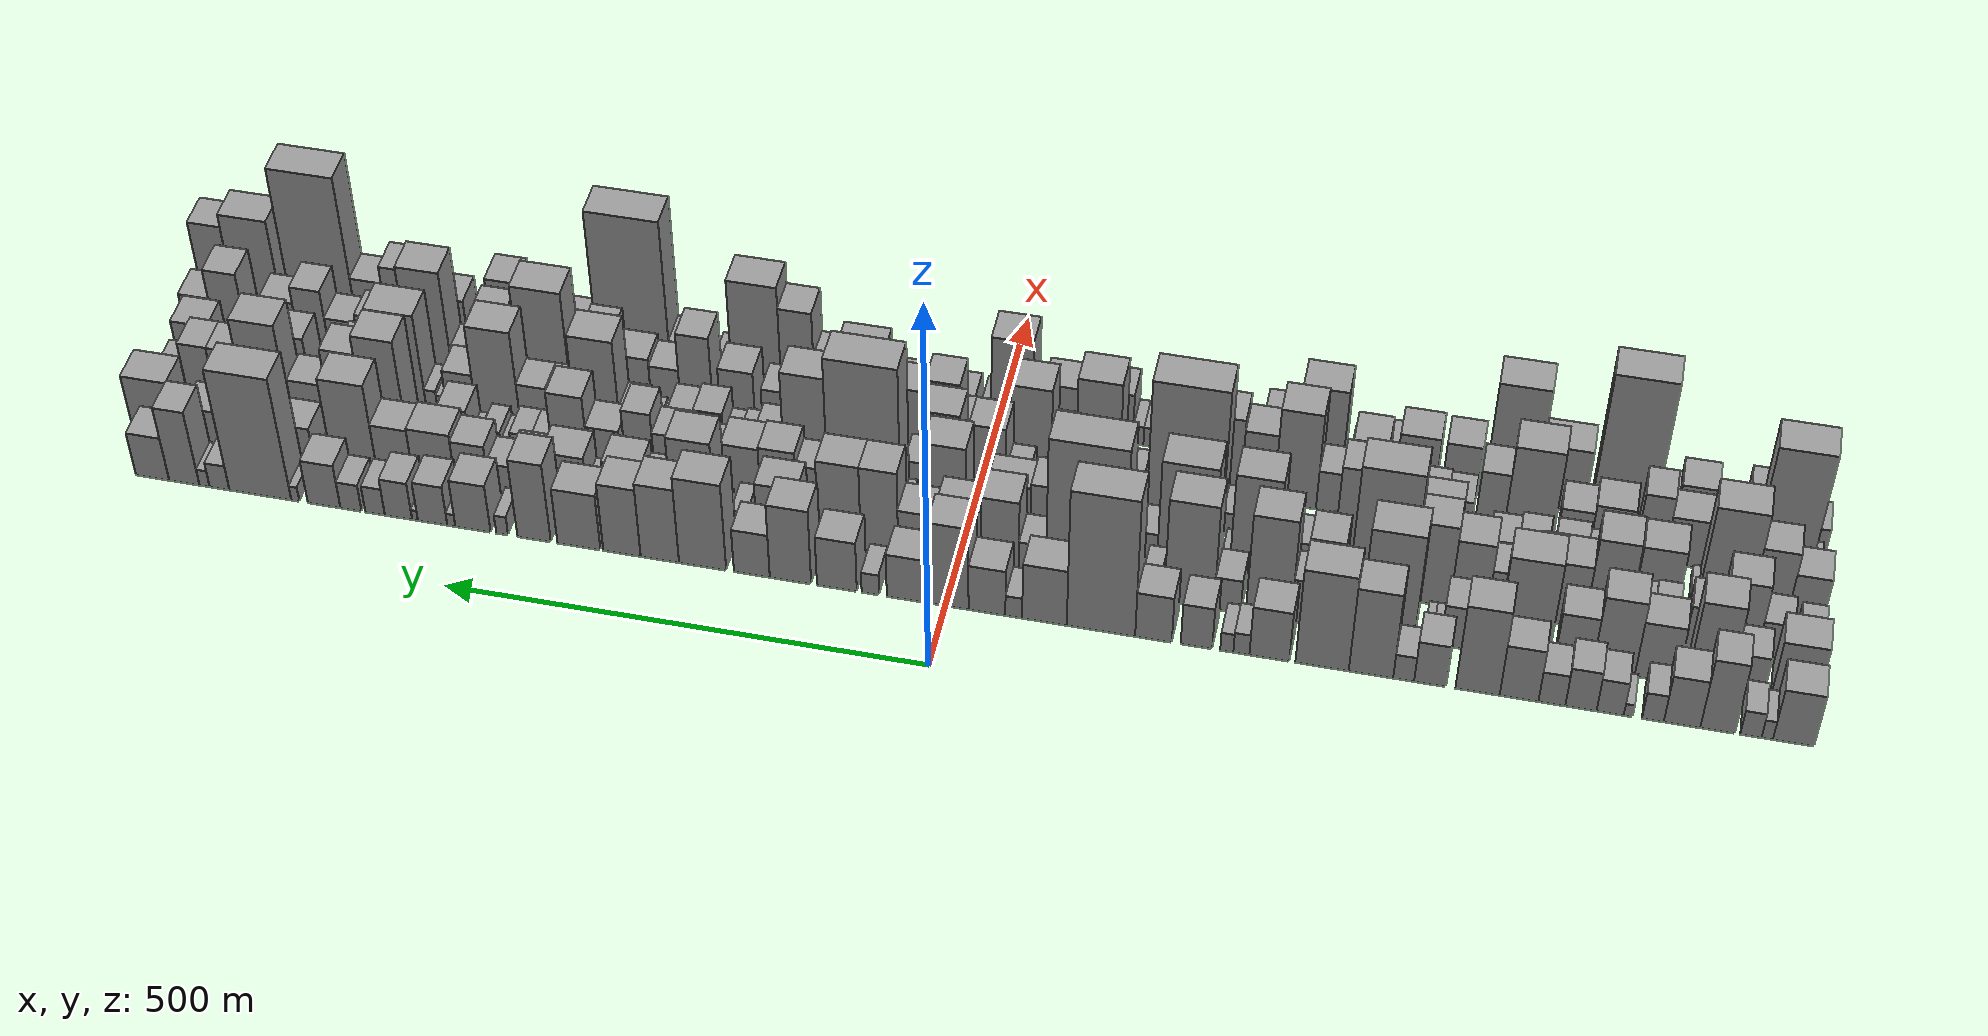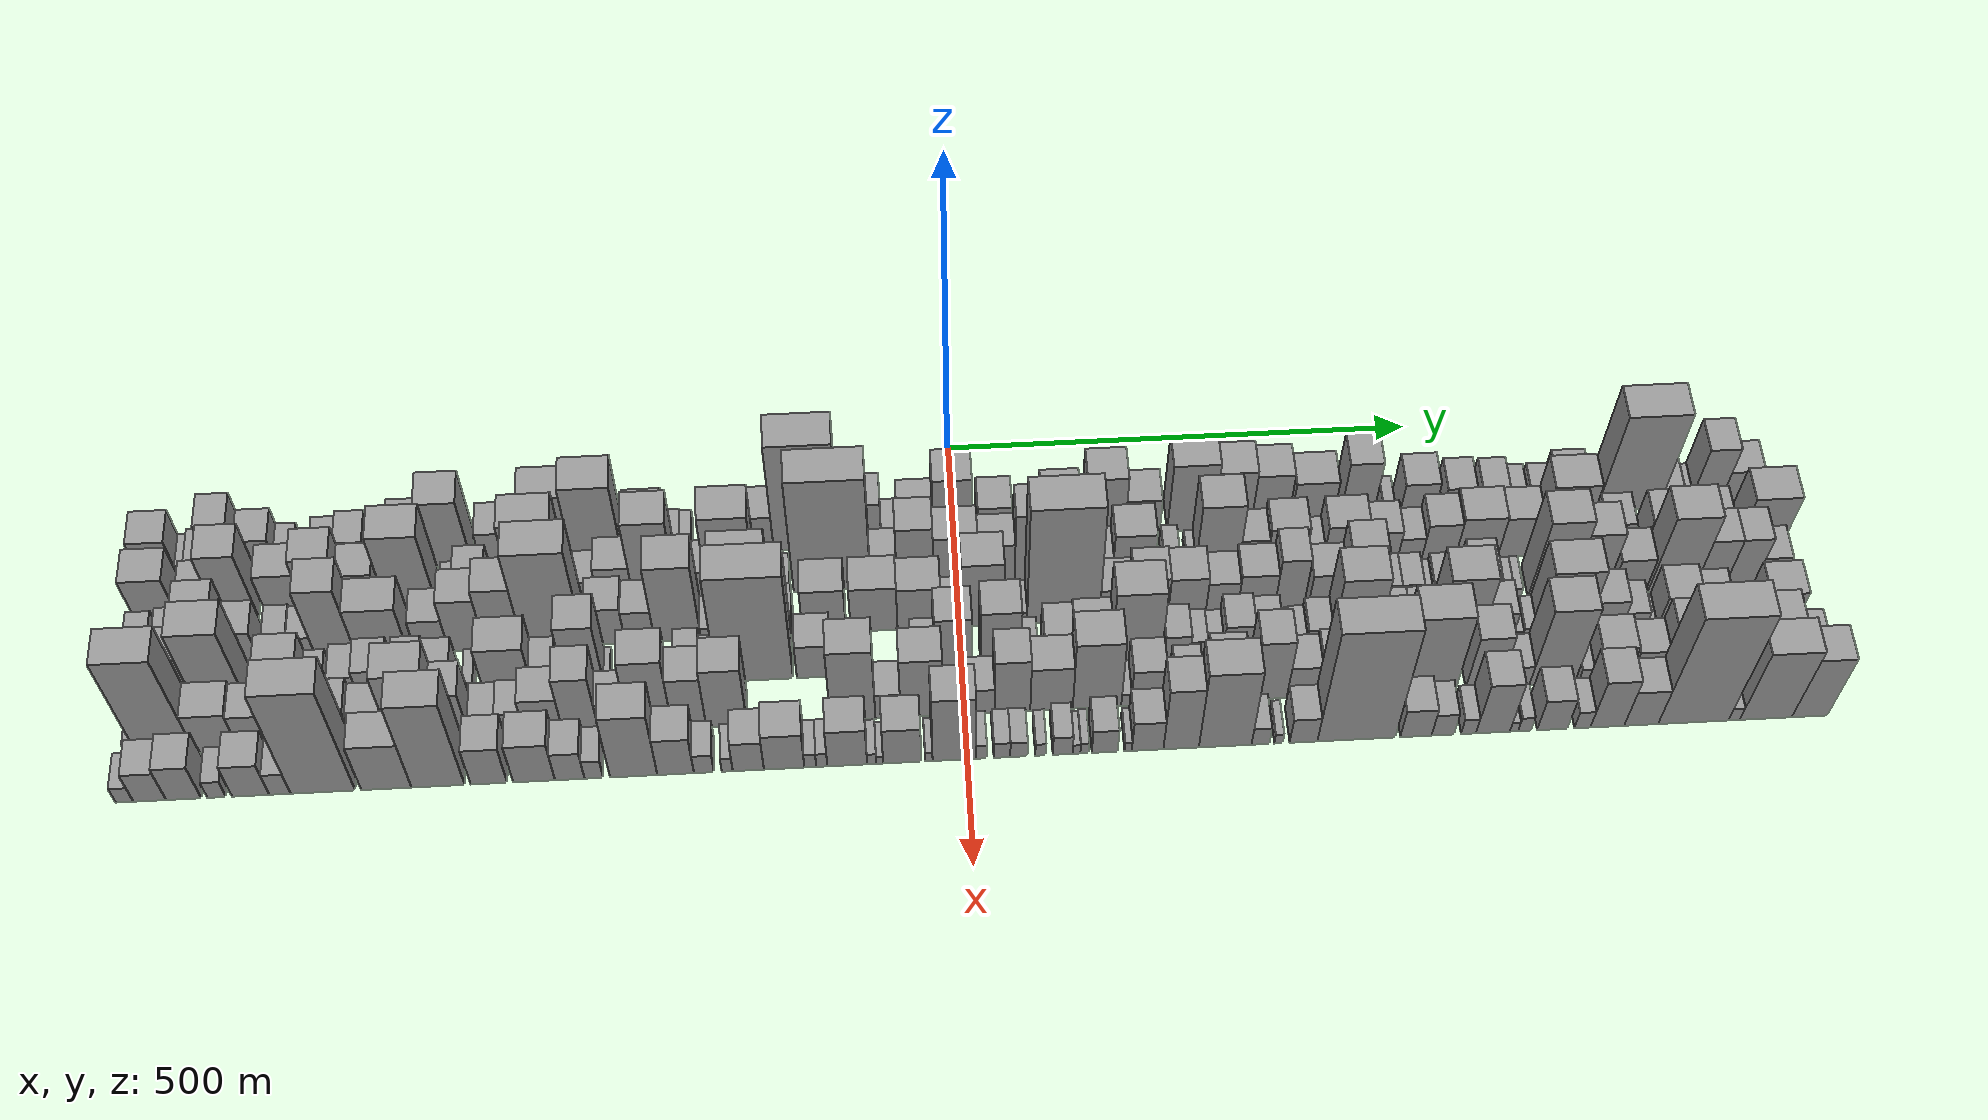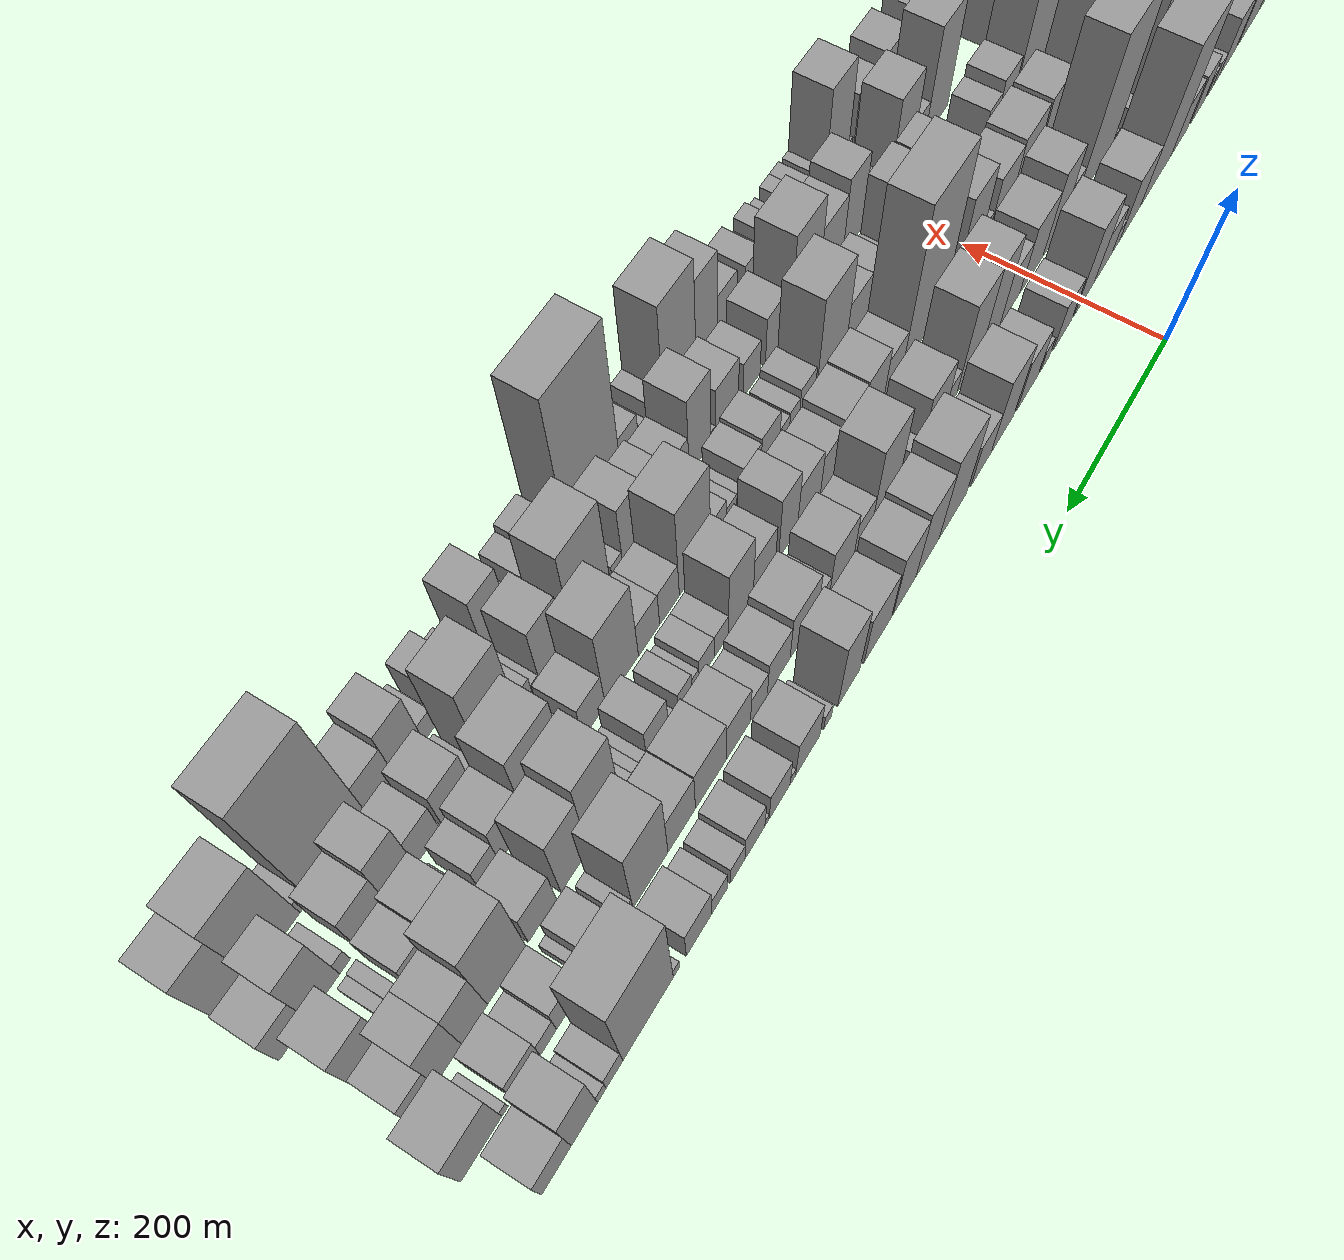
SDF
<sdf version="1.6">
 <world name="default">
  <scene>
   <sky><clouds><speed>12</speed></clouds></sky>
   <ambient>0.4 0.4 0.4 1</ambient>
   <background>0.7 0.7 0.7 1</background>
   <shadows>1</shadows>
  </scene>
  <gravity>0 0 -9.8066</gravity>
  <magnetic_field>6e-06 2.3e-05 -4.2e-05</magnetic_field>
  <physics default="0" name="default_physics" type="ode">
   <ode>
    <solver>
     <type>quick</type>
     <iters>10</iters>
     <sor>1.0</sor>
     <use_dynamic_moi_rescaling>0</use_dynamic_moi_rescaling>
    </solver>
    <constraints>
     <cfm>0</cfm>
     <erp>0.2</erp>
     <contact_max_correcting_vel>100</contact_max_correcting_vel>
     <contact_surface_layer>0.001</contact_surface_layer>
    </constraints>
   </ode>
   <max_step_size>0.004</max_step_size>
   <real_time_factor>1</real_time_factor>
   <real_time_update_rate>250</real_time_update_rate>
  </physics>
  <light name="sun" type="directional">
   <pose>0 0 10 0 0 0</pose>
   <diffuse>0.8 0.8 0.8 1</diffuse>
   <specular>0.2 0.2 0.2 1</specular>
   <attenuation>
    <range>1000</range>
    <constant>0.9</constant>
    <linear>0.01</linear>
    <quadratic>0.001</quadratic>
   </attenuation>
   <direction>-0.5 0.1 -0.9</direction>
  </light>
  <model name="building_1">
   <static>1</static>
   <pose>100.0000 -840.2048 0 0.000000 0.000000 0.000000</pose>
   <link name="link">
    <pose>0 0 37.50 0 0 0</pose>
    <collision name="collision"><geometry><box><size>40.0000 39.5904 75.0000</size></box></geometry></collision>
    <visual name="visual">
     <cast_shadows>0</cast_shadows>
     <geometry><box><size>40.0000 39.5904 75.0000</size></box></geometry>
     <material>
      <script>
       <uri>model://grey_wall/materials/scripts</uri>
       <uri>model://grey_wall/materials/textures</uri>
       <name>vrc/grey_wall</name>
      </script>
     </material>
    </visual>
   </link>
  </model>
  <model name="building_2">
   <static>1</static>
   <pose>100.0000 -814.9266 0 0.000000 0.000000 0.000000</pose>
   <link name="link">
    <pose>0 0 13.50 0 0 0</pose>
    <collision name="collision"><geometry><box><size>40.0000 10.9660 27.0000</size></box></geometry></collision>
    <visual name="visual">
     <cast_shadows>0</cast_shadows>
     <geometry><box><size>40.0000 10.9660 27.0000</size></box></geometry>
     <material>
      <script>
       <uri>model://grey_wall/materials/scripts</uri>
       <uri>model://grey_wall/materials/textures</uri>
       <name>vrc/grey_wall</name>
      </script>
     </material>
    </visual>
   </link>
  </model>
  <model name="building_3">
   <static>1</static>
   <pose>100.0000 -799.1964 0 0.000000 0.000000 0.000000</pose>
   <link name="link">
    <pose>0 0 18.00 0 0 0</pose>
    <collision name="collision"><geometry><box><size>40.0000 20.4942 36.0000</size></box></geometry></collision>
    <visual name="visual">
     <cast_shadows>0</cast_shadows>
     <geometry><box><size>40.0000 20.4942 36.0000</size></box></geometry>
     <material>
      <script>
       <uri>model://grey_wall/materials/scripts</uri>
       <uri>model://grey_wall/materials/textures</uri>
       <name>vrc/grey_wall</name>
      </script>
     </material>
    </visual>
   </link>
  </model>
  <model name="building_4">
   <static>1</static>
   <pose>100.0000 -767.1937 0 0.000000 0.000000 0.000000</pose>
   <link name="link">
    <pose>0 0 51.00 0 0 0</pose>
    <collision name="collision"><geometry><box><size>40.0000 33.5113 102.0000</size></box></geometry></collision>
    <visual name="visual">
     <cast_shadows>0</cast_shadows>
     <geometry><box><size>40.0000 33.5113 102.0000</size></box></geometry>
     <material>
      <script>
       <uri>model://grey_wall/materials/scripts</uri>
       <uri>model://grey_wall/materials/textures</uri>
       <name>vrc/grey_wall</name>
      </script>
     </material>
    </visual>
   </link>
  </model>
  <model name="building_5">
   <static>1</static>
   <pose>100.0000 -732.7986 0 0.000000 0.000000 0.000000</pose>
   <link name="link">
    <pose>0 0 34.50 0 0 0</pose>
    <collision name="collision"><geometry><box><size>40.0000 35.2789 69.0000</size></box></geometry></collision>
    <visual name="visual">
     <cast_shadows>0</cast_shadows>
     <geometry><box><size>40.0000 35.2789 69.0000</size></box></geometry>
     <material>
      <script>
       <uri>model://grey_wall/materials/scripts</uri>
       <uri>model://grey_wall/materials/textures</uri>
       <name>vrc/grey_wall</name>
      </script>
     </material>
    </visual>
   </link>
  </model>
  <model name="building_6">
   <static>1</static>
   <pose>100.0000 -704.6048 0 0.000000 0.000000 0.000000</pose>
   <link name="link">
    <pose>0 0 19.50 0 0 0</pose>
    <collision name="collision"><geometry><box><size>40.0000 21.1087 39.0000</size></box></geometry></collision>
    <visual name="visual">
     <cast_shadows>0</cast_shadows>
     <geometry><box><size>40.0000 21.1087 39.0000</size></box></geometry>
     <material>
      <script>
       <uri>model://grey_wall/materials/scripts</uri>
       <uri>model://grey_wall/materials/textures</uri>
       <name>vrc/grey_wall</name>
      </script>
     </material>
    </visual>
   </link>
  </model>
  <model name="building_7">
   <static>1</static>
   <pose>100.0000 -680.6913 0 0.000000 0.000000 0.000000</pose>
   <link name="link">
    <pose>0 0 9.00 0 0 0</pose>
    <collision name="collision"><geometry><box><size>40.0000 8.7182 18.0000</size></box></geometry></collision>
    <visual name="visual">
     <cast_shadows>0</cast_shadows>
     <geometry><box><size>40.0000 8.7182 18.0000</size></box></geometry>
     <material>
      <script>
       <uri>model://grey_wall/materials/scripts</uri>
       <uri>model://grey_wall/materials/textures</uri>
       <name>vrc/grey_wall</name>
      </script>
     </material>
    </visual>
   </link>
  </model>
  <model name="building_8">
   <static>1</static>
   <pose>100.0000 -663.1396 0 0.000000 0.000000 0.000000</pose>
   <link name="link">
    <pose>0 0 24.00 0 0 0</pose>
    <collision name="collision"><geometry><box><size>40.0000 26.3853 48.0000</size></box></geometry></collision>
    <visual name="visual">
     <cast_shadows>0</cast_shadows>
     <geometry><box><size>40.0000 26.3853 48.0000</size></box></geometry>
     <material>
      <script>
       <uri>model://grey_wall/materials/scripts</uri>
       <uri>model://grey_wall/materials/textures</uri>
       <name>vrc/grey_wall</name>
      </script>
     </material>
    </visual>
   </link>
  </model>
  <model name="building_9">
   <static>1</static>
   <pose>100.0000 -634.6680 0 0.000000 0.000000 0.000000</pose>
   <link name="link">
    <pose>0 0 28.50 0 0 0</pose>
    <collision name="collision"><geometry><box><size>40.0000 30.5580 57.0000</size></box></geometry></collision>
    <visual name="visual">
     <cast_shadows>0</cast_shadows>
     <geometry><box><size>40.0000 30.5580 57.0000</size></box></geometry>
     <material>
      <script>
       <uri>model://grey_wall/materials/scripts</uri>
       <uri>model://grey_wall/materials/textures</uri>
       <name>vrc/grey_wall</name>
      </script>
     </material>
    </visual>
   </link>
  </model>
  <model name="building_10">
   <static>1</static>
   <pose>100.0000 -606.2961 0 0.000000 0.000000 0.000000</pose>
   <link name="link">
    <pose>0 0 22.50 0 0 0</pose>
    <collision name="collision"><geometry><box><size>40.0000 26.1857 45.0000</size></box></geometry></collision>
    <visual name="visual">
     <cast_shadows>0</cast_shadows>
     <geometry><box><size>40.0000 26.1857 45.0000</size></box></geometry>
     <material>
      <script>
       <uri>model://grey_wall/materials/scripts</uri>
       <uri>model://grey_wall/materials/textures</uri>
       <name>vrc/grey_wall</name>
      </script>
     </material>
    </visual>
   </link>
  </model>
  <model name="building_11">
   <static>1</static>
   <pose>100.0000 -574.1782 0 0.000000 0.000000 0.000000</pose>
   <link name="link">
    <pose>0 0 37.50 0 0 0</pose>
    <collision name="collision"><geometry><box><size>40.0000 38.0501 75.0000</size></box></geometry></collision>
    <visual name="visual">
     <cast_shadows>0</cast_shadows>
     <geometry><box><size>40.0000 38.0501 75.0000</size></box></geometry>
     <material>
      <script>
       <uri>model://grey_wall/materials/scripts</uri>
       <uri>model://grey_wall/materials/textures</uri>
       <name>vrc/grey_wall</name>
      </script>
     </material>
    </visual>
   </link>
  </model>
  <model name="building_12">
   <static>1</static>
   <pose>100.0000 -533.4060 0 0.000000 0.000000 0.000000</pose>
   <link name="link">
    <pose>0 0 61.50 0 0 0</pose>
    <collision name="collision"><geometry><box><size>40.0000 43.4944 123.0000</size></box></geometry></collision>
    <visual name="visual">
     <cast_shadows>0</cast_shadows>
     <geometry><box><size>40.0000 43.4944 123.0000</size></box></geometry>
     <material>
      <script>
       <uri>model://grey_wall/materials/scripts</uri>
       <uri>model://grey_wall/materials/textures</uri>
       <name>vrc/grey_wall</name>
      </script>
     </material>
    </visual>
   </link>
  </model>
  <model name="building_13">
   <static>1</static>
   <pose>100.0000 -486.7748 0 0.000000 0.000000 0.000000</pose>
   <link name="link">
    <pose>0 0 30.00 0 0 0</pose>
    <collision name="collision"><geometry><box><size>40.0000 31.7679 60.0000</size></box></geometry></collision>
    <visual name="visual">
     <cast_shadows>0</cast_shadows>
     <geometry><box><size>40.0000 31.7679 60.0000</size></box></geometry>
     <material>
      <script>
       <uri>model://grey_wall/materials/scripts</uri>
       <uri>model://grey_wall/materials/textures</uri>
       <name>vrc/grey_wall</name>
      </script>
     </material>
    </visual>
   </link>
  </model>
  <model name="building_14">
   <static>1</static>
   <pose>100.0000 -460.5717 0 0.000000 0.000000 0.000000</pose>
   <link name="link">
    <pose>0 0 18.00 0 0 0</pose>
    <collision name="collision"><geometry><box><size>40.0000 20.6384 36.0000</size></box></geometry></collision>
    <visual name="visual">
     <cast_shadows>0</cast_shadows>
     <geometry><box><size>40.0000 20.6384 36.0000</size></box></geometry>
     <material>
      <script>
       <uri>model://grey_wall/materials/scripts</uri>
       <uri>model://grey_wall/materials/textures</uri>
       <name>vrc/grey_wall</name>
      </script>
     </material>
    </visual>
   </link>
  </model>
  <model name="building_15">
   <static>1</static>
   <pose>100.0000 -428.2178 0 0.000000 0.000000 0.000000</pose>
   <link name="link">
    <pose>0 0 61.50 0 0 0</pose>
    <collision name="collision"><geometry><box><size>40.0000 44.0692 123.0000</size></box></geometry></collision>
    <visual name="visual">
     <cast_shadows>0</cast_shadows>
     <geometry><box><size>40.0000 44.0692 123.0000</size></box></geometry>
     <material>
      <script>
       <uri>model://grey_wall/materials/scripts</uri>
       <uri>model://grey_wall/materials/textures</uri>
       <name>vrc/grey_wall</name>
      </script>
     </material>
    </visual>
   </link>
  </model>
  <model name="building_16">
   <static>1</static>
   <pose>100.0000 -379.6104 0 0.000000 0.000000 0.000000</pose>
   <link name="link">
    <pose>0 0 69.00 0 0 0</pose>
    <collision name="collision"><geometry><box><size>40.0000 53.1457 138.0000</size></box></geometry></collision>
    <visual name="visual">
     <cast_shadows>0</cast_shadows>
     <geometry><box><size>40.0000 53.1457 138.0000</size></box></geometry>
     <material>
      <script>
       <uri>model://grey_wall/materials/scripts</uri>
       <uri>model://grey_wall/materials/textures</uri>
       <name>vrc/grey_wall</name>
      </script>
     </material>
    </visual>
   </link>
  </model>
  <model name="building_17">
   <static>1</static>
   <pose>100.0000 -327.0697 0 0.000000 0.000000 0.000000</pose>
   <link name="link">
    <pose>0 0 36.00 0 0 0</pose>
    <collision name="collision"><geometry><box><size>40.0000 39.9357 72.0000</size></box></geometry></collision>
    <visual name="visual">
     <cast_shadows>0</cast_shadows>
     <geometry><box><size>40.0000 39.9357 72.0000</size></box></geometry>
     <material>
      <script>
       <uri>model://grey_wall/materials/scripts</uri>
       <uri>model://grey_wall/materials/textures</uri>
       <name>vrc/grey_wall</name>
      </script>
     </material>
    </visual>
   </link>
  </model>
  <model name="building_18">
   <static>1</static>
   <pose>100.0000 -299.0526 0 0.000000 0.000000 0.000000</pose>
   <link name="link">
    <pose>0 0 15.00 0 0 0</pose>
    <collision name="collision"><geometry><box><size>40.0000 16.0985 30.0000</size></box></geometry></collision>
    <visual name="visual">
     <cast_shadows>0</cast_shadows>
     <geometry><box><size>40.0000 16.0985 30.0000</size></box></geometry>
     <material>
      <script>
       <uri>model://grey_wall/materials/scripts</uri>
       <uri>model://grey_wall/materials/textures</uri>
       <name>vrc/grey_wall</name>
      </script>
     </material>
    </visual>
   </link>
  </model>
  <model name="building_19">
   <static>1</static>
   <pose>100.0000 -284.4218 0 0.000000 0.000000 0.000000</pose>
   <link name="link">
    <pose>0 0 13.50 0 0 0</pose>
    <collision name="collision"><geometry><box><size>40.0000 13.1631 27.0000</size></box></geometry></collision>
    <visual name="visual">
     <cast_shadows>0</cast_shadows>
     <geometry><box><size>40.0000 13.1631 27.0000</size></box></geometry>
     <material>
      <script>
       <uri>model://grey_wall/materials/scripts</uri>
       <uri>model://grey_wall/materials/textures</uri>
       <name>vrc/grey_wall</name>
      </script>
     </material>
    </visual>
   </link>
  </model>
  <model name="building_20">
   <static>1</static>
   <pose>100.0000 -253.9966 0 0.000000 0.000000 0.000000</pose>
   <link name="link">
    <pose>0 0 30.00 0 0 0</pose>
    <collision name="collision"><geometry><box><size>40.0000 31.6873 60.0000</size></box></geometry></collision>
    <visual name="visual">
     <cast_shadows>0</cast_shadows>
     <geometry><box><size>40.0000 31.6873 60.0000</size></box></geometry>
     <material>
      <script>
       <uri>model://grey_wall/materials/scripts</uri>
       <uri>model://grey_wall/materials/textures</uri>
       <name>vrc/grey_wall</name>
      </script>
     </material>
    </visual>
   </link>
  </model>
  <model name="building_21">
   <static>1</static>
   <pose>100.0000 -210.6499 0 0.000000 0.000000 0.000000</pose>
   <link name="link">
    <pose>0 0 33.00 0 0 0</pose>
    <collision name="collision"><geometry><box><size>40.0000 37.0063 66.0000</size></box></geometry></collision>
    <visual name="visual">
     <cast_shadows>0</cast_shadows>
     <geometry><box><size>40.0000 37.0063 66.0000</size></box></geometry>
     <material>
      <script>
       <uri>model://grey_wall/materials/scripts</uri>
       <uri>model://grey_wall/materials/textures</uri>
       <name>vrc/grey_wall</name>
      </script>
     </material>
    </visual>
   </link>
  </model>
  <model name="building_22">
   <static>1</static>
   <pose>100.0000 -157.4701 0 0.000000 0.000000 0.000000</pose>
   <link name="link">
    <pose>0 0 99.00 0 0 0</pose>
    <collision name="collision"><geometry><box><size>40.0000 69.3533 198.0000</size></box></geometry></collision>
    <visual name="visual">
     <cast_shadows>0</cast_shadows>
     <geometry><box><size>40.0000 69.3533 198.0000</size></box></geometry>
     <material>
      <script>
       <uri>model://grey_wall/materials/scripts</uri>
       <uri>model://grey_wall/materials/textures</uri>
       <name>vrc/grey_wall</name>
      </script>
     </material>
    </visual>
   </link>
  </model>
  <model name="building_23">
   <static>1</static>
   <pose>100.0000 -100.0852 0 0.000000 0.000000 0.000000</pose>
   <link name="link">
    <pose>0 0 40.50 0 0 0</pose>
    <collision name="collision"><geometry><box><size>40.0000 45.4164 81.0000</size></box></geometry></collision>
    <visual name="visual">
     <cast_shadows>0</cast_shadows>
     <geometry><box><size>40.0000 45.4164 81.0000</size></box></geometry>
     <material>
      <script>
       <uri>model://grey_wall/materials/scripts</uri>
       <uri>model://grey_wall/materials/textures</uri>
       <name>vrc/grey_wall</name>
      </script>
     </material>
    </visual>
   </link>
  </model>
  <model name="building_24">
   <static>1</static>
   <pose>100.0000 -68.7979 0 0.000000 0.000000 0.000000</pose>
   <link name="link">
    <pose>0 0 15.00 0 0 0</pose>
    <collision name="collision"><geometry><box><size>40.0000 17.1581 30.0000</size></box></geometry></collision>
    <visual name="visual">
     <cast_shadows>0</cast_shadows>
     <geometry><box><size>40.0000 17.1581 30.0000</size></box></geometry>
     <material>
      <script>
       <uri>model://grey_wall/materials/scripts</uri>
       <uri>model://grey_wall/materials/textures</uri>
       <name>vrc/grey_wall</name>
      </script>
     </material>
    </visual>
   </link>
  </model>
  <model name="building_25">
   <static>1</static>
   <pose>100.0000 -41.3671 0 0.000000 0.000000 0.000000</pose>
   <link name="link">
    <pose>0 0 33.00 0 0 0</pose>
    <collision name="collision"><geometry><box><size>40.0000 37.7035 66.0000</size></box></geometry></collision>
    <visual name="visual">
     <cast_shadows>0</cast_shadows>
     <geometry><box><size>40.0000 37.7035 66.0000</size></box></geometry>
     <material>
      <script>
       <uri>model://grey_wall/materials/scripts</uri>
       <uri>model://grey_wall/materials/textures</uri>
       <name>vrc/grey_wall</name>
      </script>
     </material>
    </visual>
   </link>
  </model>
  <model name="building_26">
   <static>1</static>
   <pose>100.0000 -1.7018 0 0.000000 0.000000 0.000000</pose>
   <link name="link">
    <pose>0 0 60.00 0 0 0</pose>
    <collision name="collision"><geometry><box><size>40.0000 41.6272 120.0000</size></box></geometry></collision>
    <visual name="visual">
     <cast_shadows>0</cast_shadows>
     <geometry><box><size>40.0000 41.6272 120.0000</size></box></geometry>
     <material>
      <script>
       <uri>model://grey_wall/materials/scripts</uri>
       <uri>model://grey_wall/materials/textures</uri>
       <name>vrc/grey_wall</name>
      </script>
     </material>
    </visual>
   </link>
  </model>
  <model name="building_27">
   <static>1</static>
   <pose>100.0000 43.3163 0 0.000000 0.000000 0.000000</pose>
   <link name="link">
    <pose>0 0 31.50 0 0 0</pose>
    <collision name="collision"><geometry><box><size>40.0000 36.4091 63.0000</size></box></geometry></collision>
    <visual name="visual">
     <cast_shadows>0</cast_shadows>
     <geometry><box><size>40.0000 36.4091 63.0000</size></box></geometry>
     <material>
      <script>
       <uri>model://grey_wall/materials/scripts</uri>
       <uri>model://grey_wall/materials/textures</uri>
       <name>vrc/grey_wall</name>
      </script>
     </material>
    </visual>
   </link>
  </model>
  <model name="building_28">
   <static>1</static>
   <pose>100.0000 78.5079 0 0.000000 0.000000 0.000000</pose>
   <link name="link">
    <pose>0 0 15.00 0 0 0</pose>
    <collision name="collision"><geometry><box><size>40.0000 17.9742 30.0000</size></box></geometry></collision>
    <visual name="visual">
     <cast_shadows>0</cast_shadows>
     <geometry><box><size>40.0000 17.9742 30.0000</size></box></geometry>
     <material>
      <script>
       <uri>model://grey_wall/materials/scripts</uri>
       <uri>model://grey_wall/materials/textures</uri>
       <name>vrc/grey_wall</name>
      </script>
     </material>
    </visual>
   </link>
  </model>
  <model name="building_29">
   <static>1</static>
   <pose>100.0000 113.1503 0 0.000000 0.000000 0.000000</pose>
   <link name="link">
    <pose>0 0 36.00 0 0 0</pose>
    <collision name="collision"><geometry><box><size>40.0000 41.3105 72.0000</size></box></geometry></collision>
    <visual name="visual">
     <cast_shadows>0</cast_shadows>
     <geometry><box><size>40.0000 41.3105 72.0000</size></box></geometry>
     <material>
      <script>
       <uri>model://grey_wall/materials/scripts</uri>
       <uri>model://grey_wall/materials/textures</uri>
       <name>vrc/grey_wall</name>
      </script>
     </material>
    </visual>
   </link>
  </model>
  <model name="building_30">
   <static>1</static>
   <pose>100.0000 161.3058 0 0.000000 0.000000 0.000000</pose>
   <link name="link">
    <pose>0 0 54.00 0 0 0</pose>
    <collision name="collision"><geometry><box><size>40.0000 43.0006 108.0000</size></box></geometry></collision>
    <visual name="visual">
     <cast_shadows>0</cast_shadows>
     <geometry><box><size>40.0000 43.0006 108.0000</size></box></geometry>
     <material>
      <script>
       <uri>model://grey_wall/materials/scripts</uri>
       <uri>model://grey_wall/materials/textures</uri>
       <name>vrc/grey_wall</name>
      </script>
     </material>
    </visual>
   </link>
  </model>
  <model name="building_31">
   <static>1</static>
   <pose>100.0000 201.5353 0 0.000000 0.000000 0.000000</pose>
   <link name="link">
    <pose>0 0 31.50 0 0 0</pose>
    <collision name="collision"><geometry><box><size>40.0000 37.4584 63.0000</size></box></geometry></collision>
    <visual name="visual">
     <cast_shadows>0</cast_shadows>
     <geometry><box><size>40.0000 37.4584 63.0000</size></box></geometry>
     <material>
      <script>
       <uri>model://grey_wall/materials/scripts</uri>
       <uri>model://grey_wall/materials/textures</uri>
       <name>vrc/grey_wall</name>
      </script>
     </material>
    </visual>
   </link>
  </model>
  <model name="building_32">
   <static>1</static>
   <pose>100.0000 253.0054 0 0.000000 0.000000 0.000000</pose>
   <link name="link">
    <pose>0 0 63.00 0 0 0</pose>
    <collision name="collision"><geometry><box><size>40.0000 49.4817 126.0000</size></box></geometry></collision>
    <visual name="visual">
     <cast_shadows>0</cast_shadows>
     <geometry><box><size>40.0000 49.4817 126.0000</size></box></geometry>
     <material>
      <script>
       <uri>model://grey_wall/materials/scripts</uri>
       <uri>model://grey_wall/materials/textures</uri>
       <name>vrc/grey_wall</name>
      </script>
     </material>
    </visual>
   </link>
  </model>
  <model name="building_33">
   <static>1</static>
   <pose>100.0000 297.9278 0 0.000000 0.000000 0.000000</pose>
   <link name="link">
    <pose>0 0 54.00 0 0 0</pose>
    <collision name="collision"><geometry><box><size>40.0000 40.3631 108.0000</size></box></geometry></collision>
    <visual name="visual">
     <cast_shadows>0</cast_shadows>
     <geometry><box><size>40.0000 40.3631 108.0000</size></box></geometry>
     <material>
      <script>
       <uri>model://grey_wall/materials/scripts</uri>
       <uri>model://grey_wall/materials/textures</uri>
       <name>vrc/grey_wall</name>
      </script>
     </material>
    </visual>
   </link>
  </model>
  <model name="building_34">
   <static>1</static>
   <pose>100.0000 337.8094 0 0.000000 0.000000 0.000000</pose>
   <link name="link">
    <pose>0 0 49.50 0 0 0</pose>
    <collision name="collision"><geometry><box><size>40.0000 39.4001 99.0000</size></box></geometry></collision>
    <visual name="visual">
     <cast_shadows>0</cast_shadows>
     <geometry><box><size>40.0000 39.4001 99.0000</size></box></geometry>
     <material>
      <script>
       <uri>model://grey_wall/materials/scripts</uri>
       <uri>model://grey_wall/materials/textures</uri>
       <name>vrc/grey_wall</name>
      </script>
     </material>
    </visual>
   </link>
  </model>
  <model name="building_35">
   <static>1</static>
   <pose>100.0000 383.2852 0 0.000000 0.000000 0.000000</pose>
   <link name="link">
    <pose>0 0 40.50 0 0 0</pose>
    <collision name="collision"><geometry><box><size>40.0000 45.5514 81.0000</size></box></geometry></collision>
    <visual name="visual">
     <cast_shadows>0</cast_shadows>
     <geometry><box><size>40.0000 45.5514 81.0000</size></box></geometry>
     <material>
      <script>
       <uri>model://grey_wall/materials/scripts</uri>
       <uri>model://grey_wall/materials/textures</uri>
       <name>vrc/grey_wall</name>
      </script>
     </material>
    </visual>
   </link>
  </model>
  <model name="building_36">
   <static>1</static>
   <pose>100.0000 430.8100 0 0.000000 0.000000 0.000000</pose>
   <link name="link">
    <pose>0 0 57.00 0 0 0</pose>
    <collision name="collision"><geometry><box><size>40.0000 35.4983 114.0000</size></box></geometry></collision>
    <visual name="visual">
     <cast_shadows>0</cast_shadows>
     <geometry><box><size>40.0000 35.4983 114.0000</size></box></geometry>
     <material>
      <script>
       <uri>model://grey_wall/materials/scripts</uri>
       <uri>model://grey_wall/materials/textures</uri>
       <name>vrc/grey_wall</name>
      </script>
     </material>
    </visual>
   </link>
  </model>
  <model name="building_37">
   <static>1</static>
   <pose>100.0000 464.8582 0 0.000000 0.000000 0.000000</pose>
   <link name="link">
    <pose>0 0 13.50 0 0 0</pose>
    <collision name="collision"><geometry><box><size>40.0000 12.5981 27.0000</size></box></geometry></collision>
    <visual name="visual">
     <cast_shadows>0</cast_shadows>
     <geometry><box><size>40.0000 12.5981 27.0000</size></box></geometry>
     <material>
      <script>
       <uri>model://grey_wall/materials/scripts</uri>
       <uri>model://grey_wall/materials/textures</uri>
       <name>vrc/grey_wall</name>
      </script>
     </material>
    </visual>
   </link>
  </model>
  <model name="building_38">
   <static>1</static>
   <pose>100.0000 495.9969 0 0.000000 0.000000 0.000000</pose>
   <link name="link">
    <pose>0 0 34.50 0 0 0</pose>
    <collision name="collision"><geometry><box><size>40.0000 37.6793 69.0000</size></box></geometry></collision>
    <visual name="visual">
     <cast_shadows>0</cast_shadows>
     <geometry><box><size>40.0000 37.6793 69.0000</size></box></geometry>
     <material>
      <script>
       <uri>model://grey_wall/materials/scripts</uri>
       <uri>model://grey_wall/materials/textures</uri>
       <name>vrc/grey_wall</name>
      </script>
     </material>
    </visual>
   </link>
  </model>
  <model name="building_39">
   <static>1</static>
   <pose>100.0000 519.1426 0 0.000000 0.000000 0.000000</pose>
   <link name="link">
    <pose>0 0 9.00 0 0 0</pose>
    <collision name="collision"><geometry><box><size>40.0000 8.6120 18.0000</size></box></geometry></collision>
    <visual name="visual">
     <cast_shadows>0</cast_shadows>
     <geometry><box><size>40.0000 8.6120 18.0000</size></box></geometry>
     <material>
      <script>
       <uri>model://grey_wall/materials/scripts</uri>
       <uri>model://grey_wall/materials/textures</uri>
       <name>vrc/grey_wall</name>
      </script>
     </material>
    </visual>
   </link>
  </model>
  <model name="building_40">
   <static>1</static>
   <pose>100.0000 539.2763 0 0.000000 0.000000 0.000000</pose>
   <link name="link">
    <pose>0 0 28.50 0 0 0</pose>
    <collision name="collision"><geometry><box><size>40.0000 31.6553 57.0000</size></box></geometry></collision>
    <visual name="visual">
     <cast_shadows>0</cast_shadows>
     <geometry><box><size>40.0000 31.6553 57.0000</size></box></geometry>
     <material>
      <script>
       <uri>model://grey_wall/materials/scripts</uri>
       <uri>model://grey_wall/materials/textures</uri>
       <name>vrc/grey_wall</name>
      </script>
     </material>
    </visual>
   </link>
  </model>
  <model name="building_41">
   <static>1</static>
   <pose>100.0000 558.1478 0 0.000000 0.000000 0.000000</pose>
   <link name="link">
    <pose>0 0 7.50 0 0 0</pose>
    <collision name="collision"><geometry><box><size>40.0000 6.0878 15.0000</size></box></geometry></collision>
    <visual name="visual">
     <cast_shadows>0</cast_shadows>
     <geometry><box><size>40.0000 6.0878 15.0000</size></box></geometry>
     <material>
      <script>
       <uri>model://grey_wall/materials/scripts</uri>
       <uri>model://grey_wall/materials/textures</uri>
       <name>vrc/grey_wall</name>
      </script>
     </material>
    </visual>
   </link>
  </model>
  <model name="building_42">
   <static>1</static>
   <pose>100.0000 575.8657 0 0.000000 0.000000 0.000000</pose>
   <link name="link">
    <pose>0 0 27.00 0 0 0</pose>
    <collision name="collision"><geometry><box><size>40.0000 29.3480 54.0000</size></box></geometry></collision>
    <visual name="visual">
     <cast_shadows>0</cast_shadows>
     <geometry><box><size>40.0000 29.3480 54.0000</size></box></geometry>
     <material>
      <script>
       <uri>model://grey_wall/materials/scripts</uri>
       <uri>model://grey_wall/materials/textures</uri>
       <name>vrc/grey_wall</name>
      </script>
     </material>
    </visual>
   </link>
  </model>
  <model name="building_43">
   <static>1</static>
   <pose>100.0000 601.0527 0 0.000000 0.000000 0.000000</pose>
   <link name="link">
    <pose>0 0 19.50 0 0 0</pose>
    <collision name="collision"><geometry><box><size>40.0000 21.0259 39.0000</size></box></geometry></collision>
    <visual name="visual">
     <cast_shadows>0</cast_shadows>
     <geometry><box><size>40.0000 21.0259 39.0000</size></box></geometry>
     <material>
      <script>
       <uri>model://grey_wall/materials/scripts</uri>
       <uri>model://grey_wall/materials/textures</uri>
       <name>vrc/grey_wall</name>
      </script>
     </material>
    </visual>
   </link>
  </model>
  <model name="building_44">
   <static>1</static>
   <pose>100.0000 627.0009 0 0.000000 0.000000 0.000000</pose>
   <link name="link">
    <pose>0 0 19.50 0 0 0</pose>
    <collision name="collision"><geometry><box><size>40.0000 22.8707 39.0000</size></box></geometry></collision>
    <visual name="visual">
     <cast_shadows>0</cast_shadows>
     <geometry><box><size>40.0000 22.8707 39.0000</size></box></geometry>
     <material>
      <script>
       <uri>model://grey_wall/materials/scripts</uri>
       <uri>model://grey_wall/materials/textures</uri>
       <name>vrc/grey_wall</name>
      </script>
     </material>
    </visual>
   </link>
  </model>
  <model name="building_45">
   <static>1</static>
   <pose>100.0000 656.1416 0 0.000000 0.000000 0.000000</pose>
   <link name="link">
    <pose>0 0 31.50 0 0 0</pose>
    <collision name="collision"><geometry><box><size>40.0000 35.4108 63.0000</size></box></geometry></collision>
    <visual name="visual">
     <cast_shadows>0</cast_shadows>
     <geometry><box><size>40.0000 35.4108 63.0000</size></box></geometry>
     <material>
      <script>
       <uri>model://grey_wall/materials/scripts</uri>
       <uri>model://grey_wall/materials/textures</uri>
       <name>vrc/grey_wall</name>
      </script>
     </material>
    </visual>
   </link>
  </model>
  <model name="building_46">
   <static>1</static>
   <pose>100.0000 687.2384 0 0.000000 0.000000 0.000000</pose>
   <link name="link">
    <pose>0 0 10.50 0 0 0</pose>
    <collision name="collision"><geometry><box><size>40.0000 8.7828 21.0000</size></box></geometry></collision>
    <visual name="visual">
     <cast_shadows>0</cast_shadows>
     <geometry><box><size>40.0000 8.7828 21.0000</size></box></geometry>
     <material>
      <script>
       <uri>model://grey_wall/materials/scripts</uri>
       <uri>model://grey_wall/materials/textures</uri>
       <name>vrc/grey_wall</name>
      </script>
     </material>
    </visual>
   </link>
  </model>
  <model name="building_47">
   <static>1</static>
   <pose>100.0000 725.3479 0 0.000000 0.000000 0.000000</pose>
   <link name="link">
    <pose>0 0 88.50 0 0 0</pose>
    <collision name="collision"><geometry><box><size>40.0000 67.4363 177.0000</size></box></geometry></collision>
    <visual name="visual">
     <cast_shadows>0</cast_shadows>
     <geometry><box><size>40.0000 67.4363 177.0000</size></box></geometry>
     <material>
      <script>
       <uri>model://grey_wall/materials/scripts</uri>
       <uri>model://grey_wall/materials/textures</uri>
       <name>vrc/grey_wall</name>
      </script>
     </material>
    </visual>
   </link>
  </model>
  <model name="building_48">
   <static>1</static>
   <pose>100.0000 769.8377 0 0.000000 0.000000 0.000000</pose>
   <link name="link">
    <pose>0 0 18.00 0 0 0</pose>
    <collision name="collision"><geometry><box><size>40.0000 21.5433 36.0000</size></box></geometry></collision>
    <visual name="visual">
     <cast_shadows>0</cast_shadows>
     <geometry><box><size>40.0000 21.5433 36.0000</size></box></geometry>
     <material>
      <script>
       <uri>model://grey_wall/materials/scripts</uri>
       <uri>model://grey_wall/materials/textures</uri>
       <name>vrc/grey_wall</name>
      </script>
     </material>
    </visual>
   </link>
  </model>
  <model name="building_49">
   <static>1</static>
   <pose>100.0000 786.1714 0 0.000000 0.000000 0.000000</pose>
   <link name="link">
    <pose>0 0 12.00 0 0 0</pose>
    <collision name="collision"><geometry><box><size>40.0000 11.1240 24.0000</size></box></geometry></collision>
    <visual name="visual">
     <cast_shadows>0</cast_shadows>
     <geometry><box><size>40.0000 11.1240 24.0000</size></box></geometry>
     <material>
      <script>
       <uri>model://grey_wall/materials/scripts</uri>
       <uri>model://grey_wall/materials/textures</uri>
       <name>vrc/grey_wall</name>
      </script>
     </material>
    </visual>
   </link>
  </model>
  <model name="building_50">
   <static>1</static>
   <pose>100.0000 808.2883 0 0.000000 0.000000 0.000000</pose>
   <link name="link">
    <pose>0 0 54.00 0 0 0</pose>
    <collision name="collision"><geometry><box><size>40.0000 33.1097 108.0000</size></box></geometry></collision>
    <visual name="visual">
     <cast_shadows>0</cast_shadows>
     <geometry><box><size>40.0000 33.1097 108.0000</size></box></geometry>
     <material>
      <script>
       <uri>model://grey_wall/materials/scripts</uri>
       <uri>model://grey_wall/materials/textures</uri>
       <name>vrc/grey_wall</name>
      </script>
     </material>
    </visual>
   </link>
  </model>
  <model name="building_51">
   <static>1</static>
   <pose>100.0000 843.0996 0 0.000000 0.000000 0.000000</pose>
   <link name="link">
    <pose>0 0 31.50 0 0 0</pose>
    <collision name="collision"><geometry><box><size>40.0000 36.5130 63.0000</size></box></geometry></collision>
    <visual name="visual">
     <cast_shadows>0</cast_shadows>
     <geometry><box><size>40.0000 36.5130 63.0000</size></box></geometry>
     <material>
      <script>
       <uri>model://grey_wall/materials/scripts</uri>
       <uri>model://grey_wall/materials/textures</uri>
       <name>vrc/grey_wall</name>
      </script>
     </material>
    </visual>
   </link>
  </model>
  <model name="building_52">
   <static>1</static>
   <pose>152.0000 -837.6055 0 0.000000 0.000000 0.000000</pose>
   <link name="link">
    <pose>0 0 42.00 0 0 0</pose>
    <collision name="collision"><geometry><box><size>40.0000 44.7890 84.0000</size></box></geometry></collision>
    <visual name="visual">
     <cast_shadows>0</cast_shadows>
     <geometry><box><size>40.0000 44.7890 84.0000</size></box></geometry>
     <material>
      <script>
       <uri>model://grey_wall/materials/scripts</uri>
       <uri>model://grey_wall/materials/textures</uri>
       <name>vrc/grey_wall</name>
      </script>
     </material>
    </visual>
   </link>
  </model>
  <model name="building_53">
   <static>1</static>
   <pose>152.0000 -793.0308 0 0.000000 0.000000 0.000000</pose>
   <link name="link">
    <pose>0 0 28.50 0 0 0</pose>
    <collision name="collision"><geometry><box><size>40.0000 30.3604 57.0000</size></box></geometry></collision>
    <visual name="visual">
     <cast_shadows>0</cast_shadows>
     <geometry><box><size>40.0000 30.3604 57.0000</size></box></geometry>
     <material>
      <script>
       <uri>model://grey_wall/materials/scripts</uri>
       <uri>model://grey_wall/materials/textures</uri>
       <name>vrc/grey_wall</name>
      </script>
     </material>
    </visual>
   </link>
  </model>
  <model name="building_54">
   <static>1</static>
   <pose>152.0000 -753.9375 0 0.000000 0.000000 0.000000</pose>
   <link name="link">
    <pose>0 0 61.50 0 0 0</pose>
    <collision name="collision"><geometry><box><size>40.0000 41.8262 123.0000</size></box></geometry></collision>
    <visual name="visual">
     <cast_shadows>0</cast_shadows>
     <geometry><box><size>40.0000 41.8262 123.0000</size></box></geometry>
     <material>
      <script>
       <uri>model://grey_wall/materials/scripts</uri>
       <uri>model://grey_wall/materials/textures</uri>
       <name>vrc/grey_wall</name>
      </script>
     </material>
    </visual>
   </link>
  </model>
  <model name="building_55">
   <static>1</static>
   <pose>152.0000 -703.2747 0 0.000000 0.000000 0.000000</pose>
   <link name="link">
    <pose>0 0 40.50 0 0 0</pose>
    <collision name="collision"><geometry><box><size>40.0000 41.4992 81.0000</size></box></geometry></collision>
    <visual name="visual">
     <cast_shadows>0</cast_shadows>
     <geometry><box><size>40.0000 41.4992 81.0000</size></box></geometry>
     <material>
      <script>
       <uri>model://grey_wall/materials/scripts</uri>
       <uri>model://grey_wall/materials/textures</uri>
       <name>vrc/grey_wall</name>
      </script>
     </material>
    </visual>
   </link>
  </model>
  <model name="building_56">
   <static>1</static>
   <pose>152.0000 -661.7789 0 0.000000 0.000000 0.000000</pose>
   <link name="link">
    <pose>0 0 54.00 0 0 0</pose>
    <collision name="collision"><geometry><box><size>40.0000 41.4925 108.0000</size></box></geometry></collision>
    <visual name="visual">
     <cast_shadows>0</cast_shadows>
     <geometry><box><size>40.0000 41.4925 108.0000</size></box></geometry>
     <material>
      <script>
       <uri>model://grey_wall/materials/scripts</uri>
       <uri>model://grey_wall/materials/textures</uri>
       <name>vrc/grey_wall</name>
      </script>
     </material>
    </visual>
   </link>
  </model>
  <model name="building_57">
   <static>1</static>
   <pose>152.0000 -622.2637 0 0.000000 0.000000 0.000000</pose>
   <link name="link">
    <pose>0 0 37.50 0 0 0</pose>
    <collision name="collision"><geometry><box><size>40.0000 37.5379 75.0000</size></box></geometry></collision>
    <visual name="visual">
     <cast_shadows>0</cast_shadows>
     <geometry><box><size>40.0000 37.5379 75.0000</size></box></geometry>
     <material>
      <script>
       <uri>model://grey_wall/materials/scripts</uri>
       <uri>model://grey_wall/materials/textures</uri>
       <name>vrc/grey_wall</name>
      </script>
     </material>
    </visual>
   </link>
  </model>
  <model name="building_58">
   <static>1</static>
   <pose>152.0000 -571.5455 0 0.000000 0.000000 0.000000</pose>
   <link name="link">
    <pose>0 0 72.00 0 0 0</pose>
    <collision name="collision"><geometry><box><size>40.0000 51.8986 144.0000</size></box></geometry></collision>
    <visual name="visual">
     <cast_shadows>0</cast_shadows>
     <geometry><box><size>40.0000 51.8986 144.0000</size></box></geometry>
     <material>
      <script>
       <uri>model://grey_wall/materials/scripts</uri>
       <uri>model://grey_wall/materials/textures</uri>
       <name>vrc/grey_wall</name>
      </script>
     </material>
    </visual>
   </link>
  </model>
  <model name="building_59">
   <static>1</static>
   <pose>152.0000 -532.0537 0 0.000000 0.000000 0.000000</pose>
   <link name="link">
    <pose>0 0 15.00 0 0 0</pose>
    <collision name="collision"><geometry><box><size>40.0000 17.0849 30.0000</size></box></geometry></collision>
    <visual name="visual">
     <cast_shadows>0</cast_shadows>
     <geometry><box><size>40.0000 17.0849 30.0000</size></box></geometry>
     <material>
      <script>
       <uri>model://grey_wall/materials/scripts</uri>
       <uri>model://grey_wall/materials/textures</uri>
       <name>vrc/grey_wall</name>
      </script>
     </material>
    </visual>
   </link>
  </model>
  <model name="building_60">
   <static>1</static>
   <pose>152.0000 -507.1141 0 0.000000 0.000000 0.000000</pose>
   <link name="link">
    <pose>0 0 30.00 0 0 0</pose>
    <collision name="collision"><geometry><box><size>40.0000 32.7944 60.0000</size></box></geometry></collision>
    <visual name="visual">
     <cast_shadows>0</cast_shadows>
     <geometry><box><size>40.0000 32.7944 60.0000</size></box></geometry>
     <material>
      <script>
       <uri>model://grey_wall/materials/scripts</uri>
       <uri>model://grey_wall/materials/textures</uri>
       <name>vrc/grey_wall</name>
      </script>
     </material>
    </visual>
   </link>
  </model>
  <model name="building_61">
   <static>1</static>
   <pose>152.0000 -486.3163 0 0.000000 0.000000 0.000000</pose>
   <link name="link">
    <pose>0 0 9.00 0 0 0</pose>
    <collision name="collision"><geometry><box><size>40.0000 8.8012 18.0000</size></box></geometry></collision>
    <visual name="visual">
     <cast_shadows>0</cast_shadows>
     <geometry><box><size>40.0000 8.8012 18.0000</size></box></geometry>
     <material>
      <script>
       <uri>model://grey_wall/materials/scripts</uri>
       <uri>model://grey_wall/materials/textures</uri>
       <name>vrc/grey_wall</name>
      </script>
     </material>
    </visual>
   </link>
  </model>
  <model name="building_62">
   <static>1</static>
   <pose>152.0000 -477.7149 0 0.000000 0.000000 0.000000</pose>
   <link name="link">
    <pose>0 0 9.00 0 0 0</pose>
    <collision name="collision"><geometry><box><size>40.0000 8.4016 18.0000</size></box></geometry></collision>
    <visual name="visual">
     <cast_shadows>0</cast_shadows>
     <geometry><box><size>40.0000 8.4016 18.0000</size></box></geometry>
     <material>
      <script>
       <uri>model://grey_wall/materials/scripts</uri>
       <uri>model://grey_wall/materials/textures</uri>
       <name>vrc/grey_wall</name>
      </script>
     </material>
    </visual>
   </link>
  </model>
  <model name="building_63">
   <static>1</static>
   <pose>152.0000 -437.3317 0 0.000000 0.000000 0.000000</pose>
   <link name="link">
    <pose>0 0 76.50 0 0 0</pose>
    <collision name="collision"><geometry><box><size>40.0000 54.3647 153.0000</size></box></geometry></collision>
    <visual name="visual">
     <cast_shadows>0</cast_shadows>
     <geometry><box><size>40.0000 54.3647 153.0000</size></box></geometry>
     <material>
      <script>
       <uri>model://grey_wall/materials/scripts</uri>
       <uri>model://grey_wall/materials/textures</uri>
       <name>vrc/grey_wall</name>
      </script>
     </material>
    </visual>
   </link>
  </model>
  <model name="building_64">
   <static>1</static>
   <pose>152.0000 -389.5674 0 0.000000 0.000000 0.000000</pose>
   <link name="link">
    <pose>0 0 19.50 0 0 0</pose>
    <collision name="collision"><geometry><box><size>40.0000 23.1638 39.0000</size></box></geometry></collision>
    <visual name="visual">
     <cast_shadows>0</cast_shadows>
     <geometry><box><size>40.0000 23.1638 39.0000</size></box></geometry>
     <material>
      <script>
       <uri>model://grey_wall/materials/scripts</uri>
       <uri>model://grey_wall/materials/textures</uri>
       <name>vrc/grey_wall</name>
      </script>
     </material>
    </visual>
   </link>
  </model>
  <model name="building_65">
   <static>1</static>
   <pose>152.0000 -359.3392 0 0.000000 0.000000 0.000000</pose>
   <link name="link">
    <pose>0 0 31.50 0 0 0</pose>
    <collision name="collision"><geometry><box><size>40.0000 37.2927 63.0000</size></box></geometry></collision>
    <visual name="visual">
     <cast_shadows>0</cast_shadows>
     <geometry><box><size>40.0000 37.2927 63.0000</size></box></geometry>
     <material>
      <script>
       <uri>model://grey_wall/materials/scripts</uri>
       <uri>model://grey_wall/materials/textures</uri>
       <name>vrc/grey_wall</name>
      </script>
     </material>
    </visual>
   </link>
  </model>
  <model name="building_66">
   <static>1</static>
   <pose>152.0000 -317.8724 0 0.000000 0.000000 0.000000</pose>
   <link name="link">
    <pose>0 0 73.50 0 0 0</pose>
    <collision name="collision"><geometry><box><size>40.0000 45.6409 147.0000</size></box></geometry></collision>
    <visual name="visual">
     <cast_shadows>0</cast_shadows>
     <geometry><box><size>40.0000 45.6409 147.0000</size></box></geometry>
     <material>
      <script>
       <uri>model://grey_wall/materials/scripts</uri>
       <uri>model://grey_wall/materials/textures</uri>
       <name>vrc/grey_wall</name>
      </script>
     </material>
    </visual>
   </link>
  </model>
  <model name="building_67">
   <static>1</static>
   <pose>152.0000 -276.4728 0 0.000000 0.000000 0.000000</pose>
   <link name="link">
    <pose>0 0 24.00 0 0 0</pose>
    <collision name="collision"><geometry><box><size>40.0000 27.1582 48.0000</size></box></geometry></collision>
    <visual name="visual">
     <cast_shadows>0</cast_shadows>
     <geometry><box><size>40.0000 27.1582 48.0000</size></box></geometry>
     <material>
      <script>
       <uri>model://grey_wall/materials/scripts</uri>
       <uri>model://grey_wall/materials/textures</uri>
       <name>vrc/grey_wall</name>
      </script>
     </material>
    </visual>
   </link>
  </model>
  <model name="building_68">
   <static>1</static>
   <pose>152.0000 -237.4848 0 0.000000 0.000000 0.000000</pose>
   <link name="link">
    <pose>0 0 75.00 0 0 0</pose>
    <collision name="collision"><geometry><box><size>40.0000 50.8178 150.0000</size></box></geometry></collision>
    <visual name="visual">
     <cast_shadows>0</cast_shadows>
     <geometry><box><size>40.0000 50.8178 150.0000</size></box></geometry>
     <material>
      <script>
       <uri>model://grey_wall/materials/scripts</uri>
       <uri>model://grey_wall/materials/textures</uri>
       <name>vrc/grey_wall</name>
      </script>
     </material>
    </visual>
   </link>
  </model>
  <model name="building_69">
   <static>1</static>
   <pose>152.0000 -198.8668 0 0.000000 0.000000 0.000000</pose>
   <link name="link">
    <pose>0 0 18.00 0 0 0</pose>
    <collision name="collision"><geometry><box><size>40.0000 18.4183 36.0000</size></box></geometry></collision>
    <visual name="visual">
     <cast_shadows>0</cast_shadows>
     <geometry><box><size>40.0000 18.4183 36.0000</size></box></geometry>
     <material>
      <script>
       <uri>model://grey_wall/materials/scripts</uri>
       <uri>model://grey_wall/materials/textures</uri>
       <name>vrc/grey_wall</name>
      </script>
     </material>
    </visual>
   </link>
  </model>
  <model name="building_70">
   <static>1</static>
   <pose>152.0000 -179.9466 0 0.000000 0.000000 0.000000</pose>
   <link name="link">
    <pose>0 0 7.50 0 0 0</pose>
    <collision name="collision"><geometry><box><size>40.0000 7.4220 15.0000</size></box></geometry></collision>
    <visual name="visual">
     <cast_shadows>0</cast_shadows>
     <geometry><box><size>40.0000 7.4220 15.0000</size></box></geometry>
     <material>
      <script>
       <uri>model://grey_wall/materials/scripts</uri>
       <uri>model://grey_wall/materials/textures</uri>
       <name>vrc/grey_wall</name>
      </script>
     </material>
    </visual>
   </link>
  </model>
  <model name="building_71">
   <static>1</static>
   <pose>152.0000 -131.5584 0 0.000000 0.000000 0.000000</pose>
   <link name="link">
    <pose>0 0 105.00 0 0 0</pose>
    <collision name="collision"><geometry><box><size>40.0000 81.3544 210.0000</size></box></geometry></collision>
    <visual name="visual">
     <cast_shadows>0</cast_shadows>
     <geometry><box><size>40.0000 81.3544 210.0000</size></box></geometry>
     <material>
      <script>
       <uri>model://grey_wall/materials/scripts</uri>
       <uri>model://grey_wall/materials/textures</uri>
       <name>vrc/grey_wall</name>
      </script>
     </material>
    </visual>
   </link>
  </model>
  <model name="building_72">
   <static>1</static>
   <pose>152.0000 -77.0069 0 0.000000 0.000000 0.000000</pose>
   <link name="link">
    <pose>0 0 27.00 0 0 0</pose>
    <collision name="collision"><geometry><box><size>40.0000 27.7486 54.0000</size></box></geometry></collision>
    <visual name="visual">
     <cast_shadows>0</cast_shadows>
     <geometry><box><size>40.0000 27.7486 54.0000</size></box></geometry>
     <material>
      <script>
       <uri>model://grey_wall/materials/scripts</uri>
       <uri>model://grey_wall/materials/textures</uri>
       <name>vrc/grey_wall</name>
      </script>
     </material>
    </visual>
   </link>
  </model>
  <model name="building_73">
   <static>1</static>
   <pose>152.0000 -43.8006 0 0.000000 0.000000 0.000000</pose>
   <link name="link">
    <pose>0 0 55.50 0 0 0</pose>
    <collision name="collision"><geometry><box><size>40.0000 38.6639 111.0000</size></box></geometry></collision>
    <visual name="visual">
     <cast_shadows>0</cast_shadows>
     <geometry><box><size>40.0000 38.6639 111.0000</size></box></geometry>
     <material>
      <script>
       <uri>model://grey_wall/materials/scripts</uri>
       <uri>model://grey_wall/materials/textures</uri>
       <name>vrc/grey_wall</name>
      </script>
     </material>
    </visual>
   </link>
  </model>
  <model name="building_74">
   <static>1</static>
   <pose>152.0000 -1.1710 0 0.000000 0.000000 0.000000</pose>
   <link name="link">
    <pose>0 0 45.00 0 0 0</pose>
    <collision name="collision"><geometry><box><size>40.0000 46.5953 90.0000</size></box></geometry></collision>
    <visual name="visual">
     <cast_shadows>0</cast_shadows>
     <geometry><box><size>40.0000 46.5953 90.0000</size></box></geometry>
     <material>
      <script>
       <uri>model://grey_wall/materials/scripts</uri>
       <uri>model://grey_wall/materials/textures</uri>
       <name>vrc/grey_wall</name>
      </script>
     </material>
    </visual>
   </link>
  </model>
  <model name="building_75">
   <static>1</static>
   <pose>152.0000 41.7712 0 0.000000 0.000000 0.000000</pose>
   <link name="link">
    <pose>0 0 36.00 0 0 0</pose>
    <collision name="collision"><geometry><box><size>40.0000 39.2890 72.0000</size></box></geometry></collision>
    <visual name="visual">
     <cast_shadows>0</cast_shadows>
     <geometry><box><size>40.0000 39.2890 72.0000</size></box></geometry>
     <material>
      <script>
       <uri>model://grey_wall/materials/scripts</uri>
       <uri>model://grey_wall/materials/textures</uri>
       <name>vrc/grey_wall</name>
      </script>
     </material>
    </visual>
   </link>
  </model>
  <model name="building_76">
   <static>1</static>
   <pose>152.0000 80.8757 0 0.000000 0.000000 0.000000</pose>
   <link name="link">
    <pose>0 0 63.00 0 0 0</pose>
    <collision name="collision"><geometry><box><size>40.0000 38.9200 126.0000</size></box></geometry></collision>
    <visual name="visual">
     <cast_shadows>0</cast_shadows>
     <geometry><box><size>40.0000 38.9200 126.0000</size></box></geometry>
     <material>
      <script>
       <uri>model://grey_wall/materials/scripts</uri>
       <uri>model://grey_wall/materials/textures</uri>
       <name>vrc/grey_wall</name>
      </script>
     </material>
    </visual>
   </link>
  </model>
  <model name="building_77">
   <static>1</static>
   <pose>152.0000 122.4114 0 0.000000 0.000000 0.000000</pose>
   <link name="link">
    <pose>0 0 63.00 0 0 0</pose>
    <collision name="collision"><geometry><box><size>40.0000 44.1514 126.0000</size></box></geometry></collision>
    <visual name="visual">
     <cast_shadows>0</cast_shadows>
     <geometry><box><size>40.0000 44.1514 126.0000</size></box></geometry>
     <material>
      <script>
       <uri>model://grey_wall/materials/scripts</uri>
       <uri>model://grey_wall/materials/textures</uri>
       <name>vrc/grey_wall</name>
      </script>
     </material>
    </visual>
   </link>
  </model>
  <model name="building_78">
   <static>1</static>
   <pose>152.0000 154.9196 0 0.000000 0.000000 0.000000</pose>
   <link name="link">
    <pose>0 0 18.00 0 0 0</pose>
    <collision name="collision"><geometry><box><size>40.0000 20.8650 36.0000</size></box></geometry></collision>
    <visual name="visual">
     <cast_shadows>0</cast_shadows>
     <geometry><box><size>40.0000 20.8650 36.0000</size></box></geometry>
     <material>
      <script>
       <uri>model://grey_wall/materials/scripts</uri>
       <uri>model://grey_wall/materials/textures</uri>
       <name>vrc/grey_wall</name>
      </script>
     </material>
    </visual>
   </link>
  </model>
  <model name="building_79">
   <static>1</static>
   <pose>152.0000 187.4559 0 0.000000 0.000000 0.000000</pose>
   <link name="link">
    <pose>0 0 39.00 0 0 0</pose>
    <collision name="collision"><geometry><box><size>40.0000 44.2077 78.0000</size></box></geometry></collision>
    <visual name="visual">
     <cast_shadows>0</cast_shadows>
     <geometry><box><size>40.0000 44.2077 78.0000</size></box></geometry>
     <material>
      <script>
       <uri>model://grey_wall/materials/scripts</uri>
       <uri>model://grey_wall/materials/textures</uri>
       <name>vrc/grey_wall</name>
      </script>
     </material>
    </visual>
   </link>
  </model>
  <model name="building_80">
   <static>1</static>
   <pose>152.0000 227.1322 0 0.000000 0.000000 0.000000</pose>
   <link name="link">
    <pose>0 0 16.50 0 0 0</pose>
    <collision name="collision"><geometry><box><size>40.0000 17.1450 33.0000</size></box></geometry></collision>
    <visual name="visual">
     <cast_shadows>0</cast_shadows>
     <geometry><box><size>40.0000 17.1450 33.0000</size></box></geometry>
     <material>
      <script>
       <uri>model://grey_wall/materials/scripts</uri>
       <uri>model://grey_wall/materials/textures</uri>
       <name>vrc/grey_wall</name>
      </script>
     </material>
    </visual>
   </link>
  </model>
  <model name="building_81">
   <static>1</static>
   <pose>152.0000 248.3616 0 0.000000 0.000000 0.000000</pose>
   <link name="link">
    <pose>0 0 10.50 0 0 0</pose>
    <collision name="collision"><geometry><box><size>40.0000 9.3138 21.0000</size></box></geometry></collision>
    <visual name="visual">
     <cast_shadows>0</cast_shadows>
     <geometry><box><size>40.0000 9.3138 21.0000</size></box></geometry>
     <material>
      <script>
       <uri>model://grey_wall/materials/scripts</uri>
       <uri>model://grey_wall/materials/textures</uri>
       <name>vrc/grey_wall</name>
      </script>
     </material>
    </visual>
   </link>
  </model>
  <model name="building_82">
   <static>1</static>
   <pose>152.0000 276.0026 0 0.000000 0.000000 0.000000</pose>
   <link name="link">
    <pose>0 0 63.00 0 0 0</pose>
    <collision name="collision"><geometry><box><size>40.0000 45.9682 126.0000</size></box></geometry></collision>
    <visual name="visual">
     <cast_shadows>0</cast_shadows>
     <geometry><box><size>40.0000 45.9682 126.0000</size></box></geometry>
     <material>
      <script>
       <uri>model://grey_wall/materials/scripts</uri>
       <uri>model://grey_wall/materials/textures</uri>
       <name>vrc/grey_wall</name>
      </script>
     </material>
    </visual>
   </link>
  </model>
  <model name="building_83">
   <static>1</static>
   <pose>152.0000 313.8508 0 0.000000 0.000000 0.000000</pose>
   <link name="link">
    <pose>0 0 28.50 0 0 0</pose>
    <collision name="collision"><geometry><box><size>40.0000 29.7282 57.0000</size></box></geometry></collision>
    <visual name="visual">
     <cast_shadows>0</cast_shadows>
     <geometry><box><size>40.0000 29.7282 57.0000</size></box></geometry>
     <material>
      <script>
       <uri>model://grey_wall/materials/scripts</uri>
       <uri>model://grey_wall/materials/textures</uri>
       <name>vrc/grey_wall</name>
      </script>
     </material>
    </visual>
   </link>
  </model>
  <model name="building_84">
   <static>1</static>
   <pose>152.0000 349.1317 0 0.000000 0.000000 0.000000</pose>
   <link name="link">
    <pose>0 0 37.50 0 0 0</pose>
    <collision name="collision"><geometry><box><size>40.0000 40.8337 75.0000</size></box></geometry></collision>
    <visual name="visual">
     <cast_shadows>0</cast_shadows>
     <geometry><box><size>40.0000 40.8337 75.0000</size></box></geometry>
     <material>
      <script>
       <uri>model://grey_wall/materials/scripts</uri>
       <uri>model://grey_wall/materials/textures</uri>
       <name>vrc/grey_wall</name>
      </script>
     </material>
    </visual>
   </link>
  </model>
  <model name="building_85">
   <static>1</static>
   <pose>152.0000 379.1032 0 0.000000 0.000000 0.000000</pose>
   <link name="link">
    <pose>0 0 18.00 0 0 0</pose>
    <collision name="collision"><geometry><box><size>40.0000 19.1092 36.0000</size></box></geometry></collision>
    <visual name="visual">
     <cast_shadows>0</cast_shadows>
     <geometry><box><size>40.0000 19.1092 36.0000</size></box></geometry>
     <material>
      <script>
       <uri>model://grey_wall/materials/scripts</uri>
       <uri>model://grey_wall/materials/textures</uri>
       <name>vrc/grey_wall</name>
      </script>
     </material>
    </visual>
   </link>
  </model>
  <model name="building_86">
   <static>1</static>
   <pose>152.0000 410.8548 0 0.000000 0.000000 0.000000</pose>
   <link name="link">
    <pose>0 0 37.50 0 0 0</pose>
    <collision name="collision"><geometry><box><size>40.0000 44.3940 75.0000</size></box></geometry></collision>
    <visual name="visual">
     <cast_shadows>0</cast_shadows>
     <geometry><box><size>40.0000 44.3940 75.0000</size></box></geometry>
     <material>
      <script>
       <uri>model://grey_wall/materials/scripts</uri>
       <uri>model://grey_wall/materials/textures</uri>
       <name>vrc/grey_wall</name>
      </script>
     </material>
    </visual>
   </link>
  </model>
  <model name="building_87">
   <static>1</static>
   <pose>152.0000 450.8111 0 0.000000 0.000000 0.000000</pose>
   <link name="link">
    <pose>0 0 30.00 0 0 0</pose>
    <collision name="collision"><geometry><box><size>40.0000 35.5186 60.0000</size></box></geometry></collision>
    <visual name="visual">
     <cast_shadows>0</cast_shadows>
     <geometry><box><size>40.0000 35.5186 60.0000</size></box></geometry>
     <material>
      <script>
       <uri>model://grey_wall/materials/scripts</uri>
       <uri>model://grey_wall/materials/textures</uri>
       <name>vrc/grey_wall</name>
      </script>
     </material>
    </visual>
   </link>
  </model>
  <model name="building_88">
   <static>1</static>
   <pose>152.0000 481.5410 0 0.000000 0.000000 0.000000</pose>
   <link name="link">
    <pose>0 0 22.50 0 0 0</pose>
    <collision name="collision"><geometry><box><size>40.0000 25.9411 45.0000</size></box></geometry></collision>
    <visual name="visual">
     <cast_shadows>0</cast_shadows>
     <geometry><box><size>40.0000 25.9411 45.0000</size></box></geometry>
     <material>
      <script>
       <uri>model://grey_wall/materials/scripts</uri>
       <uri>model://grey_wall/materials/textures</uri>
       <name>vrc/grey_wall</name>
      </script>
     </material>
    </visual>
   </link>
  </model>
  <model name="building_89">
   <static>1</static>
   <pose>152.0000 512.5431 0 0.000000 0.000000 0.000000</pose>
   <link name="link">
    <pose>0 0 34.50 0 0 0</pose>
    <collision name="collision"><geometry><box><size>40.0000 36.0630 69.0000</size></box></geometry></collision>
    <visual name="visual">
     <cast_shadows>0</cast_shadows>
     <geometry><box><size>40.0000 36.0630 69.0000</size></box></geometry>
     <material>
      <script>
       <uri>model://grey_wall/materials/scripts</uri>
       <uri>model://grey_wall/materials/textures</uri>
       <name>vrc/grey_wall</name>
      </script>
     </material>
    </visual>
   </link>
  </model>
  <model name="building_90">
   <static>1</static>
   <pose>152.0000 553.4708 0 0.000000 0.000000 0.000000</pose>
   <link name="link">
    <pose>0 0 39.00 0 0 0</pose>
    <collision name="collision"><geometry><box><size>40.0000 45.7924 78.0000</size></box></geometry></collision>
    <visual name="visual">
     <cast_shadows>0</cast_shadows>
     <geometry><box><size>40.0000 45.7924 78.0000</size></box></geometry>
     <material>
      <script>
       <uri>model://grey_wall/materials/scripts</uri>
       <uri>model://grey_wall/materials/textures</uri>
       <name>vrc/grey_wall</name>
      </script>
     </material>
    </visual>
   </link>
  </model>
  <model name="building_91">
   <static>1</static>
   <pose>152.0000 595.9868 0 0.000000 0.000000 0.000000</pose>
   <link name="link">
    <pose>0 0 37.50 0 0 0</pose>
    <collision name="collision"><geometry><box><size>40.0000 39.2397 75.0000</size></box></geometry></collision>
    <visual name="visual">
     <cast_shadows>0</cast_shadows>
     <geometry><box><size>40.0000 39.2397 75.0000</size></box></geometry>
     <material>
      <script>
       <uri>model://grey_wall/materials/scripts</uri>
       <uri>model://grey_wall/materials/textures</uri>
       <name>vrc/grey_wall</name>
      </script>
     </material>
    </visual>
   </link>
  </model>
  <model name="building_92">
   <static>1</static>
   <pose>152.0000 640.0116 0 0.000000 0.000000 0.000000</pose>
   <link name="link">
    <pose>0 0 66.00 0 0 0</pose>
    <collision name="collision"><geometry><box><size>40.0000 48.8098 132.0000</size></box></geometry></collision>
    <visual name="visual">
     <cast_shadows>0</cast_shadows>
     <geometry><box><size>40.0000 48.8098 132.0000</size></box></geometry>
     <material>
      <script>
       <uri>model://grey_wall/materials/scripts</uri>
       <uri>model://grey_wall/materials/textures</uri>
       <name>vrc/grey_wall</name>
      </script>
     </material>
    </visual>
   </link>
  </model>
  <model name="building_93">
   <static>1</static>
   <pose>152.0000 670.8228 0 0.000000 0.000000 0.000000</pose>
   <link name="link">
    <pose>0 0 13.50 0 0 0</pose>
    <collision name="collision"><geometry><box><size>40.0000 12.8127 27.0000</size></box></geometry></collision>
    <visual name="visual">
     <cast_shadows>0</cast_shadows>
     <geometry><box><size>40.0000 12.8127 27.0000</size></box></geometry>
     <material>
      <script>
       <uri>model://grey_wall/materials/scripts</uri>
       <uri>model://grey_wall/materials/textures</uri>
       <name>vrc/grey_wall</name>
      </script>
     </material>
    </visual>
   </link>
  </model>
  <model name="building_94">
   <static>1</static>
   <pose>152.0000 700.2923 0 0.000000 0.000000 0.000000</pose>
   <link name="link">
    <pose>0 0 27.00 0 0 0</pose>
    <collision name="collision"><geometry><box><size>40.0000 32.1263 54.0000</size></box></geometry></collision>
    <visual name="visual">
     <cast_shadows>0</cast_shadows>
     <geometry><box><size>40.0000 32.1263 54.0000</size></box></geometry>
     <material>
      <script>
       <uri>model://grey_wall/materials/scripts</uri>
       <uri>model://grey_wall/materials/textures</uri>
       <name>vrc/grey_wall</name>
      </script>
     </material>
    </visual>
   </link>
  </model>
  <model name="building_95">
   <static>1</static>
   <pose>152.0000 720.7714 0 0.000000 0.000000 0.000000</pose>
   <link name="link">
    <pose>0 0 10.50 0 0 0</pose>
    <collision name="collision"><geometry><box><size>40.0000 8.8319 21.0000</size></box></geometry></collision>
    <visual name="visual">
     <cast_shadows>0</cast_shadows>
     <geometry><box><size>40.0000 8.8319 21.0000</size></box></geometry>
     <material>
      <script>
       <uri>model://grey_wall/materials/scripts</uri>
       <uri>model://grey_wall/materials/textures</uri>
       <name>vrc/grey_wall</name>
      </script>
     </material>
    </visual>
   </link>
  </model>
  <model name="building_96">
   <static>1</static>
   <pose>152.0000 749.2084 0 0.000000 0.000000 0.000000</pose>
   <link name="link">
    <pose>0 0 28.50 0 0 0</pose>
    <collision name="collision"><geometry><box><size>40.0000 32.0421 57.0000</size></box></geometry></collision>
    <visual name="visual">
     <cast_shadows>0</cast_shadows>
     <geometry><box><size>40.0000 32.0421 57.0000</size></box></geometry>
     <material>
      <script>
       <uri>model://grey_wall/materials/scripts</uri>
       <uri>model://grey_wall/materials/textures</uri>
       <name>vrc/grey_wall</name>
      </script>
     </material>
    </visual>
   </link>
  </model>
  <model name="building_97">
   <static>1</static>
   <pose>152.0000 775.6037 0 0.000000 0.000000 0.000000</pose>
   <link name="link">
    <pose>0 0 18.00 0 0 0</pose>
    <collision name="collision"><geometry><box><size>40.0000 20.7485 36.0000</size></box></geometry></collision>
    <visual name="visual">
     <cast_shadows>0</cast_shadows>
     <geometry><box><size>40.0000 20.7485 36.0000</size></box></geometry>
     <material>
      <script>
       <uri>model://grey_wall/materials/scripts</uri>
       <uri>model://grey_wall/materials/textures</uri>
       <name>vrc/grey_wall</name>
      </script>
     </material>
    </visual>
   </link>
  </model>
  <model name="building_98">
   <static>1</static>
   <pose>152.0000 802.9114 0 0.000000 0.000000 0.000000</pose>
   <link name="link">
    <pose>0 0 28.50 0 0 0</pose>
    <collision name="collision"><geometry><box><size>40.0000 33.8669 57.0000</size></box></geometry></collision>
    <visual name="visual">
     <cast_shadows>0</cast_shadows>
     <geometry><box><size>40.0000 33.8669 57.0000</size></box></geometry>
     <material>
      <script>
       <uri>model://grey_wall/materials/scripts</uri>
       <uri>model://grey_wall/materials/textures</uri>
       <name>vrc/grey_wall</name>
      </script>
     </material>
    </visual>
   </link>
  </model>
  <model name="building_99">
   <static>1</static>
   <pose>152.0000 829.7463 0 0.000000 0.000000 0.000000</pose>
   <link name="link">
    <pose>0 0 9.00 0 0 0</pose>
    <collision name="collision"><geometry><box><size>40.0000 7.8029 18.0000</size></box></geometry></collision>
    <visual name="visual">
     <cast_shadows>0</cast_shadows>
     <geometry><box><size>40.0000 7.8029 18.0000</size></box></geometry>
     <material>
      <script>
       <uri>model://grey_wall/materials/scripts</uri>
       <uri>model://grey_wall/materials/textures</uri>
       <name>vrc/grey_wall</name>
      </script>
     </material>
    </visual>
   </link>
  </model>
  <model name="building_100">
   <static>1</static>
   <pose>152.0000 858.4060 0 0.000000 0.000000 0.000000</pose>
   <link name="link">
    <pose>0 0 45.00 0 0 0</pose>
    <collision name="collision"><geometry><box><size>40.0000 49.5165 90.0000</size></box></geometry></collision>
    <visual name="visual">
     <cast_shadows>0</cast_shadows>
     <geometry><box><size>40.0000 49.5165 90.0000</size></box></geometry>
     <material>
      <script>
       <uri>model://grey_wall/materials/scripts</uri>
       <uri>model://grey_wall/materials/textures</uri>
       <name>vrc/grey_wall</name>
      </script>
     </material>
    </visual>
   </link>
  </model>
  <model name="building_101">
   <static>1</static>
   <pose>204.0000 -847.4146 0 0.000000 0.000000 0.000000</pose>
   <link name="link">
    <pose>0 0 22.50 0 0 0</pose>
    <collision name="collision"><geometry><box><size>40.0000 25.1708 45.0000</size></box></geometry></collision>
    <visual name="visual">
     <cast_shadows>0</cast_shadows>
     <geometry><box><size>40.0000 25.1708 45.0000</size></box></geometry>
     <material>
      <script>
       <uri>model://grey_wall/materials/scripts</uri>
       <uri>model://grey_wall/materials/textures</uri>
       <name>vrc/grey_wall</name>
      </script>
     </material>
    </visual>
   </link>
  </model>
  <model name="building_102">
   <static>1</static>
   <pose>204.0000 -813.6594 0 0.000000 0.000000 0.000000</pose>
   <link name="link">
    <pose>0 0 25.50 0 0 0</pose>
    <collision name="collision"><geometry><box><size>40.0000 30.3396 51.0000</size></box></geometry></collision>
    <visual name="visual">
     <cast_shadows>0</cast_shadows>
     <geometry><box><size>40.0000 30.3396 51.0000</size></box></geometry>
     <material>
      <script>
       <uri>model://grey_wall/materials/scripts</uri>
       <uri>model://grey_wall/materials/textures</uri>
       <name>vrc/grey_wall</name>
      </script>
     </material>
    </visual>
   </link>
  </model>
  <model name="building_103">
   <static>1</static>
   <pose>204.0000 -778.3625 0 0.000000 0.000000 0.000000</pose>
   <link name="link">
    <pose>0 0 51.00 0 0 0</pose>
    <collision name="collision"><geometry><box><size>40.0000 40.2543 102.0000</size></box></geometry></collision>
    <visual name="visual">
     <cast_shadows>0</cast_shadows>
     <geometry><box><size>40.0000 40.2543 102.0000</size></box></geometry>
     <material>
      <script>
       <uri>model://grey_wall/materials/scripts</uri>
       <uri>model://grey_wall/materials/textures</uri>
       <name>vrc/grey_wall</name>
      </script>
     </material>
    </visual>
   </link>
  </model>
  <model name="building_104">
   <static>1</static>
   <pose>204.0000 -743.1347 0 0.000000 0.000000 0.000000</pose>
   <link name="link">
    <pose>0 0 28.50 0 0 0</pose>
    <collision name="collision"><geometry><box><size>40.0000 30.2014 57.0000</size></box></geometry></collision>
    <visual name="visual">
     <cast_shadows>0</cast_shadows>
     <geometry><box><size>40.0000 30.2014 57.0000</size></box></geometry>
     <material>
      <script>
       <uri>model://grey_wall/materials/scripts</uri>
       <uri>model://grey_wall/materials/textures</uri>
       <name>vrc/grey_wall</name>
      </script>
     </material>
    </visual>
   </link>
  </model>
  <model name="building_105">
   <static>1</static>
   <pose>204.0000 -705.7703 0 0.000000 0.000000 0.000000</pose>
   <link name="link">
    <pose>0 0 22.50 0 0 0</pose>
    <collision name="collision"><geometry><box><size>40.0000 24.5274 45.0000</size></box></geometry></collision>
    <visual name="visual">
     <cast_shadows>0</cast_shadows>
     <geometry><box><size>40.0000 24.5274 45.0000</size></box></geometry>
     <material>
      <script>
       <uri>model://grey_wall/materials/scripts</uri>
       <uri>model://grey_wall/materials/textures</uri>
       <name>vrc/grey_wall</name>
      </script>
     </material>
    </visual>
   </link>
  </model>
  <model name="building_106">
   <static>1</static>
   <pose>204.0000 -681.5198 0 0.000000 0.000000 0.000000</pose>
   <link name="link">
    <pose>0 0 21.00 0 0 0</pose>
    <collision name="collision"><geometry><box><size>40.0000 23.9736 42.0000</size></box></geometry></collision>
    <visual name="visual">
     <cast_shadows>0</cast_shadows>
     <geometry><box><size>40.0000 23.9736 42.0000</size></box></geometry>
     <material>
      <script>
       <uri>model://grey_wall/materials/scripts</uri>
       <uri>model://grey_wall/materials/textures</uri>
       <name>vrc/grey_wall</name>
      </script>
     </material>
    </visual>
   </link>
  </model>
  <model name="building_107">
   <static>1</static>
   <pose>204.0000 -648.7119 0 0.000000 0.000000 0.000000</pose>
   <link name="link">
    <pose>0 0 66.00 0 0 0</pose>
    <collision name="collision"><geometry><box><size>40.0000 41.6421 132.0000</size></box></geometry></collision>
    <visual name="visual">
     <cast_shadows>0</cast_shadows>
     <geometry><box><size>40.0000 41.6421 132.0000</size></box></geometry>
     <material>
      <script>
       <uri>model://grey_wall/materials/scripts</uri>
       <uri>model://grey_wall/materials/textures</uri>
       <name>vrc/grey_wall</name>
      </script>
     </material>
    </visual>
   </link>
  </model>
  <model name="building_108">
   <static>1</static>
   <pose>204.0000 -600.9972 0 0.000000 0.000000 0.000000</pose>
   <link name="link">
    <pose>0 0 45.00 0 0 0</pose>
    <collision name="collision"><geometry><box><size>40.0000 53.7873 90.0000</size></box></geometry></collision>
    <visual name="visual">
     <cast_shadows>0</cast_shadows>
     <geometry><box><size>40.0000 53.7873 90.0000</size></box></geometry>
     <material>
      <script>
       <uri>model://grey_wall/materials/scripts</uri>
       <uri>model://grey_wall/materials/textures</uri>
       <name>vrc/grey_wall</name>
      </script>
     </material>
    </visual>
   </link>
  </model>
  <model name="building_109">
   <static>1</static>
   <pose>204.0000 -548.8163 0 0.000000 0.000000 0.000000</pose>
   <link name="link">
    <pose>0 0 31.50 0 0 0</pose>
    <collision name="collision"><geometry><box><size>40.0000 34.5743 63.0000</size></box></geometry></collision>
    <visual name="visual">
     <cast_shadows>0</cast_shadows>
     <geometry><box><size>40.0000 34.5743 63.0000</size></box></geometry>
     <material>
      <script>
       <uri>model://grey_wall/materials/scripts</uri>
       <uri>model://grey_wall/materials/textures</uri>
       <name>vrc/grey_wall</name>
      </script>
     </material>
    </visual>
   </link>
  </model>
  <model name="building_110">
   <static>1</static>
   <pose>204.0000 -512.5766 0 0.000000 0.000000 0.000000</pose>
   <link name="link">
    <pose>0 0 49.50 0 0 0</pose>
    <collision name="collision"><geometry><box><size>40.0000 37.9052 99.0000</size></box></geometry></collision>
    <visual name="visual">
     <cast_shadows>0</cast_shadows>
     <geometry><box><size>40.0000 37.9052 99.0000</size></box></geometry>
     <material>
      <script>
       <uri>model://grey_wall/materials/scripts</uri>
       <uri>model://grey_wall/materials/textures</uri>
       <name>vrc/grey_wall</name>
      </script>
     </material>
    </visual>
   </link>
  </model>
  <model name="building_111">
   <static>1</static>
   <pose>204.0000 -474.1667 0 0.000000 0.000000 0.000000</pose>
   <link name="link">
    <pose>0 0 58.50 0 0 0</pose>
    <collision name="collision"><geometry><box><size>40.0000 38.9145 117.0000</size></box></geometry></collision>
    <visual name="visual">
     <cast_shadows>0</cast_shadows>
     <geometry><box><size>40.0000 38.9145 117.0000</size></box></geometry>
     <material>
      <script>
       <uri>model://grey_wall/materials/scripts</uri>
       <uri>model://grey_wall/materials/textures</uri>
       <name>vrc/grey_wall</name>
      </script>
     </material>
    </visual>
   </link>
  </model>
  <model name="building_112">
   <static>1</static>
   <pose>204.0000 -423.0478 0 0.000000 0.000000 0.000000</pose>
   <link name="link">
    <pose>0 0 91.50 0 0 0</pose>
    <collision name="collision"><geometry><box><size>40.0000 63.3233 183.0000</size></box></geometry></collision>
    <visual name="visual">
     <cast_shadows>0</cast_shadows>
     <geometry><box><size>40.0000 63.3233 183.0000</size></box></geometry>
     <material>
      <script>
       <uri>model://grey_wall/materials/scripts</uri>
       <uri>model://grey_wall/materials/textures</uri>
       <name>vrc/grey_wall</name>
      </script>
     </material>
    </visual>
   </link>
  </model>
  <model name="building_113">
   <static>1</static>
   <pose>204.0000 -367.1150 0 0.000000 0.000000 0.000000</pose>
   <link name="link">
    <pose>0 0 34.50 0 0 0</pose>
    <collision name="collision"><geometry><box><size>40.0000 36.5424 69.0000</size></box></geometry></collision>
    <visual name="visual">
     <cast_shadows>0</cast_shadows>
     <geometry><box><size>40.0000 36.5424 69.0000</size></box></geometry>
     <material>
      <script>
       <uri>model://grey_wall/materials/scripts</uri>
       <uri>model://grey_wall/materials/textures</uri>
       <name>vrc/grey_wall</name>
      </script>
     </material>
    </visual>
   </link>
  </model>
  <model name="building_114">
   <static>1</static>
   <pose>204.0000 -333.5239 0 0.000000 0.000000 0.000000</pose>
   <link name="link">
    <pose>0 0 30.00 0 0 0</pose>
    <collision name="collision"><geometry><box><size>40.0000 30.6398 60.0000</size></box></geometry></collision>
    <visual name="visual">
     <cast_shadows>0</cast_shadows>
     <geometry><box><size>40.0000 30.6398 60.0000</size></box></geometry>
     <material>
      <script>
       <uri>model://grey_wall/materials/scripts</uri>
       <uri>model://grey_wall/materials/textures</uri>
       <name>vrc/grey_wall</name>
      </script>
     </material>
    </visual>
   </link>
  </model>
  <model name="building_115">
   <static>1</static>
   <pose>204.0000 -294.1457 0 0.000000 0.000000 0.000000</pose>
   <link name="link">
    <pose>0 0 72.00 0 0 0</pose>
    <collision name="collision"><geometry><box><size>40.0000 48.1165 144.0000</size></box></geometry></collision>
    <visual name="visual">
     <cast_shadows>0</cast_shadows>
     <geometry><box><size>40.0000 48.1165 144.0000</size></box></geometry>
     <material>
      <script>
       <uri>model://grey_wall/materials/scripts</uri>
       <uri>model://grey_wall/materials/textures</uri>
       <name>vrc/grey_wall</name>
      </script>
     </material>
    </visual>
   </link>
  </model>
  <model name="building_116">
   <static>1</static>
   <pose>204.0000 -265.5791 0 0.000000 0.000000 0.000000</pose>
   <link name="link">
    <pose>0 0 10.50 0 0 0</pose>
    <collision name="collision"><geometry><box><size>40.0000 9.0169 21.0000</size></box></geometry></collision>
    <visual name="visual">
     <cast_shadows>0</cast_shadows>
     <geometry><box><size>40.0000 9.0169 21.0000</size></box></geometry>
     <material>
      <script>
       <uri>model://grey_wall/materials/scripts</uri>
       <uri>model://grey_wall/materials/textures</uri>
       <name>vrc/grey_wall</name>
      </script>
     </material>
    </visual>
   </link>
  </model>
  <model name="building_117">
   <static>1</static>
   <pose>204.0000 -225.0028 0 0.000000 0.000000 0.000000</pose>
   <link name="link">
    <pose>0 0 73.50 0 0 0</pose>
    <collision name="collision"><geometry><box><size>40.0000 58.1357 147.0000</size></box></geometry></collision>
    <visual name="visual">
     <cast_shadows>0</cast_shadows>
     <geometry><box><size>40.0000 58.1357 147.0000</size></box></geometry>
     <material>
      <script>
       <uri>model://grey_wall/materials/scripts</uri>
       <uri>model://grey_wall/materials/textures</uri>
       <name>vrc/grey_wall</name>
      </script>
     </material>
    </visual>
   </link>
  </model>
  <model name="building_118">
   <static>1</static>
   <pose>204.0000 -184.9559 0 0.000000 0.000000 0.000000</pose>
   <link name="link">
    <pose>0 0 19.50 0 0 0</pose>
    <collision name="collision"><geometry><box><size>40.0000 21.9580 39.0000</size></box></geometry></collision>
    <visual name="visual">
     <cast_shadows>0</cast_shadows>
     <geometry><box><size>40.0000 21.9580 39.0000</size></box></geometry>
     <material>
      <script>
       <uri>model://grey_wall/materials/scripts</uri>
       <uri>model://grey_wall/materials/textures</uri>
       <name>vrc/grey_wall</name>
      </script>
     </material>
    </visual>
   </link>
  </model>
  <model name="building_119">
   <static>1</static>
   <pose>204.0000 -141.3005 0 0.000000 0.000000 0.000000</pose>
   <link name="link">
    <pose>0 0 42.00 0 0 0</pose>
    <collision name="collision"><geometry><box><size>40.0000 45.3527 84.0000</size></box></geometry></collision>
    <visual name="visual">
     <cast_shadows>0</cast_shadows>
     <geometry><box><size>40.0000 45.3527 84.0000</size></box></geometry>
     <material>
      <script>
       <uri>model://grey_wall/materials/scripts</uri>
       <uri>model://grey_wall/materials/textures</uri>
       <name>vrc/grey_wall</name>
      </script>
     </material>
    </visual>
   </link>
  </model>
  <model name="building_120">
   <static>1</static>
   <pose>204.0000 -89.1551 0 0.000000 0.000000 0.000000</pose>
   <link name="link">
    <pose>0 0 42.00 0 0 0</pose>
    <collision name="collision"><geometry><box><size>40.0000 48.9381 84.0000</size></box></geometry></collision>
    <visual name="visual">
     <cast_shadows>0</cast_shadows>
     <geometry><box><size>40.0000 48.9381 84.0000</size></box></geometry>
     <material>
      <script>
       <uri>model://grey_wall/materials/scripts</uri>
       <uri>model://grey_wall/materials/textures</uri>
       <name>vrc/grey_wall</name>
      </script>
     </material>
    </visual>
   </link>
  </model>
  <model name="building_121">
   <static>1</static>
   <pose>204.0000 -41.9742 0 0.000000 0.000000 0.000000</pose>
   <link name="link">
    <pose>0 0 39.00 0 0 0</pose>
    <collision name="collision"><geometry><box><size>40.0000 45.4238 78.0000</size></box></geometry></collision>
    <visual name="visual">
     <cast_shadows>0</cast_shadows>
     <geometry><box><size>40.0000 45.4238 78.0000</size></box></geometry>
     <material>
      <script>
       <uri>model://grey_wall/materials/scripts</uri>
       <uri>model://grey_wall/materials/textures</uri>
       <name>vrc/grey_wall</name>
      </script>
     </material>
    </visual>
   </link>
  </model>
  <model name="building_122">
   <static>1</static>
   <pose>204.0000 -8.5684 0 0.000000 0.000000 0.000000</pose>
   <link name="link">
    <pose>0 0 18.00 0 0 0</pose>
    <collision name="collision"><geometry><box><size>40.0000 21.3878 36.0000</size></box></geometry></collision>
    <visual name="visual">
     <cast_shadows>0</cast_shadows>
     <geometry><box><size>40.0000 21.3878 36.0000</size></box></geometry>
     <material>
      <script>
       <uri>model://grey_wall/materials/scripts</uri>
       <uri>model://grey_wall/materials/textures</uri>
       <name>vrc/grey_wall</name>
      </script>
     </material>
    </visual>
   </link>
  </model>
  <model name="building_123">
   <static>1</static>
   <pose>204.0000 24.3428 0 0.000000 0.000000 0.000000</pose>
   <link name="link">
    <pose>0 0 60.00 0 0 0</pose>
    <collision name="collision"><geometry><box><size>40.0000 44.4346 120.0000</size></box></geometry></collision>
    <visual name="visual">
     <cast_shadows>0</cast_shadows>
     <geometry><box><size>40.0000 44.4346 120.0000</size></box></geometry>
     <material>
      <script>
       <uri>model://grey_wall/materials/scripts</uri>
       <uri>model://grey_wall/materials/textures</uri>
       <name>vrc/grey_wall</name>
      </script>
     </material>
    </visual>
   </link>
  </model>
  <model name="building_124">
   <static>1</static>
   <pose>204.0000 50.8503 0 0.000000 0.000000 0.000000</pose>
   <link name="link">
    <pose>0 0 9.00 0 0 0</pose>
    <collision name="collision"><geometry><box><size>40.0000 8.5805 18.0000</size></box></geometry></collision>
    <visual name="visual">
     <cast_shadows>0</cast_shadows>
     <geometry><box><size>40.0000 8.5805 18.0000</size></box></geometry>
     <material>
      <script>
       <uri>model://grey_wall/materials/scripts</uri>
       <uri>model://grey_wall/materials/textures</uri>
       <name>vrc/grey_wall</name>
      </script>
     </material>
    </visual>
   </link>
  </model>
  <model name="building_125">
   <static>1</static>
   <pose>204.0000 66.0631 0 0.000000 0.000000 0.000000</pose>
   <link name="link">
    <pose>0 0 10.50 0 0 0</pose>
    <collision name="collision"><geometry><box><size>40.0000 9.8449 21.0000</size></box></geometry></collision>
    <visual name="visual">
     <cast_shadows>0</cast_shadows>
     <geometry><box><size>40.0000 9.8449 21.0000</size></box></geometry>
     <material>
      <script>
       <uri>model://grey_wall/materials/scripts</uri>
       <uri>model://grey_wall/materials/textures</uri>
       <name>vrc/grey_wall</name>
      </script>
     </material>
    </visual>
   </link>
  </model>
  <model name="building_126">
   <static>1</static>
   <pose>204.0000 109.0249 0 0.000000 0.000000 0.000000</pose>
   <link name="link">
    <pose>0 0 109.50 0 0 0</pose>
    <collision name="collision"><geometry><box><size>40.0000 76.0788 219.0000</size></box></geometry></collision>
    <visual name="visual">
     <cast_shadows>0</cast_shadows>
     <geometry><box><size>40.0000 76.0788 219.0000</size></box></geometry>
     <material>
      <script>
       <uri>model://grey_wall/materials/scripts</uri>
       <uri>model://grey_wall/materials/textures</uri>
       <name>vrc/grey_wall</name>
      </script>
     </material>
    </visual>
   </link>
  </model>
  <model name="building_127">
   <static>1</static>
   <pose>204.0000 163.8718 0 0.000000 0.000000 0.000000</pose>
   <link name="link">
    <pose>0 0 28.50 0 0 0</pose>
    <collision name="collision"><geometry><box><size>40.0000 33.6149 57.0000</size></box></geometry></collision>
    <visual name="visual">
     <cast_shadows>0</cast_shadows>
     <geometry><box><size>40.0000 33.6149 57.0000</size></box></geometry>
     <material>
      <script>
       <uri>model://grey_wall/materials/scripts</uri>
       <uri>model://grey_wall/materials/textures</uri>
       <name>vrc/grey_wall</name>
      </script>
     </material>
    </visual>
   </link>
  </model>
  <model name="building_128">
   <static>1</static>
   <pose>204.0000 199.8957 0 0.000000 0.000000 0.000000</pose>
   <link name="link">
    <pose>0 0 37.50 0 0 0</pose>
    <collision name="collision"><geometry><box><size>40.0000 38.4328 75.0000</size></box></geometry></collision>
    <visual name="visual">
     <cast_shadows>0</cast_shadows>
     <geometry><box><size>40.0000 38.4328 75.0000</size></box></geometry>
     <material>
      <script>
       <uri>model://grey_wall/materials/scripts</uri>
       <uri>model://grey_wall/materials/textures</uri>
       <name>vrc/grey_wall</name>
      </script>
     </material>
    </visual>
   </link>
  </model>
  <model name="building_129">
   <static>1</static>
   <pose>204.0000 238.9519 0 0.000000 0.000000 0.000000</pose>
   <link name="link">
    <pose>0 0 36.00 0 0 0</pose>
    <collision name="collision"><geometry><box><size>40.0000 39.6796 72.0000</size></box></geometry></collision>
    <visual name="visual">
     <cast_shadows>0</cast_shadows>
     <geometry><box><size>40.0000 39.6796 72.0000</size></box></geometry>
     <material>
      <script>
       <uri>model://grey_wall/materials/scripts</uri>
       <uri>model://grey_wall/materials/textures</uri>
       <name>vrc/grey_wall</name>
      </script>
     </material>
    </visual>
   </link>
  </model>
  <model name="building_130">
   <static>1</static>
   <pose>204.0000 275.4992 0 0.000000 0.000000 0.000000</pose>
   <link name="link">
    <pose>0 0 30.00 0 0 0</pose>
    <collision name="collision"><geometry><box><size>40.0000 33.4152 60.0000</size></box></geometry></collision>
    <visual name="visual">
     <cast_shadows>0</cast_shadows>
     <geometry><box><size>40.0000 33.4152 60.0000</size></box></geometry>
     <material>
      <script>
       <uri>model://grey_wall/materials/scripts</uri>
       <uri>model://grey_wall/materials/textures</uri>
       <name>vrc/grey_wall</name>
      </script>
     </material>
    </visual>
   </link>
  </model>
  <model name="building_131">
   <static>1</static>
   <pose>204.0000 311.7032 0 0.000000 0.000000 0.000000</pose>
   <link name="link">
    <pose>0 0 36.00 0 0 0</pose>
    <collision name="collision"><geometry><box><size>40.0000 38.9928 72.0000</size></box></geometry></collision>
    <visual name="visual">
     <cast_shadows>0</cast_shadows>
     <geometry><box><size>40.0000 38.9928 72.0000</size></box></geometry>
     <material>
      <script>
       <uri>model://grey_wall/materials/scripts</uri>
       <uri>model://grey_wall/materials/textures</uri>
       <name>vrc/grey_wall</name>
      </script>
     </material>
    </visual>
   </link>
  </model>
  <model name="building_132">
   <static>1</static>
   <pose>204.0000 346.5646 0 0.000000 0.000000 0.000000</pose>
   <link name="link">
    <pose>0 0 49.50 0 0 0</pose>
    <collision name="collision"><geometry><box><size>40.0000 30.7300 99.0000</size></box></geometry></collision>
    <visual name="visual">
     <cast_shadows>0</cast_shadows>
     <geometry><box><size>40.0000 30.7300 99.0000</size></box></geometry>
     <material>
      <script>
       <uri>model://grey_wall/materials/scripts</uri>
       <uri>model://grey_wall/materials/textures</uri>
       <name>vrc/grey_wall</name>
      </script>
     </material>
    </visual>
   </link>
  </model>
  <model name="building_133">
   <static>1</static>
   <pose>204.0000 384.7254 0 0.000000 0.000000 0.000000</pose>
   <link name="link">
    <pose>0 0 33.00 0 0 0</pose>
    <collision name="collision"><geometry><box><size>40.0000 35.5917 66.0000</size></box></geometry></collision>
    <visual name="visual">
     <cast_shadows>0</cast_shadows>
     <geometry><box><size>40.0000 35.5917 66.0000</size></box></geometry>
     <material>
      <script>
       <uri>model://grey_wall/materials/scripts</uri>
       <uri>model://grey_wall/materials/textures</uri>
       <name>vrc/grey_wall</name>
      </script>
     </material>
    </visual>
   </link>
  </model>
  <model name="building_134">
   <static>1</static>
   <pose>204.0000 421.8141 0 0.000000 0.000000 0.000000</pose>
   <link name="link">
    <pose>0 0 54.00 0 0 0</pose>
    <collision name="collision"><geometry><box><size>40.0000 38.5857 108.0000</size></box></geometry></collision>
    <visual name="visual">
     <cast_shadows>0</cast_shadows>
     <geometry><box><size>40.0000 38.5857 108.0000</size></box></geometry>
     <material>
      <script>
       <uri>model://grey_wall/materials/scripts</uri>
       <uri>model://grey_wall/materials/textures</uri>
       <name>vrc/grey_wall</name>
      </script>
     </material>
    </visual>
   </link>
  </model>
  <model name="building_135">
   <static>1</static>
   <pose>204.0000 451.9157 0 0.000000 0.000000 0.000000</pose>
   <link name="link">
    <pose>0 0 19.50 0 0 0</pose>
    <collision name="collision"><geometry><box><size>40.0000 21.6175 39.0000</size></box></geometry></collision>
    <visual name="visual">
     <cast_shadows>0</cast_shadows>
     <geometry><box><size>40.0000 21.6175 39.0000</size></box></geometry>
     <material>
      <script>
       <uri>model://grey_wall/materials/scripts</uri>
       <uri>model://grey_wall/materials/textures</uri>
       <name>vrc/grey_wall</name>
      </script>
     </material>
    </visual>
   </link>
  </model>
  <model name="building_136">
   <static>1</static>
   <pose>204.0000 474.3394 0 0.000000 0.000000 0.000000</pose>
   <link name="link">
    <pose>0 0 19.50 0 0 0</pose>
    <collision name="collision"><geometry><box><size>40.0000 23.2300 39.0000</size></box></geometry></collision>
    <visual name="visual">
     <cast_shadows>0</cast_shadows>
     <geometry><box><size>40.0000 23.2300 39.0000</size></box></geometry>
     <material>
      <script>
       <uri>model://grey_wall/materials/scripts</uri>
       <uri>model://grey_wall/materials/textures</uri>
       <name>vrc/grey_wall</name>
      </script>
     </material>
    </visual>
   </link>
  </model>
  <model name="building_137">
   <static>1</static>
   <pose>204.0000 491.3714 0 0.000000 0.000000 0.000000</pose>
   <link name="link">
    <pose>0 0 12.00 0 0 0</pose>
    <collision name="collision"><geometry><box><size>40.0000 10.8340 24.0000</size></box></geometry></collision>
    <visual name="visual">
     <cast_shadows>0</cast_shadows>
     <geometry><box><size>40.0000 10.8340 24.0000</size></box></geometry>
     <material>
      <script>
       <uri>model://grey_wall/materials/scripts</uri>
       <uri>model://grey_wall/materials/textures</uri>
       <name>vrc/grey_wall</name>
      </script>
     </material>
    </visual>
   </link>
  </model>
  <model name="building_138">
   <static>1</static>
   <pose>204.0000 506.8794 0 0.000000 0.000000 0.000000</pose>
   <link name="link">
    <pose>0 0 18.00 0 0 0</pose>
    <collision name="collision"><geometry><box><size>40.0000 20.1819 36.0000</size></box></geometry></collision>
    <visual name="visual">
     <cast_shadows>0</cast_shadows>
     <geometry><box><size>40.0000 20.1819 36.0000</size></box></geometry>
     <material>
      <script>
       <uri>model://grey_wall/materials/scripts</uri>
       <uri>model://grey_wall/materials/textures</uri>
       <name>vrc/grey_wall</name>
      </script>
     </material>
    </visual>
   </link>
  </model>
  <model name="building_139">
   <static>1</static>
   <pose>204.0000 527.2368 0 0.000000 0.000000 0.000000</pose>
   <link name="link">
    <pose>0 0 10.50 0 0 0</pose>
    <collision name="collision"><geometry><box><size>40.0000 8.5329 21.0000</size></box></geometry></collision>
    <visual name="visual">
     <cast_shadows>0</cast_shadows>
     <geometry><box><size>40.0000 8.5329 21.0000</size></box></geometry>
     <material>
      <script>
       <uri>model://grey_wall/materials/scripts</uri>
       <uri>model://grey_wall/materials/textures</uri>
       <name>vrc/grey_wall</name>
      </script>
     </material>
    </visual>
   </link>
  </model>
  <model name="building_140">
   <static>1</static>
   <pose>204.0000 547.2074 0 0.000000 0.000000 0.000000</pose>
   <link name="link">
    <pose>0 0 30.00 0 0 0</pose>
    <collision name="collision"><geometry><box><size>40.0000 31.4082 60.0000</size></box></geometry></collision>
    <visual name="visual">
     <cast_shadows>0</cast_shadows>
     <geometry><box><size>40.0000 31.4082 60.0000</size></box></geometry>
     <material>
      <script>
       <uri>model://grey_wall/materials/scripts</uri>
       <uri>model://grey_wall/materials/textures</uri>
       <name>vrc/grey_wall</name>
      </script>
     </material>
    </visual>
   </link>
  </model>
  <model name="building_141">
   <static>1</static>
   <pose>204.0000 567.9063 0 0.000000 0.000000 0.000000</pose>
   <link name="link">
    <pose>0 0 10.50 0 0 0</pose>
    <collision name="collision"><geometry><box><size>40.0000 9.9896 21.0000</size></box></geometry></collision>
    <visual name="visual">
     <cast_shadows>0</cast_shadows>
     <geometry><box><size>40.0000 9.9896 21.0000</size></box></geometry>
     <material>
      <script>
       <uri>model://grey_wall/materials/scripts</uri>
       <uri>model://grey_wall/materials/textures</uri>
       <name>vrc/grey_wall</name>
      </script>
     </material>
    </visual>
   </link>
  </model>
  <model name="building_142">
   <static>1</static>
   <pose>204.0000 577.7496 0 0.000000 0.000000 0.000000</pose>
   <link name="link">
    <pose>0 0 10.50 0 0 0</pose>
    <collision name="collision"><geometry><box><size>40.0000 9.6970 21.0000</size></box></geometry></collision>
    <visual name="visual">
     <cast_shadows>0</cast_shadows>
     <geometry><box><size>40.0000 9.6970 21.0000</size></box></geometry>
     <material>
      <script>
       <uri>model://grey_wall/materials/scripts</uri>
       <uri>model://grey_wall/materials/textures</uri>
       <name>vrc/grey_wall</name>
      </script>
     </material>
    </visual>
   </link>
  </model>
  <model name="building_143">
   <static>1</static>
   <pose>204.0000 587.3101 0 0.000000 0.000000 0.000000</pose>
   <link name="link">
    <pose>0 0 10.50 0 0 0</pose>
    <collision name="collision"><geometry><box><size>40.0000 9.4239 21.0000</size></box></geometry></collision>
    <visual name="visual">
     <cast_shadows>0</cast_shadows>
     <geometry><box><size>40.0000 9.4239 21.0000</size></box></geometry>
     <material>
      <script>
       <uri>model://grey_wall/materials/scripts</uri>
       <uri>model://grey_wall/materials/textures</uri>
       <name>vrc/grey_wall</name>
      </script>
     </material>
    </visual>
   </link>
  </model>
  <model name="building_144">
   <static>1</static>
   <pose>204.0000 622.4460 0 0.000000 0.000000 0.000000</pose>
   <link name="link">
    <pose>0 0 73.50 0 0 0</pose>
    <collision name="collision"><geometry><box><size>40.0000 44.8478 147.0000</size></box></geometry></collision>
    <visual name="visual">
     <cast_shadows>0</cast_shadows>
     <geometry><box><size>40.0000 44.8478 147.0000</size></box></geometry>
     <material>
      <script>
       <uri>model://grey_wall/materials/scripts</uri>
       <uri>model://grey_wall/materials/textures</uri>
       <name>vrc/grey_wall</name>
      </script>
     </material>
    </visual>
   </link>
  </model>
  <model name="building_145">
   <static>1</static>
   <pose>204.0000 663.4067 0 0.000000 0.000000 0.000000</pose>
   <link name="link">
    <pose>0 0 60.00 0 0 0</pose>
    <collision name="collision"><geometry><box><size>40.0000 37.0736 120.0000</size></box></geometry></collision>
    <visual name="visual">
     <cast_shadows>0</cast_shadows>
     <geometry><box><size>40.0000 37.0736 120.0000</size></box></geometry>
     <material>
      <script>
       <uri>model://grey_wall/materials/scripts</uri>
       <uri>model://grey_wall/materials/textures</uri>
       <name>vrc/grey_wall</name>
      </script>
     </material>
    </visual>
   </link>
  </model>
  <model name="building_146">
   <static>1</static>
   <pose>204.0000 706.4020 0 0.000000 0.000000 0.000000</pose>
   <link name="link">
    <pose>0 0 33.00 0 0 0</pose>
    <collision name="collision"><geometry><box><size>40.0000 36.9171 66.0000</size></box></geometry></collision>
    <visual name="visual">
     <cast_shadows>0</cast_shadows>
     <geometry><box><size>40.0000 36.9171 66.0000</size></box></geometry>
     <material>
      <script>
       <uri>model://grey_wall/materials/scripts</uri>
       <uri>model://grey_wall/materials/textures</uri>
       <name>vrc/grey_wall</name>
      </script>
     </material>
    </visual>
   </link>
  </model>
  <model name="building_147">
   <static>1</static>
   <pose>204.0000 752.2710 0 0.000000 0.000000 0.000000</pose>
   <link name="link">
    <pose>0 0 72.00 0 0 0</pose>
    <collision name="collision"><geometry><box><size>40.0000 48.8209 144.0000</size></box></geometry></collision>
    <visual name="visual">
     <cast_shadows>0</cast_shadows>
     <geometry><box><size>40.0000 48.8209 144.0000</size></box></geometry>
     <material>
      <script>
       <uri>model://grey_wall/materials/scripts</uri>
       <uri>model://grey_wall/materials/textures</uri>
       <name>vrc/grey_wall</name>
      </script>
     </material>
    </visual>
   </link>
  </model>
  <model name="building_148">
   <static>1</static>
   <pose>204.0000 792.6814 0 0.000000 0.000000 0.000000</pose>
   <link name="link">
    <pose>0 0 48.00 0 0 0</pose>
    <collision name="collision"><geometry><box><size>40.0000 32.0000 96.0000</size></box></geometry></collision>
    <visual name="visual">
     <cast_shadows>0</cast_shadows>
     <geometry><box><size>40.0000 32.0000 96.0000</size></box></geometry>
     <material>
      <script>
       <uri>model://grey_wall/materials/scripts</uri>
       <uri>model://grey_wall/materials/textures</uri>
       <name>vrc/grey_wall</name>
      </script>
     </material>
    </visual>
   </link>
  </model>
  <model name="building_149">
   <static>1</static>
   <pose>204.0000 824.4551 0 0.000000 0.000000 0.000000</pose>
   <link name="link">
    <pose>0 0 48.00 0 0 0</pose>
    <collision name="collision"><geometry><box><size>40.0000 31.5474 96.0000</size></box></geometry></collision>
    <visual name="visual">
     <cast_shadows>0</cast_shadows>
     <geometry><box><size>40.0000 31.5474 96.0000</size></box></geometry>
     <material>
      <script>
       <uri>model://grey_wall/materials/scripts</uri>
       <uri>model://grey_wall/materials/textures</uri>
       <name>vrc/grey_wall</name>
      </script>
     </material>
    </visual>
   </link>
  </model>
  <model name="building_150">
   <static>1</static>
   <pose>204.0000 854.9163 0 0.000000 0.000000 0.000000</pose>
   <link name="link">
    <pose>0 0 28.50 0 0 0</pose>
    <collision name="collision"><geometry><box><size>40.0000 29.3750 57.0000</size></box></geometry></collision>
    <visual name="visual">
     <cast_shadows>0</cast_shadows>
     <geometry><box><size>40.0000 29.3750 57.0000</size></box></geometry>
     <material>
      <script>
       <uri>model://grey_wall/materials/scripts</uri>
       <uri>model://grey_wall/materials/textures</uri>
       <name>vrc/grey_wall</name>
      </script>
     </material>
    </visual>
   </link>
  </model>
  <model name="building_151">
   <static>1</static>
   <pose>256.0000 -842.4005 0 0.000000 0.000000 0.000000</pose>
   <link name="link">
    <pose>0 0 34.50 0 0 0</pose>
    <collision name="collision"><geometry><box><size>40.0000 35.1991 69.0000</size></box></geometry></collision>
    <visual name="visual">
     <cast_shadows>0</cast_shadows>
     <geometry><box><size>40.0000 35.1991 69.0000</size></box></geometry>
     <material>
      <script>
       <uri>model://grey_wall/materials/scripts</uri>
       <uri>model://grey_wall/materials/textures</uri>
       <name>vrc/grey_wall</name>
      </script>
     </material>
    </visual>
   </link>
  </model>
  <model name="building_152">
   <static>1</static>
   <pose>256.0000 -806.2439 0 0.000000 0.000000 0.000000</pose>
   <link name="link">
    <pose>0 0 49.50 0 0 0</pose>
    <collision name="collision"><geometry><box><size>40.0000 37.1141 99.0000</size></box></geometry></collision>
    <visual name="visual">
     <cast_shadows>0</cast_shadows>
     <geometry><box><size>40.0000 37.1141 99.0000</size></box></geometry>
     <material>
      <script>
       <uri>model://grey_wall/materials/scripts</uri>
       <uri>model://grey_wall/materials/textures</uri>
       <name>vrc/grey_wall</name>
      </script>
     </material>
    </visual>
   </link>
  </model>
  <model name="building_153">
   <static>1</static>
   <pose>256.0000 -761.5578 0 0.000000 0.000000 0.000000</pose>
   <link name="link">
    <pose>0 0 73.50 0 0 0</pose>
    <collision name="collision"><geometry><box><size>40.0000 52.2581 147.0000</size></box></geometry></collision>
    <visual name="visual">
     <cast_shadows>0</cast_shadows>
     <geometry><box><size>40.0000 52.2581 147.0000</size></box></geometry>
     <material>
      <script>
       <uri>model://grey_wall/materials/scripts</uri>
       <uri>model://grey_wall/materials/textures</uri>
       <name>vrc/grey_wall</name>
      </script>
     </material>
    </visual>
   </link>
  </model>
  <model name="building_154">
   <static>1</static>
   <pose>256.0000 -731.6071 0 0.000000 0.000000 0.000000</pose>
   <link name="link">
    <pose>0 0 9.00 0 0 0</pose>
    <collision name="collision"><geometry><box><size>40.0000 7.6433 18.0000</size></box></geometry></collision>
    <visual name="visual">
     <cast_shadows>0</cast_shadows>
     <geometry><box><size>40.0000 7.6433 18.0000</size></box></geometry>
     <material>
      <script>
       <uri>model://grey_wall/materials/scripts</uri>
       <uri>model://grey_wall/materials/textures</uri>
       <name>vrc/grey_wall</name>
      </script>
     </material>
    </visual>
   </link>
  </model>
  <model name="building_155">
   <static>1</static>
   <pose>256.0000 -695.9349 0 0.000000 0.000000 0.000000</pose>
   <link name="link">
    <pose>0 0 37.50 0 0 0</pose>
    <collision name="collision"><geometry><box><size>40.0000 43.7011 75.0000</size></box></geometry></collision>
    <visual name="visual">
     <cast_shadows>0</cast_shadows>
     <geometry><box><size>40.0000 43.7011 75.0000</size></box></geometry>
     <material>
      <script>
       <uri>model://grey_wall/materials/scripts</uri>
       <uri>model://grey_wall/materials/textures</uri>
       <name>vrc/grey_wall</name>
      </script>
     </material>
    </visual>
   </link>
  </model>
  <model name="building_156">
   <static>1</static>
   <pose>256.0000 -663.7842 0 0.000000 0.000000 0.000000</pose>
   <link name="link">
    <pose>0 0 19.50 0 0 0</pose>
    <collision name="collision"><geometry><box><size>40.0000 20.6002 39.0000</size></box></geometry></collision>
    <visual name="visual">
     <cast_shadows>0</cast_shadows>
     <geometry><box><size>40.0000 20.6002 39.0000</size></box></geometry>
     <material>
      <script>
       <uri>model://grey_wall/materials/scripts</uri>
       <uri>model://grey_wall/materials/textures</uri>
       <name>vrc/grey_wall</name>
      </script>
     </material>
    </visual>
   </link>
  </model>
  <model name="building_157">
   <static>1</static>
   <pose>256.0000 -634.5247 0 0.000000 0.000000 0.000000</pose>
   <link name="link">
    <pose>0 0 24.00 0 0 0</pose>
    <collision name="collision"><geometry><box><size>40.0000 25.9189 48.0000</size></box></geometry></collision>
    <visual name="visual">
     <cast_shadows>0</cast_shadows>
     <geometry><box><size>40.0000 25.9189 48.0000</size></box></geometry>
     <material>
      <script>
       <uri>model://grey_wall/materials/scripts</uri>
       <uri>model://grey_wall/materials/textures</uri>
       <name>vrc/grey_wall</name>
      </script>
     </material>
    </visual>
   </link>
  </model>
  <model name="building_158">
   <static>1</static>
   <pose>256.0000 -605.0497 0 0.000000 0.000000 0.000000</pose>
   <link name="link">
    <pose>0 0 28.50 0 0 0</pose>
    <collision name="collision"><geometry><box><size>40.0000 33.0310 57.0000</size></box></geometry></collision>
    <visual name="visual">
     <cast_shadows>0</cast_shadows>
     <geometry><box><size>40.0000 33.0310 57.0000</size></box></geometry>
     <material>
      <script>
       <uri>model://grey_wall/materials/scripts</uri>
       <uri>model://grey_wall/materials/textures</uri>
       <name>vrc/grey_wall</name>
      </script>
     </material>
    </visual>
   </link>
  </model>
  <model name="building_159">
   <static>1</static>
   <pose>256.0000 -567.5535 0 0.000000 0.000000 0.000000</pose>
   <link name="link">
    <pose>0 0 28.50 0 0 0</pose>
    <collision name="collision"><geometry><box><size>40.0000 29.9615 57.0000</size></box></geometry></collision>
    <visual name="visual">
     <cast_shadows>0</cast_shadows>
     <geometry><box><size>40.0000 29.9615 57.0000</size></box></geometry>
     <material>
      <script>
       <uri>model://grey_wall/materials/scripts</uri>
       <uri>model://grey_wall/materials/textures</uri>
       <name>vrc/grey_wall</name>
      </script>
     </material>
    </visual>
   </link>
  </model>
  <model name="building_160">
   <static>1</static>
   <pose>256.0000 -537.9096 0 0.000000 0.000000 0.000000</pose>
   <link name="link">
    <pose>0 0 25.50 0 0 0</pose>
    <collision name="collision"><geometry><box><size>40.0000 29.3264 51.0000</size></box></geometry></collision>
    <visual name="visual">
     <cast_shadows>0</cast_shadows>
     <geometry><box><size>40.0000 29.3264 51.0000</size></box></geometry>
     <material>
      <script>
       <uri>model://grey_wall/materials/scripts</uri>
       <uri>model://grey_wall/materials/textures</uri>
       <name>vrc/grey_wall</name>
      </script>
     </material>
    </visual>
   </link>
  </model>
  <model name="building_161">
   <static>1</static>
   <pose>256.0000 -507.9276 0 0.000000 0.000000 0.000000</pose>
   <link name="link">
    <pose>0 0 12.00 0 0 0</pose>
    <collision name="collision"><geometry><box><size>40.0000 10.6376 24.0000</size></box></geometry></collision>
    <visual name="visual">
     <cast_shadows>0</cast_shadows>
     <geometry><box><size>40.0000 10.6376 24.0000</size></box></geometry>
     <material>
      <script>
       <uri>model://grey_wall/materials/scripts</uri>
       <uri>model://grey_wall/materials/textures</uri>
       <name>vrc/grey_wall</name>
      </script>
     </material>
    </visual>
   </link>
  </model>
  <model name="building_162">
   <static>1</static>
   <pose>256.0000 -468.5913 0 0.000000 0.000000 0.000000</pose>
   <link name="link">
    <pose>0 0 43.50 0 0 0</pose>
    <collision name="collision"><geometry><box><size>40.0000 50.0350 87.0000</size></box></geometry></collision>
    <visual name="visual">
     <cast_shadows>0</cast_shadows>
     <geometry><box><size>40.0000 50.0350 87.0000</size></box></geometry>
     <material>
      <script>
       <uri>model://grey_wall/materials/scripts</uri>
       <uri>model://grey_wall/materials/textures</uri>
       <name>vrc/grey_wall</name>
      </script>
     </material>
    </visual>
   </link>
  </model>
  <model name="building_163">
   <static>1</static>
   <pose>256.0000 -431.2155 0 0.000000 0.000000 0.000000</pose>
   <link name="link">
    <pose>0 0 21.00 0 0 0</pose>
    <collision name="collision"><geometry><box><size>40.0000 24.7166 42.0000</size></box></geometry></collision>
    <visual name="visual">
     <cast_shadows>0</cast_shadows>
     <geometry><box><size>40.0000 24.7166 42.0000</size></box></geometry>
     <material>
      <script>
       <uri>model://grey_wall/materials/scripts</uri>
       <uri>model://grey_wall/materials/textures</uri>
       <name>vrc/grey_wall</name>
      </script>
     </material>
    </visual>
   </link>
  </model>
  <model name="building_164">
   <static>1</static>
   <pose>256.0000 -389.2470 0 0.000000 0.000000 0.000000</pose>
   <link name="link">
    <pose>0 0 61.50 0 0 0</pose>
    <collision name="collision"><geometry><box><size>40.0000 39.2204 123.0000</size></box></geometry></collision>
    <visual name="visual">
     <cast_shadows>0</cast_shadows>
     <geometry><box><size>40.0000 39.2204 123.0000</size></box></geometry>
     <material>
      <script>
       <uri>model://grey_wall/materials/scripts</uri>
       <uri>model://grey_wall/materials/textures</uri>
       <name>vrc/grey_wall</name>
      </script>
     </material>
    </visual>
   </link>
  </model>
  <model name="building_165">
   <static>1</static>
   <pose>256.0000 -366.1398 0 0.000000 0.000000 0.000000</pose>
   <link name="link">
    <pose>0 0 7.50 0 0 0</pose>
    <collision name="collision"><geometry><box><size>40.0000 6.9942 15.0000</size></box></geometry></collision>
    <visual name="visual">
     <cast_shadows>0</cast_shadows>
     <geometry><box><size>40.0000 6.9942 15.0000</size></box></geometry>
     <material>
      <script>
       <uri>model://grey_wall/materials/scripts</uri>
       <uri>model://grey_wall/materials/textures</uri>
       <name>vrc/grey_wall</name>
      </script>
     </material>
    </visual>
   </link>
  </model>
  <model name="building_166">
   <static>1</static>
   <pose>256.0000 -283.6953 0 0.000000 0.000000 0.000000</pose>
   <link name="link">
    <pose>0 0 22.50 0 0 0</pose>
    <collision name="collision"><geometry><box><size>40.0000 25.9649 45.0000</size></box></geometry></collision>
    <visual name="visual">
     <cast_shadows>0</cast_shadows>
     <geometry><box><size>40.0000 25.9649 45.0000</size></box></geometry>
     <material>
      <script>
       <uri>model://grey_wall/materials/scripts</uri>
       <uri>model://grey_wall/materials/textures</uri>
       <name>vrc/grey_wall</name>
      </script>
     </material>
    </visual>
   </link>
  </model>
  <model name="building_167">
   <static>1</static>
   <pose>256.0000 -262.3900 0 0.000000 0.000000 0.000000</pose>
   <link name="link">
    <pose>0 0 15.00 0 0 0</pose>
    <collision name="collision"><geometry><box><size>40.0000 16.6455 30.0000</size></box></geometry></collision>
    <visual name="visual">
     <cast_shadows>0</cast_shadows>
     <geometry><box><size>40.0000 16.6455 30.0000</size></box></geometry>
     <material>
      <script>
       <uri>model://grey_wall/materials/scripts</uri>
       <uri>model://grey_wall/materials/textures</uri>
       <name>vrc/grey_wall</name>
      </script>
     </material>
    </visual>
   </link>
  </model>
  <model name="building_168">
   <static>1</static>
   <pose>256.0000 -214.6492 0 0.000000 0.000000 0.000000</pose>
   <link name="link">
    <pose>0 0 102.00 0 0 0</pose>
    <collision name="collision"><geometry><box><size>40.0000 78.8362 204.0000</size></box></geometry></collision>
    <visual name="visual">
     <cast_shadows>0</cast_shadows>
     <geometry><box><size>40.0000 78.8362 204.0000</size></box></geometry>
     <material>
      <script>
       <uri>model://grey_wall/materials/scripts</uri>
       <uri>model://grey_wall/materials/textures</uri>
       <name>vrc/grey_wall</name>
      </script>
     </material>
    </visual>
   </link>
  </model>
  <model name="building_169">
   <static>1</static>
   <pose>256.0000 -153.4409 0 0.000000 0.000000 0.000000</pose>
   <link name="link">
    <pose>0 0 31.50 0 0 0</pose>
    <collision name="collision"><geometry><box><size>40.0000 35.5805 63.0000</size></box></geometry></collision>
    <visual name="visual">
     <cast_shadows>0</cast_shadows>
     <geometry><box><size>40.0000 35.5805 63.0000</size></box></geometry>
     <material>
      <script>
       <uri>model://grey_wall/materials/scripts</uri>
       <uri>model://grey_wall/materials/textures</uri>
       <name>vrc/grey_wall</name>
      </script>
     </material>
    </visual>
   </link>
  </model>
  <model name="building_170">
   <static>1</static>
   <pose>256.0000 -122.8338 0 0.000000 0.000000 0.000000</pose>
   <link name="link">
    <pose>0 0 24.00 0 0 0</pose>
    <collision name="collision"><geometry><box><size>40.0000 25.6335 48.0000</size></box></geometry></collision>
    <visual name="visual">
     <cast_shadows>0</cast_shadows>
     <geometry><box><size>40.0000 25.6335 48.0000</size></box></geometry>
     <material>
      <script>
       <uri>model://grey_wall/materials/scripts</uri>
       <uri>model://grey_wall/materials/textures</uri>
       <name>vrc/grey_wall</name>
      </script>
     </material>
    </visual>
   </link>
  </model>
  <model name="building_171">
   <static>1</static>
   <pose>256.0000 -40.4281 0 0.000000 0.000000 0.000000</pose>
   <link name="link">
    <pose>0 0 21.00 0 0 0</pose>
    <collision name="collision"><geometry><box><size>40.0000 24.3926 42.0000</size></box></geometry></collision>
    <visual name="visual">
     <cast_shadows>0</cast_shadows>
     <geometry><box><size>40.0000 24.3926 42.0000</size></box></geometry>
     <material>
      <script>
       <uri>model://grey_wall/materials/scripts</uri>
       <uri>model://grey_wall/materials/textures</uri>
       <name>vrc/grey_wall</name>
      </script>
     </material>
    </visual>
   </link>
  </model>
  <model name="building_172">
   <static>1</static>
   <pose>256.0000 -8.9099 0 0.000000 0.000000 0.000000</pose>
   <link name="link">
    <pose>0 0 51.00 0 0 0</pose>
    <collision name="collision"><geometry><box><size>40.0000 38.6437 102.0000</size></box></geometry></collision>
    <visual name="visual">
     <cast_shadows>0</cast_shadows>
     <geometry><box><size>40.0000 38.6437 102.0000</size></box></geometry>
     <material>
      <script>
       <uri>model://grey_wall/materials/scripts</uri>
       <uri>model://grey_wall/materials/textures</uri>
       <name>vrc/grey_wall</name>
      </script>
     </material>
    </visual>
   </link>
  </model>
  <model name="building_173">
   <static>1</static>
   <pose>256.0000 40.2641 0 0.000000 0.000000 0.000000</pose>
   <link name="link">
    <pose>0 0 55.50 0 0 0</pose>
    <collision name="collision"><geometry><box><size>40.0000 41.7044 111.0000</size></box></geometry></collision>
    <visual name="visual">
     <cast_shadows>0</cast_shadows>
     <geometry><box><size>40.0000 41.7044 111.0000</size></box></geometry>
     <material>
      <script>
       <uri>model://grey_wall/materials/scripts</uri>
       <uri>model://grey_wall/materials/textures</uri>
       <name>vrc/grey_wall</name>
      </script>
     </material>
    </visual>
   </link>
  </model>
  <model name="building_174">
   <static>1</static>
   <pose>256.0000 69.8513 0 0.000000 0.000000 0.000000</pose>
   <link name="link">
    <pose>0 0 16.50 0 0 0</pose>
    <collision name="collision"><geometry><box><size>40.0000 17.4700 33.0000</size></box></geometry></collision>
    <visual name="visual">
     <cast_shadows>0</cast_shadows>
     <geometry><box><size>40.0000 17.4700 33.0000</size></box></geometry>
     <material>
      <script>
       <uri>model://grey_wall/materials/scripts</uri>
       <uri>model://grey_wall/materials/textures</uri>
       <name>vrc/grey_wall</name>
      </script>
     </material>
    </visual>
   </link>
  </model>
  <model name="building_175">
   <static>1</static>
   <pose>256.0000 100.2231 0 0.000000 0.000000 0.000000</pose>
   <link name="link">
    <pose>0 0 30.00 0 0 0</pose>
    <collision name="collision"><geometry><box><size>40.0000 31.2736 60.0000</size></box></geometry></collision>
    <visual name="visual">
     <cast_shadows>0</cast_shadows>
     <geometry><box><size>40.0000 31.2736 60.0000</size></box></geometry>
     <material>
      <script>
       <uri>model://grey_wall/materials/scripts</uri>
       <uri>model://grey_wall/materials/textures</uri>
       <name>vrc/grey_wall</name>
      </script>
     </material>
    </visual>
   </link>
  </model>
  <model name="building_176">
   <static>1</static>
   <pose>256.0000 135.6435 0 0.000000 0.000000 0.000000</pose>
   <link name="link">
    <pose>0 0 33.00 0 0 0</pose>
    <collision name="collision"><geometry><box><size>40.0000 39.5671 66.0000</size></box></geometry></collision>
    <visual name="visual">
     <cast_shadows>0</cast_shadows>
     <geometry><box><size>40.0000 39.5671 66.0000</size></box></geometry>
     <material>
      <script>
       <uri>model://grey_wall/materials/scripts</uri>
       <uri>model://grey_wall/materials/textures</uri>
       <name>vrc/grey_wall</name>
      </script>
     </material>
    </visual>
   </link>
  </model>
  <model name="building_177">
   <static>1</static>
   <pose>256.0000 181.3372 0 0.000000 0.000000 0.000000</pose>
   <link name="link">
    <pose>0 0 67.50 0 0 0</pose>
    <collision name="collision"><geometry><box><size>40.0000 51.8203 135.0000</size></box></geometry></collision>
    <visual name="visual">
     <cast_shadows>0</cast_shadows>
     <geometry><box><size>40.0000 51.8203 135.0000</size></box></geometry>
     <material>
      <script>
       <uri>model://grey_wall/materials/scripts</uri>
       <uri>model://grey_wall/materials/textures</uri>
       <name>vrc/grey_wall</name>
      </script>
     </material>
    </visual>
   </link>
  </model>
  <model name="building_178">
   <static>1</static>
   <pose>256.0000 223.6647 0 0.000000 0.000000 0.000000</pose>
   <link name="link">
    <pose>0 0 22.50 0 0 0</pose>
    <collision name="collision"><geometry><box><size>40.0000 26.8348 45.0000</size></box></geometry></collision>
    <visual name="visual">
     <cast_shadows>0</cast_shadows>
     <geometry><box><size>40.0000 26.8348 45.0000</size></box></geometry>
     <material>
      <script>
       <uri>model://grey_wall/materials/scripts</uri>
       <uri>model://grey_wall/materials/textures</uri>
       <name>vrc/grey_wall</name>
      </script>
     </material>
    </visual>
   </link>
  </model>
  <model name="building_179">
   <static>1</static>
   <pose>256.0000 245.7353 0 0.000000 0.000000 0.000000</pose>
   <link name="link">
    <pose>0 0 16.50 0 0 0</pose>
    <collision name="collision"><geometry><box><size>40.0000 17.3064 33.0000</size></box></geometry></collision>
    <visual name="visual">
     <cast_shadows>0</cast_shadows>
     <geometry><box><size>40.0000 17.3064 33.0000</size></box></geometry>
     <material>
      <script>
       <uri>model://grey_wall/materials/scripts</uri>
       <uri>model://grey_wall/materials/textures</uri>
       <name>vrc/grey_wall</name>
      </script>
     </material>
    </visual>
   </link>
  </model>
  <model name="building_180">
   <static>1</static>
   <pose>256.0000 262.8231 0 0.000000 0.000000 0.000000</pose>
   <link name="link">
    <pose>0 0 15.00 0 0 0</pose>
    <collision name="collision"><geometry><box><size>40.0000 16.8692 30.0000</size></box></geometry></collision>
    <visual name="visual">
     <cast_shadows>0</cast_shadows>
     <geometry><box><size>40.0000 16.8692 30.0000</size></box></geometry>
     <material>
      <script>
       <uri>model://grey_wall/materials/scripts</uri>
       <uri>model://grey_wall/materials/textures</uri>
       <name>vrc/grey_wall</name>
      </script>
     </material>
    </visual>
   </link>
  </model>
  <model name="building_181">
   <static>1</static>
   <pose>256.0000 286.7656 0 0.000000 0.000000 0.000000</pose>
   <link name="link">
    <pose>0 0 30.00 0 0 0</pose>
    <collision name="collision"><geometry><box><size>40.0000 31.0158 60.0000</size></box></geometry></collision>
    <visual name="visual">
     <cast_shadows>0</cast_shadows>
     <geometry><box><size>40.0000 31.0158 60.0000</size></box></geometry>
     <material>
      <script>
       <uri>model://grey_wall/materials/scripts</uri>
       <uri>model://grey_wall/materials/textures</uri>
       <name>vrc/grey_wall</name>
      </script>
     </material>
    </visual>
   </link>
  </model>
  <model name="building_182">
   <static>1</static>
   <pose>256.0000 316.2889 0 0.000000 0.000000 0.000000</pose>
   <link name="link">
    <pose>0 0 27.00 0 0 0</pose>
    <collision name="collision"><geometry><box><size>40.0000 28.0308 54.0000</size></box></geometry></collision>
    <visual name="visual">
     <cast_shadows>0</cast_shadows>
     <geometry><box><size>40.0000 28.0308 54.0000</size></box></geometry>
     <material>
      <script>
       <uri>model://grey_wall/materials/scripts</uri>
       <uri>model://grey_wall/materials/textures</uri>
       <name>vrc/grey_wall</name>
      </script>
     </material>
    </visual>
   </link>
  </model>
  <model name="building_183">
   <static>1</static>
   <pose>256.0000 335.8461 0 0.000000 0.000000 0.000000</pose>
   <link name="link">
    <pose>0 0 13.50 0 0 0</pose>
    <collision name="collision"><geometry><box><size>40.0000 11.0838 27.0000</size></box></geometry></collision>
    <visual name="visual">
     <cast_shadows>0</cast_shadows>
     <geometry><box><size>40.0000 11.0838 27.0000</size></box></geometry>
     <material>
      <script>
       <uri>model://grey_wall/materials/scripts</uri>
       <uri>model://grey_wall/materials/textures</uri>
       <name>vrc/grey_wall</name>
      </script>
     </material>
    </visual>
   </link>
  </model>
  <model name="building_184">
   <static>1</static>
   <pose>256.0000 349.5015 0 0.000000 0.000000 0.000000</pose>
   <link name="link">
    <pose>0 0 15.00 0 0 0</pose>
    <collision name="collision"><geometry><box><size>40.0000 16.2270 30.0000</size></box></geometry></collision>
    <visual name="visual">
     <cast_shadows>0</cast_shadows>
     <geometry><box><size>40.0000 16.2270 30.0000</size></box></geometry>
     <material>
      <script>
       <uri>model://grey_wall/materials/scripts</uri>
       <uri>model://grey_wall/materials/textures</uri>
       <name>vrc/grey_wall</name>
      </script>
     </material>
    </visual>
   </link>
  </model>
  <model name="building_185">
   <static>1</static>
   <pose>256.0000 370.4041 0 0.000000 0.000000 0.000000</pose>
   <link name="link">
    <pose>0 0 22.50 0 0 0</pose>
    <collision name="collision"><geometry><box><size>40.0000 25.5781 45.0000</size></box></geometry></collision>
    <visual name="visual">
     <cast_shadows>0</cast_shadows>
     <geometry><box><size>40.0000 25.5781 45.0000</size></box></geometry>
     <material>
      <script>
       <uri>model://grey_wall/materials/scripts</uri>
       <uri>model://grey_wall/materials/textures</uri>
       <name>vrc/grey_wall</name>
      </script>
     </material>
    </visual>
   </link>
  </model>
  <model name="building_186">
   <static>1</static>
   <pose>256.0000 407.4772 0 0.000000 0.000000 0.000000</pose>
   <link name="link">
    <pose>0 0 70.50 0 0 0</pose>
    <collision name="collision"><geometry><box><size>40.0000 48.5682 141.0000</size></box></geometry></collision>
    <visual name="visual">
     <cast_shadows>0</cast_shadows>
     <geometry><box><size>40.0000 48.5682 141.0000</size></box></geometry>
     <material>
      <script>
       <uri>model://grey_wall/materials/scripts</uri>
       <uri>model://grey_wall/materials/textures</uri>
       <name>vrc/grey_wall</name>
      </script>
     </material>
    </visual>
   </link>
  </model>
  <model name="building_187">
   <static>1</static>
   <pose>256.0000 446.6829 0 0.000000 0.000000 0.000000</pose>
   <link name="link">
    <pose>0 0 28.50 0 0 0</pose>
    <collision name="collision"><geometry><box><size>40.0000 29.8433 57.0000</size></box></geometry></collision>
    <visual name="visual">
     <cast_shadows>0</cast_shadows>
     <geometry><box><size>40.0000 29.8433 57.0000</size></box></geometry>
     <material>
      <script>
       <uri>model://grey_wall/materials/scripts</uri>
       <uri>model://grey_wall/materials/textures</uri>
       <name>vrc/grey_wall</name>
      </script>
     </material>
    </visual>
   </link>
  </model>
  <model name="building_188">
   <static>1</static>
   <pose>256.0000 477.4204 0 0.000000 0.000000 0.000000</pose>
   <link name="link">
    <pose>0 0 28.50 0 0 0</pose>
    <collision name="collision"><geometry><box><size>40.0000 31.6316 57.0000</size></box></geometry></collision>
    <visual name="visual">
     <cast_shadows>0</cast_shadows>
     <geometry><box><size>40.0000 31.6316 57.0000</size></box></geometry>
     <material>
      <script>
       <uri>model://grey_wall/materials/scripts</uri>
       <uri>model://grey_wall/materials/textures</uri>
       <name>vrc/grey_wall</name>
      </script>
     </material>
    </visual>
   </link>
  </model>
  <model name="building_189">
   <static>1</static>
   <pose>256.0000 517.2965 0 0.000000 0.000000 0.000000</pose>
   <link name="link">
    <pose>0 0 66.00 0 0 0</pose>
    <collision name="collision"><geometry><box><size>40.0000 48.1205 132.0000</size></box></geometry></collision>
    <visual name="visual">
     <cast_shadows>0</cast_shadows>
     <geometry><box><size>40.0000 48.1205 132.0000</size></box></geometry>
     <material>
      <script>
       <uri>model://grey_wall/materials/scripts</uri>
       <uri>model://grey_wall/materials/textures</uri>
       <name>vrc/grey_wall</name>
      </script>
     </material>
    </visual>
   </link>
  </model>
  <model name="building_190">
   <static>1</static>
   <pose>256.0000 557.6050 0 0.000000 0.000000 0.000000</pose>
   <link name="link">
    <pose>0 0 30.00 0 0 0</pose>
    <collision name="collision"><geometry><box><size>40.0000 32.4966 60.0000</size></box></geometry></collision>
    <visual name="visual">
     <cast_shadows>0</cast_shadows>
     <geometry><box><size>40.0000 32.4966 60.0000</size></box></geometry>
     <material>
      <script>
       <uri>model://grey_wall/materials/scripts</uri>
       <uri>model://grey_wall/materials/textures</uri>
       <name>vrc/grey_wall</name>
      </script>
     </material>
    </visual>
   </link>
  </model>
  <model name="building_191">
   <static>1</static>
   <pose>256.0000 579.0800 0 0.000000 0.000000 0.000000</pose>
   <link name="link">
    <pose>0 0 10.50 0 0 0</pose>
    <collision name="collision"><geometry><box><size>40.0000 10.4534 21.0000</size></box></geometry></collision>
    <visual name="visual">
     <cast_shadows>0</cast_shadows>
     <geometry><box><size>40.0000 10.4534 21.0000</size></box></geometry>
     <material>
      <script>
       <uri>model://grey_wall/materials/scripts</uri>
       <uri>model://grey_wall/materials/textures</uri>
       <name>vrc/grey_wall</name>
      </script>
     </material>
    </visual>
   </link>
  </model>
  <model name="building_192">
   <static>1</static>
   <pose>256.0000 590.5890 0 0.000000 0.000000 0.000000</pose>
   <link name="link">
    <pose>0 0 13.50 0 0 0</pose>
    <collision name="collision"><geometry><box><size>40.0000 12.5645 27.0000</size></box></geometry></collision>
    <visual name="visual">
     <cast_shadows>0</cast_shadows>
     <geometry><box><size>40.0000 12.5645 27.0000</size></box></geometry>
     <material>
      <script>
       <uri>model://grey_wall/materials/scripts</uri>
       <uri>model://grey_wall/materials/textures</uri>
       <name>vrc/grey_wall</name>
      </script>
     </material>
    </visual>
   </link>
  </model>
  <model name="building_193">
   <static>1</static>
   <pose>256.0000 623.5789 0 0.000000 0.000000 0.000000</pose>
   <link name="link">
    <pose>0 0 67.50 0 0 0</pose>
    <collision name="collision"><geometry><box><size>40.0000 53.4153 135.0000</size></box></geometry></collision>
    <visual name="visual">
     <cast_shadows>0</cast_shadows>
     <geometry><box><size>40.0000 53.4153 135.0000</size></box></geometry>
     <material>
      <script>
       <uri>model://grey_wall/materials/scripts</uri>
       <uri>model://grey_wall/materials/textures</uri>
       <name>vrc/grey_wall</name>
      </script>
     </material>
    </visual>
   </link>
  </model>
  <model name="building_194">
   <static>1</static>
   <pose>256.0000 668.5747 0 0.000000 0.000000 0.000000</pose>
   <link name="link">
    <pose>0 0 36.00 0 0 0</pose>
    <collision name="collision"><geometry><box><size>40.0000 36.5762 72.0000</size></box></geometry></collision>
    <visual name="visual">
     <cast_shadows>0</cast_shadows>
     <geometry><box><size>40.0000 36.5762 72.0000</size></box></geometry>
     <material>
      <script>
       <uri>model://grey_wall/materials/scripts</uri>
       <uri>model://grey_wall/materials/textures</uri>
       <name>vrc/grey_wall</name>
      </script>
     </material>
    </visual>
   </link>
  </model>
  <model name="building_195">
   <static>1</static>
   <pose>256.0000 699.4970 0 0.000000 0.000000 0.000000</pose>
   <link name="link">
    <pose>0 0 24.00 0 0 0</pose>
    <collision name="collision"><geometry><box><size>40.0000 25.2684 48.0000</size></box></geometry></collision>
    <visual name="visual">
     <cast_shadows>0</cast_shadows>
     <geometry><box><size>40.0000 25.2684 48.0000</size></box></geometry>
     <material>
      <script>
       <uri>model://grey_wall/materials/scripts</uri>
       <uri>model://grey_wall/materials/textures</uri>
       <name>vrc/grey_wall</name>
      </script>
     </material>
    </visual>
   </link>
  </model>
  <model name="building_196">
   <static>1</static>
   <pose>256.0000 720.9371 0 0.000000 0.000000 0.000000</pose>
   <link name="link">
    <pose>0 0 9.00 0 0 0</pose>
    <collision name="collision"><geometry><box><size>40.0000 7.6116 18.0000</size></box></geometry></collision>
    <visual name="visual">
     <cast_shadows>0</cast_shadows>
     <geometry><box><size>40.0000 7.6116 18.0000</size></box></geometry>
     <material>
      <script>
       <uri>model://grey_wall/materials/scripts</uri>
       <uri>model://grey_wall/materials/textures</uri>
       <name>vrc/grey_wall</name>
      </script>
     </material>
    </visual>
   </link>
  </model>
  <model name="building_197">
   <static>1</static>
   <pose>256.0000 743.6201 0 0.000000 0.000000 0.000000</pose>
   <link name="link">
    <pose>0 0 37.50 0 0 0</pose>
    <collision name="collision"><geometry><box><size>40.0000 37.7544 75.0000</size></box></geometry></collision>
    <visual name="visual">
     <cast_shadows>0</cast_shadows>
     <geometry><box><size>40.0000 37.7544 75.0000</size></box></geometry>
     <material>
      <script>
       <uri>model://grey_wall/materials/scripts</uri>
       <uri>model://grey_wall/materials/textures</uri>
       <name>vrc/grey_wall</name>
      </script>
     </material>
    </visual>
   </link>
  </model>
  <model name="building_198">
   <static>1</static>
   <pose>256.0000 779.0119 0 0.000000 0.000000 0.000000</pose>
   <link name="link">
    <pose>0 0 31.50 0 0 0</pose>
    <collision name="collision"><geometry><box><size>40.0000 33.0291 63.0000</size></box></geometry></collision>
    <visual name="visual">
     <cast_shadows>0</cast_shadows>
     <geometry><box><size>40.0000 33.0291 63.0000</size></box></geometry>
     <material>
      <script>
       <uri>model://grey_wall/materials/scripts</uri>
       <uri>model://grey_wall/materials/textures</uri>
       <name>vrc/grey_wall</name>
      </script>
     </material>
    </visual>
   </link>
  </model>
  <model name="building_199">
   <static>1</static>
   <pose>256.0000 806.6822 0 0.000000 0.000000 0.000000</pose>
   <link name="link">
    <pose>0 0 13.50 0 0 0</pose>
    <collision name="collision"><geometry><box><size>40.0000 12.3115 27.0000</size></box></geometry></collision>
    <visual name="visual">
     <cast_shadows>0</cast_shadows>
     <geometry><box><size>40.0000 12.3115 27.0000</size></box></geometry>
     <material>
      <script>
       <uri>model://grey_wall/materials/scripts</uri>
       <uri>model://grey_wall/materials/textures</uri>
       <name>vrc/grey_wall</name>
      </script>
     </material>
    </visual>
   </link>
  </model>
  <model name="building_200">
   <static>1</static>
   <pose>256.0000 818.4811 0 0.000000 0.000000 0.000000</pose>
   <link name="link">
    <pose>0 0 12.00 0 0 0</pose>
    <collision name="collision"><geometry><box><size>40.0000 11.2862 24.0000</size></box></geometry></collision>
    <visual name="visual">
     <cast_shadows>0</cast_shadows>
     <geometry><box><size>40.0000 11.2862 24.0000</size></box></geometry>
     <material>
      <script>
       <uri>model://grey_wall/materials/scripts</uri>
       <uri>model://grey_wall/materials/textures</uri>
       <name>vrc/grey_wall</name>
      </script>
     </material>
    </visual>
   </link>
  </model>
  <model name="building_201">
   <static>1</static>
   <pose>256.0000 851.2816 0 0.000000 0.000000 0.000000</pose>
   <link name="link">
    <pose>0 0 36.00 0 0 0</pose>
    <collision name="collision"><geometry><box><size>40.0000 40.3148 72.0000</size></box></geometry></collision>
    <visual name="visual">
     <cast_shadows>0</cast_shadows>
     <geometry><box><size>40.0000 40.3148 72.0000</size></box></geometry>
     <material>
      <script>
       <uri>model://grey_wall/materials/scripts</uri>
       <uri>model://grey_wall/materials/textures</uri>
       <name>vrc/grey_wall</name>
      </script>
     </material>
    </visual>
   </link>
  </model>
  <model name="building_202">
   <static>1</static>
   <pose>308.0000 -848.4929 0 0.000000 0.000000 0.000000</pose>
   <link name="link">
    <pose>0 0 12.00 0 0 0</pose>
    <collision name="collision"><geometry><box><size>40.0000 11.0143 24.0000</size></box></geometry></collision>
    <visual name="visual">
     <cast_shadows>0</cast_shadows>
     <geometry><box><size>40.0000 11.0143 24.0000</size></box></geometry>
     <material>
      <script>
       <uri>model://grey_wall/materials/scripts</uri>
       <uri>model://grey_wall/materials/textures</uri>
       <name>vrc/grey_wall</name>
      </script>
     </material>
    </visual>
   </link>
  </model>
  <model name="building_203">
   <static>1</static>
   <pose>308.0000 -813.9056 0 0.000000 0.000000 0.000000</pose>
   <link name="link">
    <pose>0 0 94.50 0 0 0</pose>
    <collision name="collision"><geometry><box><size>40.0000 58.1603 189.0000</size></box></geometry></collision>
    <visual name="visual">
     <cast_shadows>0</cast_shadows>
     <geometry><box><size>40.0000 58.1603 189.0000</size></box></geometry>
     <material>
      <script>
       <uri>model://grey_wall/materials/scripts</uri>
       <uri>model://grey_wall/materials/textures</uri>
       <name>vrc/grey_wall</name>
      </script>
     </material>
    </visual>
   </link>
  </model>
  <model name="building_204">
   <static>1</static>
   <pose>308.0000 -762.4992 0 0.000000 0.000000 0.000000</pose>
   <link name="link">
    <pose>0 0 37.50 0 0 0</pose>
    <collision name="collision"><geometry><box><size>40.0000 44.6525 75.0000</size></box></geometry></collision>
    <visual name="visual">
     <cast_shadows>0</cast_shadows>
     <geometry><box><size>40.0000 44.6525 75.0000</size></box></geometry>
     <material>
      <script>
       <uri>model://grey_wall/materials/scripts</uri>
       <uri>model://grey_wall/materials/textures</uri>
       <name>vrc/grey_wall</name>
      </script>
     </material>
    </visual>
   </link>
  </model>
  <model name="building_205">
   <static>1</static>
   <pose>308.0000 -719.6796 0 0.000000 0.000000 0.000000</pose>
   <link name="link">
    <pose>0 0 34.50 0 0 0</pose>
    <collision name="collision"><geometry><box><size>40.0000 40.9866 69.0000</size></box></geometry></collision>
    <visual name="visual">
     <cast_shadows>0</cast_shadows>
     <geometry><box><size>40.0000 40.9866 69.0000</size></box></geometry>
     <material>
      <script>
       <uri>model://grey_wall/materials/scripts</uri>
       <uri>model://grey_wall/materials/textures</uri>
       <name>vrc/grey_wall</name>
      </script>
     </material>
    </visual>
   </link>
  </model>
  <model name="building_206">
   <static>1</static>
   <pose>308.0000 -684.0709 0 0.000000 0.000000 0.000000</pose>
   <link name="link">
    <pose>0 0 48.00 0 0 0</pose>
    <collision name="collision"><geometry><box><size>40.0000 30.2308 96.0000</size></box></geometry></collision>
    <visual name="visual">
     <cast_shadows>0</cast_shadows>
     <geometry><box><size>40.0000 30.2308 96.0000</size></box></geometry>
     <material>
      <script>
       <uri>model://grey_wall/materials/scripts</uri>
       <uri>model://grey_wall/materials/textures</uri>
       <name>vrc/grey_wall</name>
      </script>
     </material>
    </visual>
   </link>
  </model>
  <model name="building_207">
   <static>1</static>
   <pose>308.0000 -643.8758 0 0.000000 0.000000 0.000000</pose>
   <link name="link">
    <pose>0 0 34.50 0 0 0</pose>
    <collision name="collision"><geometry><box><size>40.0000 40.1595 69.0000</size></box></geometry></collision>
    <visual name="visual">
     <cast_shadows>0</cast_shadows>
     <geometry><box><size>40.0000 40.1595 69.0000</size></box></geometry>
     <material>
      <script>
       <uri>model://grey_wall/materials/scripts</uri>
       <uri>model://grey_wall/materials/textures</uri>
       <name>vrc/grey_wall</name>
      </script>
     </material>
    </visual>
   </link>
  </model>
  <model name="building_208">
   <static>1</static>
   <pose>308.0000 -606.8368 0 0.000000 0.000000 0.000000</pose>
   <link name="link">
    <pose>0 0 28.50 0 0 0</pose>
    <collision name="collision"><geometry><box><size>40.0000 33.9184 57.0000</size></box></geometry></collision>
    <visual name="visual">
     <cast_shadows>0</cast_shadows>
     <geometry><box><size>40.0000 33.9184 57.0000</size></box></geometry>
     <material>
      <script>
       <uri>model://grey_wall/materials/scripts</uri>
       <uri>model://grey_wall/materials/textures</uri>
       <name>vrc/grey_wall</name>
      </script>
     </material>
    </visual>
   </link>
  </model>
  <model name="building_209">
   <static>1</static>
   <pose>308.0000 -560.7116 0 0.000000 0.000000 0.000000</pose>
   <link name="link">
    <pose>0 0 67.50 0 0 0</pose>
    <collision name="collision"><geometry><box><size>40.0000 50.3319 135.0000</size></box></geometry></collision>
    <visual name="visual">
     <cast_shadows>0</cast_shadows>
     <geometry><box><size>40.0000 50.3319 135.0000</size></box></geometry>
     <material>
      <script>
       <uri>model://grey_wall/materials/scripts</uri>
       <uri>model://grey_wall/materials/textures</uri>
       <name>vrc/grey_wall</name>
      </script>
     </material>
    </visual>
   </link>
  </model>
  <model name="building_210">
   <static>1</static>
   <pose>308.0000 -520.6116 0 0.000000 0.000000 0.000000</pose>
   <link name="link">
    <pose>0 0 46.50 0 0 0</pose>
    <collision name="collision"><geometry><box><size>40.0000 29.8681 93.0000</size></box></geometry></collision>
    <visual name="visual">
     <cast_shadows>0</cast_shadows>
     <geometry><box><size>40.0000 29.8681 93.0000</size></box></geometry>
     <material>
      <script>
       <uri>model://grey_wall/materials/scripts</uri>
       <uri>model://grey_wall/materials/textures</uri>
       <name>vrc/grey_wall</name>
      </script>
     </material>
    </visual>
   </link>
  </model>
  <model name="building_211">
   <static>1</static>
   <pose>308.0000 -489.2294 0 0.000000 0.000000 0.000000</pose>
   <link name="link">
    <pose>0 0 22.50 0 0 0</pose>
    <collision name="collision"><geometry><box><size>40.0000 26.8963 45.0000</size></box></geometry></collision>
    <visual name="visual">
     <cast_shadows>0</cast_shadows>
     <geometry><box><size>40.0000 26.8963 45.0000</size></box></geometry>
     <material>
      <script>
       <uri>model://grey_wall/materials/scripts</uri>
       <uri>model://grey_wall/materials/textures</uri>
       <name>vrc/grey_wall</name>
      </script>
     </material>
    </visual>
   </link>
  </model>
  <model name="building_212">
   <static>1</static>
   <pose>308.0000 -462.9688 0 0.000000 0.000000 0.000000</pose>
   <link name="link">
    <pose>0 0 24.00 0 0 0</pose>
    <collision name="collision"><geometry><box><size>40.0000 25.6248 48.0000</size></box></geometry></collision>
    <visual name="visual">
     <cast_shadows>0</cast_shadows>
     <geometry><box><size>40.0000 25.6248 48.0000</size></box></geometry>
     <material>
      <script>
       <uri>model://grey_wall/materials/scripts</uri>
       <uri>model://grey_wall/materials/textures</uri>
       <name>vrc/grey_wall</name>
      </script>
     </material>
    </visual>
   </link>
  </model>
  <model name="building_213">
   <static>1</static>
   <pose>308.0000 -430.5269 0 0.000000 0.000000 0.000000</pose>
   <link name="link">
    <pose>0 0 36.00 0 0 0</pose>
    <collision name="collision"><geometry><box><size>40.0000 39.2590 72.0000</size></box></geometry></collision>
    <visual name="visual">
     <cast_shadows>0</cast_shadows>
     <geometry><box><size>40.0000 39.2590 72.0000</size></box></geometry>
     <material>
      <script>
       <uri>model://grey_wall/materials/scripts</uri>
       <uri>model://grey_wall/materials/textures</uri>
       <name>vrc/grey_wall</name>
      </script>
     </material>
    </visual>
   </link>
  </model>
  <model name="building_214">
   <static>1</static>
   <pose>308.0000 -392.7642 0 0.000000 0.000000 0.000000</pose>
   <link name="link">
    <pose>0 0 55.50 0 0 0</pose>
    <collision name="collision"><geometry><box><size>40.0000 36.2664 111.0000</size></box></geometry></collision>
    <visual name="visual">
     <cast_shadows>0</cast_shadows>
     <geometry><box><size>40.0000 36.2664 111.0000</size></box></geometry>
     <material>
      <script>
       <uri>model://grey_wall/materials/scripts</uri>
       <uri>model://grey_wall/materials/textures</uri>
       <name>vrc/grey_wall</name>
      </script>
     </material>
    </visual>
   </link>
  </model>
  <model name="building_215">
   <static>1</static>
   <pose>308.0000 -359.0640 0 0.000000 0.000000 0.000000</pose>
   <link name="link">
    <pose>0 0 28.50 0 0 0</pose>
    <collision name="collision"><geometry><box><size>40.0000 31.1338 57.0000</size></box></geometry></collision>
    <visual name="visual">
     <cast_shadows>0</cast_shadows>
     <geometry><box><size>40.0000 31.1338 57.0000</size></box></geometry>
     <material>
      <script>
       <uri>model://grey_wall/materials/scripts</uri>
       <uri>model://grey_wall/materials/textures</uri>
       <name>vrc/grey_wall</name>
      </script>
     </material>
    </visual>
   </link>
  </model>
  <model name="building_216">
   <static>1</static>
   <pose>308.0000 -321.6123 0 0.000000 0.000000 0.000000</pose>
   <link name="link">
    <pose>0 0 69.00 0 0 0</pose>
    <collision name="collision"><geometry><box><size>40.0000 43.7696 138.0000</size></box></geometry></collision>
    <visual name="visual">
     <cast_shadows>0</cast_shadows>
     <geometry><box><size>40.0000 43.7696 138.0000</size></box></geometry>
     <material>
      <script>
       <uri>model://grey_wall/materials/scripts</uri>
       <uri>model://grey_wall/materials/textures</uri>
       <name>vrc/grey_wall</name>
      </script>
     </material>
    </visual>
   </link>
  </model>
  <model name="building_217">
   <static>1</static>
   <pose>308.0000 -282.4118 0 0.000000 0.000000 0.000000</pose>
   <link name="link">
    <pose>0 0 49.50 0 0 0</pose>
    <collision name="collision"><geometry><box><size>40.0000 34.6314 99.0000</size></box></geometry></collision>
    <visual name="visual">
     <cast_shadows>0</cast_shadows>
     <geometry><box><size>40.0000 34.6314 99.0000</size></box></geometry>
     <material>
      <script>
       <uri>model://grey_wall/materials/scripts</uri>
       <uri>model://grey_wall/materials/textures</uri>
       <name>vrc/grey_wall</name>
      </script>
     </material>
    </visual>
   </link>
  </model>
  <model name="building_218">
   <static>1</static>
   <pose>308.0000 -244.2850 0 0.000000 0.000000 0.000000</pose>
   <link name="link">
    <pose>0 0 57.00 0 0 0</pose>
    <collision name="collision"><geometry><box><size>40.0000 41.6222 114.0000</size></box></geometry></collision>
    <visual name="visual">
     <cast_shadows>0</cast_shadows>
     <geometry><box><size>40.0000 41.6222 114.0000</size></box></geometry>
     <material>
      <script>
       <uri>model://grey_wall/materials/scripts</uri>
       <uri>model://grey_wall/materials/textures</uri>
       <name>vrc/grey_wall</name>
      </script>
     </material>
    </visual>
   </link>
  </model>
  <model name="building_219">
   <static>1</static>
   <pose>308.0000 -115.0197 0 0.000000 0.000000 0.000000</pose>
   <link name="link">
    <pose>0 0 69.00 0 0 0</pose>
    <collision name="collision"><geometry><box><size>40.0000 46.3028 138.0000</size></box></geometry></collision>
    <visual name="visual">
     <cast_shadows>0</cast_shadows>
     <geometry><box><size>40.0000 46.3028 138.0000</size></box></geometry>
     <material>
      <script>
       <uri>model://grey_wall/materials/scripts</uri>
       <uri>model://grey_wall/materials/textures</uri>
       <name>vrc/grey_wall</name>
      </script>
     </material>
    </visual>
   </link>
  </model>
  <model name="building_220">
   <static>1</static>
   <pose>308.0000 -78.9247 0 0.000000 0.000000 0.000000</pose>
   <link name="link">
    <pose>0 0 24.00 0 0 0</pose>
    <collision name="collision"><geometry><box><size>40.0000 25.8873 48.0000</size></box></geometry></collision>
    <visual name="visual">
     <cast_shadows>0</cast_shadows>
     <geometry><box><size>40.0000 25.8873 48.0000</size></box></geometry>
     <material>
      <script>
       <uri>model://grey_wall/materials/scripts</uri>
       <uri>model://grey_wall/materials/textures</uri>
       <name>vrc/grey_wall</name>
      </script>
     </material>
    </visual>
   </link>
  </model>
  <model name="building_221">
   <static>1</static>
   <pose>308.0000 -44.1420 0 0.000000 0.000000 0.000000</pose>
   <link name="link">
    <pose>0 0 57.00 0 0 0</pose>
    <collision name="collision"><geometry><box><size>40.0000 43.6779 114.0000</size></box></geometry></collision>
    <visual name="visual">
     <cast_shadows>0</cast_shadows>
     <geometry><box><size>40.0000 43.6779 114.0000</size></box></geometry>
     <material>
      <script>
       <uri>model://grey_wall/materials/scripts</uri>
       <uri>model://grey_wall/materials/textures</uri>
       <name>vrc/grey_wall</name>
      </script>
     </material>
    </visual>
   </link>
  </model>
  <model name="building_222">
   <static>1</static>
   <pose>308.0000 -18.7737 0 0.000000 0.000000 0.000000</pose>
   <link name="link">
    <pose>0 0 7.50 0 0 0</pose>
    <collision name="collision"><geometry><box><size>40.0000 7.0588 15.0000</size></box></geometry></collision>
    <visual name="visual">
     <cast_shadows>0</cast_shadows>
     <geometry><box><size>40.0000 7.0588 15.0000</size></box></geometry>
     <material>
      <script>
       <uri>model://grey_wall/materials/scripts</uri>
       <uri>model://grey_wall/materials/textures</uri>
       <name>vrc/grey_wall</name>
      </script>
     </material>
    </visual>
   </link>
  </model>
  <model name="building_223">
   <static>1</static>
   <pose>308.0000 -10.4358 0 0.000000 0.000000 0.000000</pose>
   <link name="link">
    <pose>0 0 12.00 0 0 0</pose>
    <collision name="collision"><geometry><box><size>40.0000 9.6169 24.0000</size></box></geometry></collision>
    <visual name="visual">
     <cast_shadows>0</cast_shadows>
     <geometry><box><size>40.0000 9.6169 24.0000</size></box></geometry>
     <material>
      <script>
       <uri>model://grey_wall/materials/scripts</uri>
       <uri>model://grey_wall/materials/textures</uri>
       <name>vrc/grey_wall</name>
      </script>
     </material>
    </visual>
   </link>
  </model>
  <model name="building_224">
   <static>1</static>
   <pose>308.0000 16.4728 0 0.000000 0.000000 0.000000</pose>
   <link name="link">
    <pose>0 0 24.00 0 0 0</pose>
    <collision name="collision"><geometry><box><size>40.0000 28.2002 48.0000</size></box></geometry></collision>
    <visual name="visual">
     <cast_shadows>0</cast_shadows>
     <geometry><box><size>40.0000 28.2002 48.0000</size></box></geometry>
     <material>
      <script>
       <uri>model://grey_wall/materials/scripts</uri>
       <uri>model://grey_wall/materials/textures</uri>
       <name>vrc/grey_wall</name>
      </script>
     </material>
    </visual>
   </link>
  </model>
  <model name="building_225">
   <static>1</static>
   <pose>308.0000 48.9398 0 0.000000 0.000000 0.000000</pose>
   <link name="link">
    <pose>0 0 51.00 0 0 0</pose>
    <collision name="collision"><geometry><box><size>40.0000 36.7338 102.0000</size></box></geometry></collision>
    <visual name="visual">
     <cast_shadows>0</cast_shadows>
     <geometry><box><size>40.0000 36.7338 102.0000</size></box></geometry>
     <material>
      <script>
       <uri>model://grey_wall/materials/scripts</uri>
       <uri>model://grey_wall/materials/textures</uri>
       <name>vrc/grey_wall</name>
      </script>
     </material>
    </visual>
   </link>
  </model>
  <model name="building_226">
   <static>1</static>
   <pose>308.0000 89.2383 0 0.000000 0.000000 0.000000</pose>
   <link name="link">
    <pose>0 0 42.00 0 0 0</pose>
    <collision name="collision"><geometry><box><size>40.0000 43.8633 84.0000</size></box></geometry></collision>
    <visual name="visual">
     <cast_shadows>0</cast_shadows>
     <geometry><box><size>40.0000 43.8633 84.0000</size></box></geometry>
     <material>
      <script>
       <uri>model://grey_wall/materials/scripts</uri>
       <uri>model://grey_wall/materials/textures</uri>
       <name>vrc/grey_wall</name>
      </script>
     </material>
    </visual>
   </link>
  </model>
  <model name="building_227">
   <static>1</static>
   <pose>308.0000 136.1266 0 0.000000 0.000000 0.000000</pose>
   <link name="link">
    <pose>0 0 64.50 0 0 0</pose>
    <collision name="collision"><geometry><box><size>40.0000 49.9134 129.0000</size></box></geometry></collision>
    <visual name="visual">
     <cast_shadows>0</cast_shadows>
     <geometry><box><size>40.0000 49.9134 129.0000</size></box></geometry>
     <material>
      <script>
       <uri>model://grey_wall/materials/scripts</uri>
       <uri>model://grey_wall/materials/textures</uri>
       <name>vrc/grey_wall</name>
      </script>
     </material>
    </visual>
   </link>
  </model>
  <model name="building_228">
   <static>1</static>
   <pose>308.0000 166.0861 0 0.000000 0.000000 0.000000</pose>
   <link name="link">
    <pose>0 0 12.00 0 0 0</pose>
    <collision name="collision"><geometry><box><size>40.0000 10.0056 24.0000</size></box></geometry></collision>
    <visual name="visual">
     <cast_shadows>0</cast_shadows>
     <geometry><box><size>40.0000 10.0056 24.0000</size></box></geometry>
     <material>
      <script>
       <uri>model://grey_wall/materials/scripts</uri>
       <uri>model://grey_wall/materials/textures</uri>
       <name>vrc/grey_wall</name>
      </script>
     </material>
    </visual>
   </link>
  </model>
  <model name="building_229">
   <static>1</static>
   <pose>308.0000 188.4541 0 0.000000 0.000000 0.000000</pose>
   <link name="link">
    <pose>0 0 34.50 0 0 0</pose>
    <collision name="collision"><geometry><box><size>40.0000 34.7304 69.0000</size></box></geometry></collision>
    <visual name="visual">
     <cast_shadows>0</cast_shadows>
     <geometry><box><size>40.0000 34.7304 69.0000</size></box></geometry>
     <material>
      <script>
       <uri>model://grey_wall/materials/scripts</uri>
       <uri>model://grey_wall/materials/textures</uri>
       <name>vrc/grey_wall</name>
      </script>
     </material>
    </visual>
   </link>
  </model>
  <model name="building_230">
   <static>1</static>
   <pose>308.0000 229.1796 0 0.000000 0.000000 0.000000</pose>
   <link name="link">
    <pose>0 0 25.50 0 0 0</pose>
    <collision name="collision"><geometry><box><size>40.0000 28.7205 51.0000</size></box></geometry></collision>
    <visual name="visual">
     <cast_shadows>0</cast_shadows>
     <geometry><box><size>40.0000 28.7205 51.0000</size></box></geometry>
     <material>
      <script>
       <uri>model://grey_wall/materials/scripts</uri>
       <uri>model://grey_wall/materials/textures</uri>
       <name>vrc/grey_wall</name>
      </script>
     </material>
    </visual>
   </link>
  </model>
  <model name="building_231">
   <static>1</static>
   <pose>308.0000 270.4436 0 0.000000 0.000000 0.000000</pose>
   <link name="link">
    <pose>0 0 36.00 0 0 0</pose>
    <collision name="collision"><geometry><box><size>40.0000 37.8076 72.0000</size></box></geometry></collision>
    <visual name="visual">
     <cast_shadows>0</cast_shadows>
     <geometry><box><size>40.0000 37.8076 72.0000</size></box></geometry>
     <material>
      <script>
       <uri>model://grey_wall/materials/scripts</uri>
       <uri>model://grey_wall/materials/textures</uri>
       <name>vrc/grey_wall</name>
      </script>
     </material>
    </visual>
   </link>
  </model>
  <model name="building_232">
   <static>1</static>
   <pose>308.0000 293.1586 0 0.000000 0.000000 0.000000</pose>
   <link name="link">
    <pose>0 0 9.00 0 0 0</pose>
    <collision name="collision"><geometry><box><size>40.0000 7.6223 18.0000</size></box></geometry></collision>
    <visual name="visual">
     <cast_shadows>0</cast_shadows>
     <geometry><box><size>40.0000 7.6223 18.0000</size></box></geometry>
     <material>
      <script>
       <uri>model://grey_wall/materials/scripts</uri>
       <uri>model://grey_wall/materials/textures</uri>
       <name>vrc/grey_wall</name>
      </script>
     </material>
    </visual>
   </link>
  </model>
  <model name="building_233">
   <static>1</static>
   <pose>308.0000 314.6177 0 0.000000 0.000000 0.000000</pose>
   <link name="link">
    <pose>0 0 57.00 0 0 0</pose>
    <collision name="collision"><geometry><box><size>40.0000 35.2958 114.0000</size></box></geometry></collision>
    <visual name="visual">
     <cast_shadows>0</cast_shadows>
     <geometry><box><size>40.0000 35.2958 114.0000</size></box></geometry>
     <material>
      <script>
       <uri>model://grey_wall/materials/scripts</uri>
       <uri>model://grey_wall/materials/textures</uri>
       <name>vrc/grey_wall</name>
      </script>
     </material>
    </visual>
   </link>
  </model>
  <model name="building_234">
   <static>1</static>
   <pose>308.0000 348.3277 0 0.000000 0.000000 0.000000</pose>
   <link name="link">
    <pose>0 0 30.00 0 0 0</pose>
    <collision name="collision"><geometry><box><size>40.0000 32.1243 60.0000</size></box></geometry></collision>
    <visual name="visual">
     <cast_shadows>0</cast_shadows>
     <geometry><box><size>40.0000 32.1243 60.0000</size></box></geometry>
     <material>
      <script>
       <uri>model://grey_wall/materials/scripts</uri>
       <uri>model://grey_wall/materials/textures</uri>
       <name>vrc/grey_wall</name>
      </script>
     </material>
    </visual>
   </link>
  </model>
  <model name="building_235">
   <static>1</static>
   <pose>308.0000 382.7626 0 0.000000 0.000000 0.000000</pose>
   <link name="link">
    <pose>0 0 34.50 0 0 0</pose>
    <collision name="collision"><geometry><box><size>40.0000 36.7454 69.0000</size></box></geometry></collision>
    <visual name="visual">
     <cast_shadows>0</cast_shadows>
     <geometry><box><size>40.0000 36.7454 69.0000</size></box></geometry>
     <material>
      <script>
       <uri>model://grey_wall/materials/scripts</uri>
       <uri>model://grey_wall/materials/textures</uri>
       <name>vrc/grey_wall</name>
      </script>
     </material>
    </visual>
   </link>
  </model>
  <model name="building_236">
   <static>1</static>
   <pose>308.0000 417.7834 0 0.000000 0.000000 0.000000</pose>
   <link name="link">
    <pose>0 0 49.50 0 0 0</pose>
    <collision name="collision"><geometry><box><size>40.0000 33.2963 99.0000</size></box></geometry></collision>
    <visual name="visual">
     <cast_shadows>0</cast_shadows>
     <geometry><box><size>40.0000 33.2963 99.0000</size></box></geometry>
     <material>
      <script>
       <uri>model://grey_wall/materials/scripts</uri>
       <uri>model://grey_wall/materials/textures</uri>
       <name>vrc/grey_wall</name>
      </script>
     </material>
    </visual>
   </link>
  </model>
  <model name="building_237">
   <static>1</static>
   <pose>308.0000 442.3478 0 0.000000 0.000000 0.000000</pose>
   <link name="link">
    <pose>0 0 15.00 0 0 0</pose>
    <collision name="collision"><geometry><box><size>40.0000 15.8324 30.0000</size></box></geometry></collision>
    <visual name="visual">
     <cast_shadows>0</cast_shadows>
     <geometry><box><size>40.0000 15.8324 30.0000</size></box></geometry>
     <material>
      <script>
       <uri>model://grey_wall/materials/scripts</uri>
       <uri>model://grey_wall/materials/textures</uri>
       <name>vrc/grey_wall</name>
      </script>
     </material>
    </visual>
   </link>
  </model>
  <model name="building_238">
   <static>1</static>
   <pose>308.0000 480.6802 0 0.000000 0.000000 0.000000</pose>
   <link name="link">
    <pose>0 0 73.50 0 0 0</pose>
    <collision name="collision"><geometry><box><size>40.0000 54.8323 147.0000</size></box></geometry></collision>
    <visual name="visual">
     <cast_shadows>0</cast_shadows>
     <geometry><box><size>40.0000 54.8323 147.0000</size></box></geometry>
     <material>
      <script>
       <uri>model://grey_wall/materials/scripts</uri>
       <uri>model://grey_wall/materials/textures</uri>
       <name>vrc/grey_wall</name>
      </script>
     </material>
    </visual>
   </link>
  </model>
  <model name="building_239">
   <static>1</static>
   <pose>308.0000 536.2204 0 0.000000 0.000000 0.000000</pose>
   <link name="link">
    <pose>0 0 51.00 0 0 0</pose>
    <collision name="collision"><geometry><box><size>40.0000 36.2481 102.0000</size></box></geometry></collision>
    <visual name="visual">
     <cast_shadows>0</cast_shadows>
     <geometry><box><size>40.0000 36.2481 102.0000</size></box></geometry>
     <material>
      <script>
       <uri>model://grey_wall/materials/scripts</uri>
       <uri>model://grey_wall/materials/textures</uri>
       <name>vrc/grey_wall</name>
      </script>
     </material>
    </visual>
   </link>
  </model>
  <model name="building_240">
   <static>1</static>
   <pose>308.0000 559.5195 0 0.000000 0.000000 0.000000</pose>
   <link name="link">
    <pose>0 0 12.00 0 0 0</pose>
    <collision name="collision"><geometry><box><size>40.0000 10.3501 24.0000</size></box></geometry></collision>
    <visual name="visual">
     <cast_shadows>0</cast_shadows>
     <geometry><box><size>40.0000 10.3501 24.0000</size></box></geometry>
     <material>
      <script>
       <uri>model://grey_wall/materials/scripts</uri>
       <uri>model://grey_wall/materials/textures</uri>
       <name>vrc/grey_wall</name>
      </script>
     </material>
    </visual>
   </link>
  </model>
  <model name="building_241">
   <static>1</static>
   <pose>308.0000 574.4995 0 0.000000 0.000000 0.000000</pose>
   <link name="link">
    <pose>0 0 19.50 0 0 0</pose>
    <collision name="collision"><geometry><box><size>40.0000 19.6100 39.0000</size></box></geometry></collision>
    <visual name="visual">
     <cast_shadows>0</cast_shadows>
     <geometry><box><size>40.0000 19.6100 39.0000</size></box></geometry>
     <material>
      <script>
       <uri>model://grey_wall/materials/scripts</uri>
       <uri>model://grey_wall/materials/textures</uri>
       <name>vrc/grey_wall</name>
      </script>
     </material>
    </visual>
   </link>
  </model>
  <model name="building_242">
   <static>1</static>
   <pose>308.0000 607.8872 0 0.000000 0.000000 0.000000</pose>
   <link name="link">
    <pose>0 0 75.00 0 0 0</pose>
    <collision name="collision"><geometry><box><size>40.0000 47.1655 150.0000</size></box></geometry></collision>
    <visual name="visual">
     <cast_shadows>0</cast_shadows>
     <geometry><box><size>40.0000 47.1655 150.0000</size></box></geometry>
     <material>
      <script>
       <uri>model://grey_wall/materials/scripts</uri>
       <uri>model://grey_wall/materials/textures</uri>
       <name>vrc/grey_wall</name>
      </script>
     </material>
    </visual>
   </link>
  </model>
  <model name="building_243">
   <static>1</static>
   <pose>308.0000 641.8456 0 0.000000 0.000000 0.000000</pose>
   <link name="link">
    <pose>0 0 13.50 0 0 0</pose>
    <collision name="collision"><geometry><box><size>40.0000 12.7513 27.0000</size></box></geometry></collision>
    <visual name="visual">
     <cast_shadows>0</cast_shadows>
     <geometry><box><size>40.0000 12.7513 27.0000</size></box></geometry>
     <material>
      <script>
       <uri>model://grey_wall/materials/scripts</uri>
       <uri>model://grey_wall/materials/textures</uri>
       <name>vrc/grey_wall</name>
      </script>
     </material>
    </visual>
   </link>
  </model>
  <model name="building_244">
   <static>1</static>
   <pose>308.0000 667.3238 0 0.000000 0.000000 0.000000</pose>
   <link name="link">
    <pose>0 0 34.50 0 0 0</pose>
    <collision name="collision"><geometry><box><size>40.0000 38.2052 69.0000</size></box></geometry></collision>
    <visual name="visual">
     <cast_shadows>0</cast_shadows>
     <geometry><box><size>40.0000 38.2052 69.0000</size></box></geometry>
     <material>
      <script>
       <uri>model://grey_wall/materials/scripts</uri>
       <uri>model://grey_wall/materials/textures</uri>
       <name>vrc/grey_wall</name>
      </script>
     </material>
    </visual>
   </link>
  </model>
  <model name="building_245">
   <static>1</static>
   <pose>308.0000 705.2660 0 0.000000 0.000000 0.000000</pose>
   <link name="link">
    <pose>0 0 28.50 0 0 0</pose>
    <collision name="collision"><geometry><box><size>40.0000 31.6792 57.0000</size></box></geometry></collision>
    <visual name="visual">
     <cast_shadows>0</cast_shadows>
     <geometry><box><size>40.0000 31.6792 57.0000</size></box></geometry>
     <material>
      <script>
       <uri>model://grey_wall/materials/scripts</uri>
       <uri>model://grey_wall/materials/textures</uri>
       <name>vrc/grey_wall</name>
      </script>
     </material>
    </visual>
   </link>
  </model>
  <model name="building_246">
   <static>1</static>
   <pose>308.0000 737.8741 0 0.000000 0.000000 0.000000</pose>
   <link name="link">
    <pose>0 0 48.00 0 0 0</pose>
    <collision name="collision"><geometry><box><size>40.0000 33.5370 96.0000</size></box></geometry></collision>
    <visual name="visual">
     <cast_shadows>0</cast_shadows>
     <geometry><box><size>40.0000 33.5370 96.0000</size></box></geometry>
     <material>
      <script>
       <uri>model://grey_wall/materials/scripts</uri>
       <uri>model://grey_wall/materials/textures</uri>
       <name>vrc/grey_wall</name>
      </script>
     </material>
    </visual>
   </link>
  </model>
  <model name="building_247">
   <static>1</static>
   <pose>308.0000 773.4510 0 0.000000 0.000000 0.000000</pose>
   <link name="link">
    <pose>0 0 36.00 0 0 0</pose>
    <collision name="collision"><geometry><box><size>40.0000 37.6169 72.0000</size></box></geometry></collision>
    <visual name="visual">
     <cast_shadows>0</cast_shadows>
     <geometry><box><size>40.0000 37.6169 72.0000</size></box></geometry>
     <material>
      <script>
       <uri>model://grey_wall/materials/scripts</uri>
       <uri>model://grey_wall/materials/textures</uri>
       <name>vrc/grey_wall</name>
      </script>
     </material>
    </visual>
   </link>
  </model>
  <model name="building_248">
   <static>1</static>
   <pose>308.0000 807.6268 0 0.000000 0.000000 0.000000</pose>
   <link name="link">
    <pose>0 0 13.50 0 0 0</pose>
    <collision name="collision"><geometry><box><size>40.0000 12.7349 27.0000</size></box></geometry></collision>
    <visual name="visual">
     <cast_shadows>0</cast_shadows>
     <geometry><box><size>40.0000 12.7349 27.0000</size></box></geometry>
     <material>
      <script>
       <uri>model://grey_wall/materials/scripts</uri>
       <uri>model://grey_wall/materials/textures</uri>
       <name>vrc/grey_wall</name>
      </script>
     </material>
    </visual>
   </link>
  </model>
  <model name="building_249">
   <static>1</static>
   <pose>308.0000 832.3314 0 0.000000 0.000000 0.000000</pose>
   <link name="link">
    <pose>0 0 51.00 0 0 0</pose>
    <collision name="collision"><geometry><box><size>40.0000 36.6742 102.0000</size></box></geometry></collision>
    <visual name="visual">
     <cast_shadows>0</cast_shadows>
     <geometry><box><size>40.0000 36.6742 102.0000</size></box></geometry>
     <material>
      <script>
       <uri>model://grey_wall/materials/scripts</uri>
       <uri>model://grey_wall/materials/textures</uri>
       <name>vrc/grey_wall</name>
      </script>
     </material>
    </visual>
   </link>
  </model>
  <model name="building_250">
   <static>1</static>
   <pose>308.0000 867.6151 0 0.000000 0.000000 0.000000</pose>
   <link name="link">
    <pose>0 0 30.00 0 0 0</pose>
    <collision name="collision"><geometry><box><size>40.0000 33.8932 60.0000</size></box></geometry></collision>
    <visual name="visual">
     <cast_shadows>0</cast_shadows>
     <geometry><box><size>40.0000 33.8932 60.0000</size></box></geometry>
     <material>
      <script>
       <uri>model://grey_wall/materials/scripts</uri>
       <uri>model://grey_wall/materials/textures</uri>
       <name>vrc/grey_wall</name>
      </script>
     </material>
    </visual>
   </link>
  </model>
  <model name="building_251">
   <static>1</static>
   <pose>360.0000 -851.0437 0 0.000000 0.000000 0.000000</pose>
   <link name="link">
    <pose>0 0 15.00 0 0 0</pose>
    <collision name="collision"><geometry><box><size>40.0000 17.9126 30.0000</size></box></geometry></collision>
    <visual name="visual">
     <cast_shadows>0</cast_shadows>
     <geometry><box><size>40.0000 17.9126 30.0000</size></box></geometry>
     <material>
      <script>
       <uri>model://grey_wall/materials/scripts</uri>
       <uri>model://grey_wall/materials/textures</uri>
       <name>vrc/grey_wall</name>
      </script>
     </material>
    </visual>
   </link>
  </model>
  <model name="building_252">
   <static>1</static>
   <pose>360.0000 -825.7474 0 0.000000 0.000000 0.000000</pose>
   <link name="link">
    <pose>0 0 28.50 0 0 0</pose>
    <collision name="collision"><geometry><box><size>40.0000 32.6800 57.0000</size></box></geometry></collision>
    <visual name="visual">
     <cast_shadows>0</cast_shadows>
     <geometry><box><size>40.0000 32.6800 57.0000</size></box></geometry>
     <material>
      <script>
       <uri>model://grey_wall/materials/scripts</uri>
       <uri>model://grey_wall/materials/textures</uri>
       <name>vrc/grey_wall</name>
      </script>
     </material>
    </visual>
   </link>
  </model>
  <model name="building_253">
   <static>1</static>
   <pose>360.0000 -791.7869 0 0.000000 0.000000 0.000000</pose>
   <link name="link">
    <pose>0 0 33.00 0 0 0</pose>
    <collision name="collision"><geometry><box><size>40.0000 35.2411 66.0000</size></box></geometry></collision>
    <visual name="visual">
     <cast_shadows>0</cast_shadows>
     <geometry><box><size>40.0000 35.2411 66.0000</size></box></geometry>
     <material>
      <script>
       <uri>model://grey_wall/materials/scripts</uri>
       <uri>model://grey_wall/materials/textures</uri>
       <name>vrc/grey_wall</name>
      </script>
     </material>
    </visual>
   </link>
  </model>
  <model name="building_254">
   <static>1</static>
   <pose>360.0000 -758.7695 0 0.000000 0.000000 0.000000</pose>
   <link name="link">
    <pose>0 0 16.50 0 0 0</pose>
    <collision name="collision"><geometry><box><size>40.0000 18.7937 33.0000</size></box></geometry></collision>
    <visual name="visual">
     <cast_shadows>0</cast_shadows>
     <geometry><box><size>40.0000 18.7937 33.0000</size></box></geometry>
     <material>
      <script>
       <uri>model://grey_wall/materials/scripts</uri>
       <uri>model://grey_wall/materials/textures</uri>
       <name>vrc/grey_wall</name>
      </script>
     </material>
    </visual>
   </link>
  </model>
  <model name="building_255">
   <static>1</static>
   <pose>360.0000 -724.7372 0 0.000000 0.000000 0.000000</pose>
   <link name="link">
    <pose>0 0 31.50 0 0 0</pose>
    <collision name="collision"><geometry><box><size>40.0000 37.2709 63.0000</size></box></geometry></collision>
    <visual name="visual">
     <cast_shadows>0</cast_shadows>
     <geometry><box><size>40.0000 37.2709 63.0000</size></box></geometry>
     <material>
      <script>
       <uri>model://grey_wall/materials/scripts</uri>
       <uri>model://grey_wall/materials/textures</uri>
       <name>vrc/grey_wall</name>
      </script>
     </material>
    </visual>
   </link>
  </model>
  <model name="building_256">
   <static>1</static>
   <pose>360.0000 -695.3985 0 0.000000 0.000000 0.000000</pose>
   <link name="link">
    <pose>0 0 21.00 0 0 0</pose>
    <collision name="collision"><geometry><box><size>40.0000 21.4065 42.0000</size></box></geometry></collision>
    <visual name="visual">
     <cast_shadows>0</cast_shadows>
     <geometry><box><size>40.0000 21.4065 42.0000</size></box></geometry>
     <material>
      <script>
       <uri>model://grey_wall/materials/scripts</uri>
       <uri>model://grey_wall/materials/textures</uri>
       <name>vrc/grey_wall</name>
      </script>
     </material>
    </visual>
   </link>
  </model>
  <model name="building_257">
   <static>1</static>
   <pose>360.0000 -652.2283 0 0.000000 0.000000 0.000000</pose>
   <link name="link">
    <pose>0 0 102.00 0 0 0</pose>
    <collision name="collision"><geometry><box><size>40.0000 64.9341 204.0000</size></box></geometry></collision>
    <visual name="visual">
     <cast_shadows>0</cast_shadows>
     <geometry><box><size>40.0000 64.9341 204.0000</size></box></geometry>
     <material>
      <script>
       <uri>model://grey_wall/materials/scripts</uri>
       <uri>model://grey_wall/materials/textures</uri>
       <name>vrc/grey_wall</name>
      </script>
     </material>
    </visual>
   </link>
  </model>
  <model name="building_258">
   <static>1</static>
   <pose>360.0000 -588.4409 0 0.000000 0.000000 0.000000</pose>
   <link name="link">
    <pose>0 0 45.00 0 0 0</pose>
    <collision name="collision"><geometry><box><size>40.0000 50.6406 90.0000</size></box></geometry></collision>
    <visual name="visual">
     <cast_shadows>0</cast_shadows>
     <geometry><box><size>40.0000 50.6406 90.0000</size></box></geometry>
     <material>
      <script>
       <uri>model://grey_wall/materials/scripts</uri>
       <uri>model://grey_wall/materials/textures</uri>
       <name>vrc/grey_wall</name>
      </script>
     </material>
    </visual>
   </link>
  </model>
  <model name="building_259">
   <static>1</static>
   <pose>360.0000 -536.3799 0 0.000000 0.000000 0.000000</pose>
   <link name="link">
    <pose>0 0 84.00 0 0 0</pose>
    <collision name="collision"><geometry><box><size>40.0000 53.4813 168.0000</size></box></geometry></collision>
    <visual name="visual">
     <cast_shadows>0</cast_shadows>
     <geometry><box><size>40.0000 53.4813 168.0000</size></box></geometry>
     <material>
      <script>
       <uri>model://grey_wall/materials/scripts</uri>
       <uri>model://grey_wall/materials/textures</uri>
       <name>vrc/grey_wall</name>
      </script>
     </material>
    </visual>
   </link>
  </model>
  <model name="building_260">
   <static>1</static>
   <pose>360.0000 -485.1882 0 0.000000 0.000000 0.000000</pose>
   <link name="link">
    <pose>0 0 36.00 0 0 0</pose>
    <collision name="collision"><geometry><box><size>40.0000 36.9023 72.0000</size></box></geometry></collision>
    <visual name="visual">
     <cast_shadows>0</cast_shadows>
     <geometry><box><size>40.0000 36.9023 72.0000</size></box></geometry>
     <material>
      <script>
       <uri>model://grey_wall/materials/scripts</uri>
       <uri>model://grey_wall/materials/textures</uri>
       <name>vrc/grey_wall</name>
      </script>
     </material>
    </visual>
   </link>
  </model>
  <model name="building_261">
   <static>1</static>
   <pose>360.0000 -439.6207 0 0.000000 0.000000 0.000000</pose>
   <link name="link">
    <pose>0 0 37.50 0 0 0</pose>
    <collision name="collision"><geometry><box><size>40.0000 42.2327 75.0000</size></box></geometry></collision>
    <visual name="visual">
     <cast_shadows>0</cast_shadows>
     <geometry><box><size>40.0000 42.2327 75.0000</size></box></geometry>
     <material>
      <script>
       <uri>model://grey_wall/materials/scripts</uri>
       <uri>model://grey_wall/materials/textures</uri>
       <name>vrc/grey_wall</name>
      </script>
     </material>
    </visual>
   </link>
  </model>
  <model name="building_262">
   <static>1</static>
   <pose>360.0000 -403.5620 0 0.000000 0.000000 0.000000</pose>
   <link name="link">
    <pose>0 0 27.00 0 0 0</pose>
    <collision name="collision"><geometry><box><size>40.0000 29.8847 54.0000</size></box></geometry></collision>
    <visual name="visual">
     <cast_shadows>0</cast_shadows>
     <geometry><box><size>40.0000 29.8847 54.0000</size></box></geometry>
     <material>
      <script>
       <uri>model://grey_wall/materials/scripts</uri>
       <uri>model://grey_wall/materials/textures</uri>
       <name>vrc/grey_wall</name>
      </script>
     </material>
    </visual>
   </link>
  </model>
  <model name="building_263">
   <static>1</static>
   <pose>360.0000 -379.2896 0 0.000000 0.000000 0.000000</pose>
   <link name="link">
    <pose>0 0 18.00 0 0 0</pose>
    <collision name="collision"><geometry><box><size>40.0000 18.6601 36.0000</size></box></geometry></collision>
    <visual name="visual">
     <cast_shadows>0</cast_shadows>
     <geometry><box><size>40.0000 18.6601 36.0000</size></box></geometry>
     <material>
      <script>
       <uri>model://grey_wall/materials/scripts</uri>
       <uri>model://grey_wall/materials/textures</uri>
       <name>vrc/grey_wall</name>
      </script>
     </material>
    </visual>
   </link>
  </model>
  <model name="building_264">
   <static>1</static>
   <pose>360.0000 -338.9953 0 0.000000 0.000000 0.000000</pose>
   <link name="link">
    <pose>0 0 61.50 0 0 0</pose>
    <collision name="collision"><geometry><box><size>40.0000 47.9285 123.0000</size></box></geometry></collision>
    <visual name="visual">
     <cast_shadows>0</cast_shadows>
     <geometry><box><size>40.0000 47.9285 123.0000</size></box></geometry>
     <material>
      <script>
       <uri>model://grey_wall/materials/scripts</uri>
       <uri>model://grey_wall/materials/textures</uri>
       <name>vrc/grey_wall</name>
      </script>
     </material>
    </visual>
   </link>
  </model>
  <model name="building_265">
   <static>1</static>
   <pose>360.0000 -296.5354 0 0.000000 0.000000 0.000000</pose>
   <link name="link">
    <pose>0 0 36.00 0 0 0</pose>
    <collision name="collision"><geometry><box><size>40.0000 36.9913 72.0000</size></box></geometry></collision>
    <visual name="visual">
     <cast_shadows>0</cast_shadows>
     <geometry><box><size>40.0000 36.9913 72.0000</size></box></geometry>
     <material>
      <script>
       <uri>model://grey_wall/materials/scripts</uri>
       <uri>model://grey_wall/materials/textures</uri>
       <name>vrc/grey_wall</name>
      </script>
     </material>
    </visual>
   </link>
  </model>
  <model name="building_266">
   <static>1</static>
   <pose>360.0000 -267.9519 0 0.000000 0.000000 0.000000</pose>
   <link name="link">
    <pose>0 0 18.00 0 0 0</pose>
    <collision name="collision"><geometry><box><size>40.0000 20.1758 36.0000</size></box></geometry></collision>
    <visual name="visual">
     <cast_shadows>0</cast_shadows>
     <geometry><box><size>40.0000 20.1758 36.0000</size></box></geometry>
     <material>
      <script>
       <uri>model://grey_wall/materials/scripts</uri>
       <uri>model://grey_wall/materials/textures</uri>
       <name>vrc/grey_wall</name>
      </script>
     </material>
    </visual>
   </link>
  </model>
  <model name="building_267">
   <static>1</static>
   <pose>360.0000 -244.3023 0 0.000000 0.000000 0.000000</pose>
   <link name="link">
    <pose>0 0 13.50 0 0 0</pose>
    <collision name="collision"><geometry><box><size>40.0000 11.1235 27.0000</size></box></geometry></collision>
    <visual name="visual">
     <cast_shadows>0</cast_shadows>
     <geometry><box><size>40.0000 11.1235 27.0000</size></box></geometry>
     <material>
      <script>
       <uri>model://grey_wall/materials/scripts</uri>
       <uri>model://grey_wall/materials/textures</uri>
       <name>vrc/grey_wall</name>
      </script>
     </material>
    </visual>
   </link>
  </model>
  <model name="building_268">
   <static>1</static>
   <pose>360.0000 -222.8991 0 0.000000 0.000000 0.000000</pose>
   <link name="link">
    <pose>0 0 28.50 0 0 0</pose>
    <collision name="collision"><geometry><box><size>40.0000 31.6830 57.0000</size></box></geometry></collision>
    <visual name="visual">
     <cast_shadows>0</cast_shadows>
     <geometry><box><size>40.0000 31.6830 57.0000</size></box></geometry>
     <material>
      <script>
       <uri>model://grey_wall/materials/scripts</uri>
       <uri>model://grey_wall/materials/textures</uri>
       <name>vrc/grey_wall</name>
      </script>
     </material>
    </visual>
   </link>
  </model>
  <model name="building_269">
   <static>1</static>
   <pose>360.0000 -186.5455 0 0.000000 0.000000 0.000000</pose>
   <link name="link">
    <pose>0 0 34.50 0 0 0</pose>
    <collision name="collision"><geometry><box><size>40.0000 41.0242 69.0000</size></box></geometry></collision>
    <visual name="visual">
     <cast_shadows>0</cast_shadows>
     <geometry><box><size>40.0000 41.0242 69.0000</size></box></geometry>
     <material>
      <script>
       <uri>model://grey_wall/materials/scripts</uri>
       <uri>model://grey_wall/materials/textures</uri>
       <name>vrc/grey_wall</name>
      </script>
     </material>
    </visual>
   </link>
  </model>
  <model name="building_270">
   <static>1</static>
   <pose>360.0000 -160.0393 0 0.000000 0.000000 0.000000</pose>
   <link name="link">
    <pose>0 0 13.50 0 0 0</pose>
    <collision name="collision"><geometry><box><size>40.0000 11.9881 27.0000</size></box></geometry></collision>
    <visual name="visual">
     <cast_shadows>0</cast_shadows>
     <geometry><box><size>40.0000 11.9881 27.0000</size></box></geometry>
     <material>
      <script>
       <uri>model://grey_wall/materials/scripts</uri>
       <uri>model://grey_wall/materials/textures</uri>
       <name>vrc/grey_wall</name>
      </script>
     </material>
    </visual>
   </link>
  </model>
  <model name="building_271">
   <static>1</static>
   <pose>360.0000 -148.3871 0 0.000000 0.000000 0.000000</pose>
   <link name="link">
    <pose>0 0 13.50 0 0 0</pose>
    <collision name="collision"><geometry><box><size>40.0000 11.3163 27.0000</size></box></geometry></collision>
    <visual name="visual">
     <cast_shadows>0</cast_shadows>
     <geometry><box><size>40.0000 11.3163 27.0000</size></box></geometry>
     <material>
      <script>
       <uri>model://grey_wall/materials/scripts</uri>
       <uri>model://grey_wall/materials/textures</uri>
       <name>vrc/grey_wall</name>
      </script>
     </material>
    </visual>
   </link>
  </model>
  <model name="building_272">
   <static>1</static>
   <pose>360.0000 -122.5059 0 0.000000 0.000000 0.000000</pose>
   <link name="link">
    <pose>0 0 36.00 0 0 0</pose>
    <collision name="collision"><geometry><box><size>40.0000 40.4463 72.0000</size></box></geometry></collision>
    <visual name="visual">
     <cast_shadows>0</cast_shadows>
     <geometry><box><size>40.0000 40.4463 72.0000</size></box></geometry>
     <material>
      <script>
       <uri>model://grey_wall/materials/scripts</uri>
       <uri>model://grey_wall/materials/textures</uri>
       <name>vrc/grey_wall</name>
      </script>
     </material>
    </visual>
   </link>
  </model>
  <model name="building_273">
   <static>1</static>
   <pose>360.0000 -97.6646 0 0.000000 0.000000 0.000000</pose>
   <link name="link">
    <pose>0 0 10.50 0 0 0</pose>
    <collision name="collision"><geometry><box><size>40.0000 9.2363 21.0000</size></box></geometry></collision>
    <visual name="visual">
     <cast_shadows>0</cast_shadows>
     <geometry><box><size>40.0000 9.2363 21.0000</size></box></geometry>
     <material>
      <script>
       <uri>model://grey_wall/materials/scripts</uri>
       <uri>model://grey_wall/materials/textures</uri>
       <name>vrc/grey_wall</name>
      </script>
     </material>
    </visual>
   </link>
  </model>
  <model name="building_274">
   <static>1</static>
   <pose>360.0000 -89.5561 0 0.000000 0.000000 0.000000</pose>
   <link name="link">
    <pose>0 0 7.50 0 0 0</pose>
    <collision name="collision"><geometry><box><size>40.0000 6.9805 15.0000</size></box></geometry></collision>
    <visual name="visual">
     <cast_shadows>0</cast_shadows>
     <geometry><box><size>40.0000 6.9805 15.0000</size></box></geometry>
     <material>
      <script>
       <uri>model://grey_wall/materials/scripts</uri>
       <uri>model://grey_wall/materials/textures</uri>
       <name>vrc/grey_wall</name>
      </script>
     </material>
    </visual>
   </link>
  </model>
  <model name="building_275">
   <static>1</static>
   <pose>360.0000 -66.6543 0 0.000000 0.000000 0.000000</pose>
   <link name="link">
    <pose>0 0 34.50 0 0 0</pose>
    <collision name="collision"><geometry><box><size>40.0000 38.8232 69.0000</size></box></geometry></collision>
    <visual name="visual">
     <cast_shadows>0</cast_shadows>
     <geometry><box><size>40.0000 38.8232 69.0000</size></box></geometry>
     <material>
      <script>
       <uri>model://grey_wall/materials/scripts</uri>
       <uri>model://grey_wall/materials/textures</uri>
       <name>vrc/grey_wall</name>
      </script>
     </material>
    </visual>
   </link>
  </model>
  <model name="building_276">
   <static>1</static>
   <pose>360.0000 -39.5245 0 0.000000 0.000000 0.000000</pose>
   <link name="link">
    <pose>0 0 9.00 0 0 0</pose>
    <collision name="collision"><geometry><box><size>40.0000 7.4363 18.0000</size></box></geometry></collision>
    <visual name="visual">
     <cast_shadows>0</cast_shadows>
     <geometry><box><size>40.0000 7.4363 18.0000</size></box></geometry>
     <material>
      <script>
       <uri>model://grey_wall/materials/scripts</uri>
       <uri>model://grey_wall/materials/textures</uri>
       <name>vrc/grey_wall</name>
      </script>
     </material>
    </visual>
   </link>
  </model>
  <model name="building_277">
   <static>1</static>
   <pose>360.0000 -13.5751 0 0.000000 0.000000 0.000000</pose>
   <link name="link">
    <pose>0 0 63.00 0 0 0</pose>
    <collision name="collision"><geometry><box><size>40.0000 44.4623 126.0000</size></box></geometry></collision>
    <visual name="visual">
     <cast_shadows>0</cast_shadows>
     <geometry><box><size>40.0000 44.4623 126.0000</size></box></geometry>
     <material>
      <script>
       <uri>model://grey_wall/materials/scripts</uri>
       <uri>model://grey_wall/materials/textures</uri>
       <name>vrc/grey_wall</name>
      </script>
     </material>
    </visual>
   </link>
  </model>
  <model name="building_278">
   <static>1</static>
   <pose>360.0000 14.0743 0 0.000000 0.000000 0.000000</pose>
   <link name="link">
    <pose>0 0 13.50 0 0 0</pose>
    <collision name="collision"><geometry><box><size>40.0000 10.8365 27.0000</size></box></geometry></collision>
    <visual name="visual">
     <cast_shadows>0</cast_shadows>
     <geometry><box><size>40.0000 10.8365 27.0000</size></box></geometry>
     <material>
      <script>
       <uri>model://grey_wall/materials/scripts</uri>
       <uri>model://grey_wall/materials/textures</uri>
       <name>vrc/grey_wall</name>
      </script>
     </material>
    </visual>
   </link>
  </model>
  <model name="building_279">
   <static>1</static>
   <pose>360.0000 34.9309 0 0.000000 0.000000 0.000000</pose>
   <link name="link">
    <pose>0 0 15.00 0 0 0</pose>
    <collision name="collision"><geometry><box><size>40.0000 16.8767 30.0000</size></box></geometry></collision>
    <visual name="visual">
     <cast_shadows>0</cast_shadows>
     <geometry><box><size>40.0000 16.8767 30.0000</size></box></geometry>
     <material>
      <script>
       <uri>model://grey_wall/materials/scripts</uri>
       <uri>model://grey_wall/materials/textures</uri>
       <name>vrc/grey_wall</name>
      </script>
     </material>
    </visual>
   </link>
  </model>
  <model name="building_280">
   <static>1</static>
   <pose>360.0000 52.1270 0 0.000000 0.000000 0.000000</pose>
   <link name="link">
    <pose>0 0 15.00 0 0 0</pose>
    <collision name="collision"><geometry><box><size>40.0000 17.5156 30.0000</size></box></geometry></collision>
    <visual name="visual">
     <cast_shadows>0</cast_shadows>
     <geometry><box><size>40.0000 17.5156 30.0000</size></box></geometry>
     <material>
      <script>
       <uri>model://grey_wall/materials/scripts</uri>
       <uri>model://grey_wall/materials/textures</uri>
       <name>vrc/grey_wall</name>
      </script>
     </material>
    </visual>
   </link>
  </model>
  <model name="building_281">
   <static>1</static>
   <pose>360.0000 74.3217 0 0.000000 0.000000 0.000000</pose>
   <link name="link">
    <pose>0 0 12.00 0 0 0</pose>
    <collision name="collision"><geometry><box><size>40.0000 10.8738 24.0000</size></box></geometry></collision>
    <visual name="visual">
     <cast_shadows>0</cast_shadows>
     <geometry><box><size>40.0000 10.8738 24.0000</size></box></geometry>
     <material>
      <script>
       <uri>model://grey_wall/materials/scripts</uri>
       <uri>model://grey_wall/materials/textures</uri>
       <name>vrc/grey_wall</name>
      </script>
     </material>
    </visual>
   </link>
  </model>
  <model name="building_282">
   <static>1</static>
   <pose>360.0000 96.8452 0 0.000000 0.000000 0.000000</pose>
   <link name="link">
    <pose>0 0 18.00 0 0 0</pose>
    <collision name="collision"><geometry><box><size>40.0000 20.1731 36.0000</size></box></geometry></collision>
    <visual name="visual">
     <cast_shadows>0</cast_shadows>
     <geometry><box><size>40.0000 20.1731 36.0000</size></box></geometry>
     <material>
      <script>
       <uri>model://grey_wall/materials/scripts</uri>
       <uri>model://grey_wall/materials/textures</uri>
       <name>vrc/grey_wall</name>
      </script>
     </material>
    </visual>
   </link>
  </model>
  <model name="building_283">
   <static>1</static>
   <pose>360.0000 110.9006 0 0.000000 0.000000 0.000000</pose>
   <link name="link">
    <pose>0 0 9.00 0 0 0</pose>
    <collision name="collision"><geometry><box><size>40.0000 7.9377 18.0000</size></box></geometry></collision>
    <visual name="visual">
     <cast_shadows>0</cast_shadows>
     <geometry><box><size>40.0000 7.9377 18.0000</size></box></geometry>
     <material>
      <script>
       <uri>model://grey_wall/materials/scripts</uri>
       <uri>model://grey_wall/materials/textures</uri>
       <name>vrc/grey_wall</name>
      </script>
     </material>
    </visual>
   </link>
  </model>
  <model name="building_284">
   <static>1</static>
   <pose>360.0000 119.2291 0 0.000000 0.000000 0.000000</pose>
   <link name="link">
    <pose>0 0 10.50 0 0 0</pose>
    <collision name="collision"><geometry><box><size>40.0000 8.7194 21.0000</size></box></geometry></collision>
    <visual name="visual">
     <cast_shadows>0</cast_shadows>
     <geometry><box><size>40.0000 8.7194 21.0000</size></box></geometry>
     <material>
      <script>
       <uri>model://grey_wall/materials/scripts</uri>
       <uri>model://grey_wall/materials/textures</uri>
       <name>vrc/grey_wall</name>
      </script>
     </material>
    </visual>
   </link>
  </model>
  <model name="building_285">
   <static>1</static>
   <pose>360.0000 139.8058 0 0.000000 0.000000 0.000000</pose>
   <link name="link">
    <pose>0 0 22.50 0 0 0</pose>
    <collision name="collision"><geometry><box><size>40.0000 26.4339 45.0000</size></box></geometry></collision>
    <visual name="visual">
     <cast_shadows>0</cast_shadows>
     <geometry><box><size>40.0000 26.4339 45.0000</size></box></geometry>
     <material>
      <script>
       <uri>model://grey_wall/materials/scripts</uri>
       <uri>model://grey_wall/materials/textures</uri>
       <name>vrc/grey_wall</name>
      </script>
     </material>
    </visual>
   </link>
  </model>
  <model name="building_286">
   <static>1</static>
   <pose>360.0000 163.7573 0 0.000000 0.000000 0.000000</pose>
   <link name="link">
    <pose>0 0 9.00 0 0 0</pose>
    <collision name="collision"><geometry><box><size>40.0000 7.4691 18.0000</size></box></geometry></collision>
    <visual name="visual">
     <cast_shadows>0</cast_shadows>
     <geometry><box><size>40.0000 7.4691 18.0000</size></box></geometry>
     <material>
      <script>
       <uri>model://grey_wall/materials/scripts</uri>
       <uri>model://grey_wall/materials/textures</uri>
       <name>vrc/grey_wall</name>
      </script>
     </material>
    </visual>
   </link>
  </model>
  <model name="building_287">
   <static>1</static>
   <pose>360.0000 183.6656 0 0.000000 0.000000 0.000000</pose>
   <link name="link">
    <pose>0 0 28.50 0 0 0</pose>
    <collision name="collision"><geometry><box><size>40.0000 32.3475 57.0000</size></box></geometry></collision>
    <visual name="visual">
     <cast_shadows>0</cast_shadows>
     <geometry><box><size>40.0000 32.3475 57.0000</size></box></geometry>
     <material>
      <script>
       <uri>model://grey_wall/materials/scripts</uri>
       <uri>model://grey_wall/materials/textures</uri>
       <name>vrc/grey_wall</name>
      </script>
     </material>
    </visual>
   </link>
  </model>
  <model name="building_288">
   <static>1</static>
   <pose>360.0000 218.0008 0 0.000000 0.000000 0.000000</pose>
   <link name="link">
    <pose>0 0 60.00 0 0 0</pose>
    <collision name="collision"><geometry><box><size>40.0000 36.3229 120.0000</size></box></geometry></collision>
    <visual name="visual">
     <cast_shadows>0</cast_shadows>
     <geometry><box><size>40.0000 36.3229 120.0000</size></box></geometry>
     <material>
      <script>
       <uri>model://grey_wall/materials/scripts</uri>
       <uri>model://grey_wall/materials/textures</uri>
       <name>vrc/grey_wall</name>
      </script>
     </material>
    </visual>
   </link>
  </model>
  <model name="building_289">
   <static>1</static>
   <pose>360.0000 263.1469 0 0.000000 0.000000 0.000000</pose>
   <link name="link">
    <pose>0 0 75.00 0 0 0</pose>
    <collision name="collision"><geometry><box><size>40.0000 53.9693 150.0000</size></box></geometry></collision>
    <visual name="visual">
     <cast_shadows>0</cast_shadows>
     <geometry><box><size>40.0000 53.9693 150.0000</size></box></geometry>
     <material>
      <script>
       <uri>model://grey_wall/materials/scripts</uri>
       <uri>model://grey_wall/materials/textures</uri>
       <name>vrc/grey_wall</name>
      </script>
     </material>
    </visual>
   </link>
  </model>
  <model name="building_290">
   <static>1</static>
   <pose>360.0000 299.2669 0 0.000000 0.000000 0.000000</pose>
   <link name="link">
    <pose>0 0 16.50 0 0 0</pose>
    <collision name="collision"><geometry><box><size>40.0000 18.2707 33.0000</size></box></geometry></collision>
    <visual name="visual">
     <cast_shadows>0</cast_shadows>
     <geometry><box><size>40.0000 18.2707 33.0000</size></box></geometry>
     <material>
      <script>
       <uri>model://grey_wall/materials/scripts</uri>
       <uri>model://grey_wall/materials/textures</uri>
       <name>vrc/grey_wall</name>
      </script>
     </material>
    </visual>
   </link>
  </model>
  <model name="building_291">
   <static>1</static>
   <pose>360.0000 317.7786 0 0.000000 0.000000 0.000000</pose>
   <link name="link">
    <pose>0 0 9.00 0 0 0</pose>
    <collision name="collision"><geometry><box><size>40.0000 8.7528 18.0000</size></box></geometry></collision>
    <visual name="visual">
     <cast_shadows>0</cast_shadows>
     <geometry><box><size>40.0000 8.7528 18.0000</size></box></geometry>
     <material>
      <script>
       <uri>model://grey_wall/materials/scripts</uri>
       <uri>model://grey_wall/materials/textures</uri>
       <name>vrc/grey_wall</name>
      </script>
     </material>
    </visual>
   </link>
  </model>
  <model name="building_292">
   <static>1</static>
   <pose>360.0000 343.4206 0 0.000000 0.000000 0.000000</pose>
   <link name="link">
    <pose>0 0 24.00 0 0 0</pose>
    <collision name="collision"><geometry><box><size>40.0000 28.5313 48.0000</size></box></geometry></collision>
    <visual name="visual">
     <cast_shadows>0</cast_shadows>
     <geometry><box><size>40.0000 28.5313 48.0000</size></box></geometry>
     <material>
      <script>
       <uri>model://grey_wall/materials/scripts</uri>
       <uri>model://grey_wall/materials/textures</uri>
       <name>vrc/grey_wall</name>
      </script>
     </material>
    </visual>
   </link>
  </model>
  <model name="building_293">
   <static>1</static>
   <pose>360.0000 397.7749 0 0.000000 0.000000 0.000000</pose>
   <link name="link">
    <pose>0 0 109.50 0 0 0</pose>
    <collision name="collision"><geometry><box><size>40.0000 80.1771 219.0000</size></box></geometry></collision>
    <visual name="visual">
     <cast_shadows>0</cast_shadows>
     <geometry><box><size>40.0000 80.1771 219.0000</size></box></geometry>
     <material>
      <script>
       <uri>model://grey_wall/materials/scripts</uri>
       <uri>model://grey_wall/materials/textures</uri>
       <name>vrc/grey_wall</name>
      </script>
     </material>
    </visual>
   </link>
  </model>
  <model name="building_294">
   <static>1</static>
   <pose>360.0000 459.0256 0 0.000000 0.000000 0.000000</pose>
   <link name="link">
    <pose>0 0 27.00 0 0 0</pose>
    <collision name="collision"><geometry><box><size>40.0000 32.3242 54.0000</size></box></geometry></collision>
    <visual name="visual">
     <cast_shadows>0</cast_shadows>
     <geometry><box><size>40.0000 32.3242 54.0000</size></box></geometry>
     <material>
      <script>
       <uri>model://grey_wall/materials/scripts</uri>
       <uri>model://grey_wall/materials/textures</uri>
       <name>vrc/grey_wall</name>
      </script>
     </material>
    </visual>
   </link>
  </model>
  <model name="building_295">
   <static>1</static>
   <pose>360.0000 486.7569 0 0.000000 0.000000 0.000000</pose>
   <link name="link">
    <pose>0 0 21.00 0 0 0</pose>
    <collision name="collision"><geometry><box><size>40.0000 23.1385 42.0000</size></box></geometry></collision>
    <visual name="visual">
     <cast_shadows>0</cast_shadows>
     <geometry><box><size>40.0000 23.1385 42.0000</size></box></geometry>
     <material>
      <script>
       <uri>model://grey_wall/materials/scripts</uri>
       <uri>model://grey_wall/materials/textures</uri>
       <name>vrc/grey_wall</name>
      </script>
     </material>
    </visual>
   </link>
  </model>
  <model name="building_296">
   <static>1</static>
   <pose>360.0000 513.1181 0 0.000000 0.000000 0.000000</pose>
   <link name="link">
    <pose>0 0 15.00 0 0 0</pose>
    <collision name="collision"><geometry><box><size>40.0000 15.5838 30.0000</size></box></geometry></collision>
    <visual name="visual">
     <cast_shadows>0</cast_shadows>
     <geometry><box><size>40.0000 15.5838 30.0000</size></box></geometry>
     <material>
      <script>
       <uri>model://grey_wall/materials/scripts</uri>
       <uri>model://grey_wall/materials/textures</uri>
       <name>vrc/grey_wall</name>
      </script>
     </material>
    </visual>
   </link>
  </model>
  <model name="building_297">
   <static>1</static>
   <pose>360.0000 538.4133 0 0.000000 0.000000 0.000000</pose>
   <link name="link">
    <pose>0 0 49.50 0 0 0</pose>
    <collision name="collision"><geometry><box><size>40.0000 35.0067 99.0000</size></box></geometry></collision>
    <visual name="visual">
     <cast_shadows>0</cast_shadows>
     <geometry><box><size>40.0000 35.0067 99.0000</size></box></geometry>
     <material>
      <script>
       <uri>model://grey_wall/materials/scripts</uri>
       <uri>model://grey_wall/materials/textures</uri>
       <name>vrc/grey_wall</name>
      </script>
     </material>
    </visual>
   </link>
  </model>
  <model name="building_298">
   <static>1</static>
   <pose>360.0000 560.1914 0 0.000000 0.000000 0.000000</pose>
   <link name="link">
    <pose>0 0 9.00 0 0 0</pose>
    <collision name="collision"><geometry><box><size>40.0000 8.5495 18.0000</size></box></geometry></collision>
    <visual name="visual">
     <cast_shadows>0</cast_shadows>
     <geometry><box><size>40.0000 8.5495 18.0000</size></box></geometry>
     <material>
      <script>
       <uri>model://grey_wall/materials/scripts</uri>
       <uri>model://grey_wall/materials/textures</uri>
       <name>vrc/grey_wall</name>
      </script>
     </material>
    </visual>
   </link>
  </model>
  <model name="building_299">
   <static>1</static>
   <pose>360.0000 571.1206 0 0.000000 0.000000 0.000000</pose>
   <link name="link">
    <pose>0 0 13.50 0 0 0</pose>
    <collision name="collision"><geometry><box><size>40.0000 13.3090 27.0000</size></box></geometry></collision>
    <visual name="visual">
     <cast_shadows>0</cast_shadows>
     <geometry><box><size>40.0000 13.3090 27.0000</size></box></geometry>
     <material>
      <script>
       <uri>model://grey_wall/materials/scripts</uri>
       <uri>model://grey_wall/materials/textures</uri>
       <name>vrc/grey_wall</name>
      </script>
     </material>
    </visual>
   </link>
  </model>
  <model name="building_300">
   <static>1</static>
   <pose>360.0000 599.5268 0 0.000000 0.000000 0.000000</pose>
   <link name="link">
    <pose>0 0 30.00 0 0 0</pose>
    <collision name="collision"><geometry><box><size>40.0000 31.5034 60.0000</size></box></geometry></collision>
    <visual name="visual">
     <cast_shadows>0</cast_shadows>
     <geometry><box><size>40.0000 31.5034 60.0000</size></box></geometry>
     <material>
      <script>
       <uri>model://grey_wall/materials/scripts</uri>
       <uri>model://grey_wall/materials/textures</uri>
       <name>vrc/grey_wall</name>
      </script>
     </material>
    </visual>
   </link>
  </model>
  <model name="building_301">
   <static>1</static>
   <pose>360.0000 630.6141 0 0.000000 0.000000 0.000000</pose>
   <link name="link">
    <pose>0 0 16.50 0 0 0</pose>
    <collision name="collision"><geometry><box><size>40.0000 16.6712 33.0000</size></box></geometry></collision>
    <visual name="visual">
     <cast_shadows>0</cast_shadows>
     <geometry><box><size>40.0000 16.6712 33.0000</size></box></geometry>
     <material>
      <script>
       <uri>model://grey_wall/materials/scripts</uri>
       <uri>model://grey_wall/materials/textures</uri>
       <name>vrc/grey_wall</name>
      </script>
     </material>
    </visual>
   </link>
  </model>
  <model name="building_302">
   <static>1</static>
   <pose>360.0000 656.4666 0 0.000000 0.000000 0.000000</pose>
   <link name="link">
    <pose>0 0 46.50 0 0 0</pose>
    <collision name="collision"><geometry><box><size>40.0000 35.0337 93.0000</size></box></geometry></collision>
    <visual name="visual">
     <cast_shadows>0</cast_shadows>
     <geometry><box><size>40.0000 35.0337 93.0000</size></box></geometry>
     <material>
      <script>
       <uri>model://grey_wall/materials/scripts</uri>
       <uri>model://grey_wall/materials/textures</uri>
       <name>vrc/grey_wall</name>
      </script>
     </material>
    </visual>
   </link>
  </model>
  <model name="building_303">
   <static>1</static>
   <pose>360.0000 691.5338 0 0.000000 0.000000 0.000000</pose>
   <link name="link">
    <pose>0 0 34.50 0 0 0</pose>
    <collision name="collision"><geometry><box><size>40.0000 35.1006 69.0000</size></box></geometry></collision>
    <visual name="visual">
     <cast_shadows>0</cast_shadows>
     <geometry><box><size>40.0000 35.1006 69.0000</size></box></geometry>
     <material>
      <script>
       <uri>model://grey_wall/materials/scripts</uri>
       <uri>model://grey_wall/materials/textures</uri>
       <name>vrc/grey_wall</name>
      </script>
     </material>
    </visual>
   </link>
  </model>
  <model name="building_304">
   <static>1</static>
   <pose>360.0000 745.5784 0 0.000000 0.000000 0.000000</pose>
   <link name="link">
    <pose>0 0 106.50 0 0 0</pose>
    <collision name="collision"><geometry><box><size>40.0000 72.9886 213.0000</size></box></geometry></collision>
    <visual name="visual">
     <cast_shadows>0</cast_shadows>
     <geometry><box><size>40.0000 72.9886 213.0000</size></box></geometry>
     <material>
      <script>
       <uri>model://grey_wall/materials/scripts</uri>
       <uri>model://grey_wall/materials/textures</uri>
       <name>vrc/grey_wall</name>
      </script>
     </material>
    </visual>
   </link>
  </model>
  <model name="building_305">
   <static>1</static>
   <pose>360.0000 787.9173 0 0.000000 0.000000 0.000000</pose>
   <link name="link">
    <pose>0 0 12.00 0 0 0</pose>
    <collision name="collision"><geometry><box><size>40.0000 11.6892 24.0000</size></box></geometry></collision>
    <visual name="visual">
     <cast_shadows>0</cast_shadows>
     <geometry><box><size>40.0000 11.6892 24.0000</size></box></geometry>
     <material>
      <script>
       <uri>model://grey_wall/materials/scripts</uri>
       <uri>model://grey_wall/materials/textures</uri>
       <name>vrc/grey_wall</name>
      </script>
     </material>
    </visual>
   </link>
  </model>
  <model name="building_306">
   <static>1</static>
   <pose>360.0000 820.6777 0 0.000000 0.000000 0.000000</pose>
   <link name="link">
    <pose>0 0 67.50 0 0 0</pose>
    <collision name="collision"><geometry><box><size>40.0000 53.8316 135.0000</size></box></geometry></collision>
    <visual name="visual">
     <cast_shadows>0</cast_shadows>
     <geometry><box><size>40.0000 53.8316 135.0000</size></box></geometry>
     <material>
      <script>
       <uri>model://grey_wall/materials/scripts</uri>
       <uri>model://grey_wall/materials/textures</uri>
       <name>vrc/grey_wall</name>
      </script>
     </material>
    </visual>
   </link>
  </model>
  <model name="building_307">
   <static>1</static>
   <pose>360.0000 866.0479 0 0.000000 0.000000 0.000000</pose>
   <link name="link">
    <pose>0 0 58.50 0 0 0</pose>
    <collision name="collision"><geometry><box><size>40.0000 36.9089 117.0000</size></box></geometry></collision>
    <visual name="visual">
     <cast_shadows>0</cast_shadows>
     <geometry><box><size>40.0000 36.9089 117.0000</size></box></geometry>
     <material>
      <script>
       <uri>model://grey_wall/materials/scripts</uri>
       <uri>model://grey_wall/materials/textures</uri>
       <name>vrc/grey_wall</name>
      </script>
     </material>
    </visual>
   </link>
  </model>
 </world>
</sdf>
